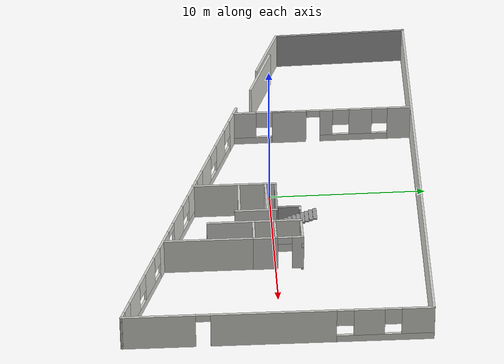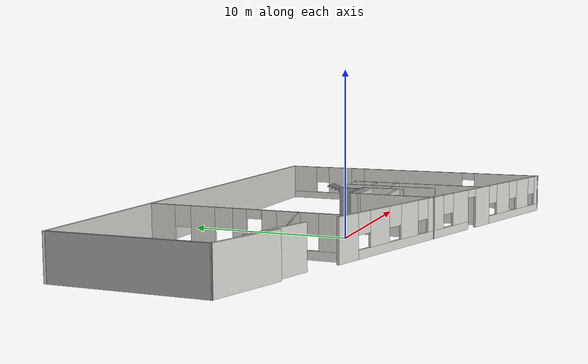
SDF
<?xml version='1.0'?>
<sdf version='1.6'>
  <model name='Erle Office'>
    <link name='Stairs_7'>
      <pose frame=''>0 0 0 0 -0 0</pose>
      <self_collide>0</self_collide>
      <kinematic>0</kinematic>
      <visual name='Stairs_7_Visual_2'>
        <pose frame=''>4.82632 -3.5898 0.231482 0 0 -3.14159</pose>
        <geometry>
          <box>
            <size>1 0.257016 0.092593</size>
          </box>
        </geometry>
        <material>
          <script>
            <uri>file://media/materials/scripts/gazebo.material</uri>
            <name>Gazebo/Grey</name>
          </script>
          <ambient>1 1 1 1</ambient>
          <diffuse>0.7 0.7 0.7 1</diffuse>
          <specular>0.01 0.01 0.01 1</specular>
          <emissive>0 0 0 1</emissive>
        </material>
        <cast_shadows>1</cast_shadows>
        <transparency>0</transparency>
      </visual>
      <visual name='Stairs_7_Visual_0'>
        <pose frame=''>4.82632 -4.10383 0.046296 0 0 -3.14159</pose>
        <geometry>
          <box>
            <size>1 0.257016 0.092593</size>
          </box>
        </geometry>
        <material>
          <script>
            <uri>file://media/materials/scripts/gazebo.material</uri>
            <name>Gazebo/Grey</name>
          </script>
          <ambient>1 1 1 1</ambient>
          <diffuse>0.7 0.7 0.7 1</diffuse>
          <specular>0.01 0.01 0.01 1</specular>
          <emissive>0 0 0 1</emissive>
        </material>
        <cast_shadows>1</cast_shadows>
        <transparency>0</transparency>
      </visual>
      <visual name='Stairs_7_Visual_1'>
        <pose frame=''>4.82632 -3.84681 0.138889 0 0 -3.14159</pose>
        <geometry>
          <box>
            <size>1 0.257016 0.092593</size>
          </box>
        </geometry>
        <material>
          <script>
            <uri>file://media/materials/scripts/gazebo.material</uri>
            <name>Gazebo/Grey</name>
          </script>
          <ambient>1 1 1 1</ambient>
          <diffuse>0.7 0.7 0.7 1</diffuse>
          <specular>0.01 0.01 0.01 1</specular>
          <emissive>0 0 0 1</emissive>
        </material>
        <cast_shadows>1</cast_shadows>
        <transparency>0</transparency>
      </visual>
      <visual name='Stairs_7_Visual_3'>
        <pose frame=''>4.82632 -3.33278 0.324074 0 0 -3.14159</pose>
        <geometry>
          <box>
            <size>1 0.257016 0.092593</size>
          </box>
        </geometry>
        <material>
          <script>
            <uri>file://media/materials/scripts/gazebo.material</uri>
            <name>Gazebo/Grey</name>
          </script>
          <ambient>1 1 1 1</ambient>
          <diffuse>0.7 0.7 0.7 1</diffuse>
          <specular>0.01 0.01 0.01 1</specular>
          <emissive>0 0 0 1</emissive>
        </material>
        <cast_shadows>1</cast_shadows>
        <transparency>0</transparency>
      </visual>
      <visual name='Stairs_7_Visual_4'>
        <pose frame=''>4.82632 -3.07577 0.416667 0 0 -3.14159</pose>
        <geometry>
          <box>
            <size>1 0.257016 0.092593</size>
          </box>
        </geometry>
        <material>
          <script>
            <uri>file://media/materials/scripts/gazebo.material</uri>
            <name>Gazebo/Grey</name>
          </script>
          <ambient>1 1 1 1</ambient>
          <diffuse>0.7 0.7 0.7 1</diffuse>
          <specular>0.01 0.01 0.01 1</specular>
          <emissive>0 0 0 1</emissive>
        </material>
        <cast_shadows>1</cast_shadows>
        <transparency>0</transparency>
      </visual>
      <visual name='Stairs_7_Visual_5'>
        <pose frame=''>4.82632 -2.81875 0.509259 0 0 -3.14159</pose>
        <geometry>
          <box>
            <size>1 0.257016 0.092593</size>
          </box>
        </geometry>
        <material>
          <script>
            <uri>file://media/materials/scripts/gazebo.material</uri>
            <name>Gazebo/Grey</name>
          </script>
          <ambient>1 1 1 1</ambient>
          <diffuse>0.7 0.7 0.7 1</diffuse>
          <specular>0.01 0.01 0.01 1</specular>
          <emissive>0 0 0 1</emissive>
        </material>
        <cast_shadows>1</cast_shadows>
        <transparency>0</transparency>
      </visual>
      <visual name='Stairs_7_Visual_6'>
        <pose frame=''>4.82632 -2.56174 0.601852 0 0 -3.14159</pose>
        <geometry>
          <box>
            <size>1 0.257016 0.092593</size>
          </box>
        </geometry>
        <material>
          <script>
            <uri>file://media/materials/scripts/gazebo.material</uri>
            <name>Gazebo/Grey</name>
          </script>
          <ambient>1 1 1 1</ambient>
          <diffuse>0.7 0.7 0.7 1</diffuse>
          <specular>0.01 0.01 0.01 1</specular>
          <emissive>0 0 0 1</emissive>
        </material>
        <cast_shadows>1</cast_shadows>
        <transparency>0</transparency>
      </visual>
      <visual name='Stairs_7_Visual_7'>
        <pose frame=''>4.82632 -2.30472 0.694444 0 0 -3.14159</pose>
        <geometry>
          <box>
            <size>1 0.257016 0.092593</size>
          </box>
        </geometry>
        <material>
          <script>
            <uri>file://media/materials/scripts/gazebo.material</uri>
            <name>Gazebo/Grey</name>
          </script>
          <ambient>1 1 1 1</ambient>
          <diffuse>0.7 0.7 0.7 1</diffuse>
          <specular>0.01 0.01 0.01 1</specular>
          <emissive>0 0 0 1</emissive>
        </material>
        <cast_shadows>1</cast_shadows>
        <transparency>0</transparency>
      </visual>
      <visual name='Stairs_7_Visual_8'>
        <pose frame=''>4.82632 -2.04771 0.787037 0 0 -3.14159</pose>
        <geometry>
          <box>
            <size>1 0.257016 0.092593</size>
          </box>
        </geometry>
        <material>
          <script>
            <uri>file://media/materials/scripts/gazebo.material</uri>
            <name>Gazebo/Grey</name>
          </script>
          <ambient>1 1 1 1</ambient>
          <diffuse>0.7 0.7 0.7 1</diffuse>
          <specular>0.01 0.01 0.01 1</specular>
          <emissive>0 0 0 1</emissive>
        </material>
        <cast_shadows>1</cast_shadows>
        <transparency>0</transparency>
      </visual>
      <visual name='Stairs_7_Visual_9'>
        <pose frame=''>4.82632 -1.79069 0.87963 0 0 -3.14159</pose>
        <geometry>
          <box>
            <size>1 0.257016 0.092593</size>
          </box>
        </geometry>
        <material>
          <script>
            <uri>file://media/materials/scripts/gazebo.material</uri>
            <name>Gazebo/Grey</name>
          </script>
          <ambient>1 1 1 1</ambient>
          <diffuse>0.7 0.7 0.7 1</diffuse>
          <specular>0.01 0.01 0.01 1</specular>
          <emissive>0 0 0 1</emissive>
        </material>
        <cast_shadows>1</cast_shadows>
        <transparency>0</transparency>
      </visual>
      <visual name='Stairs_7_Visual_10'>
        <pose frame=''>4.82632 -1.53367 0.972222 0 0 -3.14159</pose>
        <geometry>
          <box>
            <size>1 0.257016 0.092593</size>
          </box>
        </geometry>
        <material>
          <script>
            <uri>file://media/materials/scripts/gazebo.material</uri>
            <name>Gazebo/Grey</name>
          </script>
          <ambient>1 1 1 1</ambient>
          <diffuse>0.7 0.7 0.7 1</diffuse>
          <specular>0.01 0.01 0.01 1</specular>
          <emissive>0 0 0 1</emissive>
        </material>
        <cast_shadows>1</cast_shadows>
        <transparency>0</transparency>
      </visual>
      <visual name='Stairs_7_Visual_11'>
        <pose frame=''>4.82632 -1.27666 1.06482 0 0 -3.14159</pose>
        <geometry>
          <box>
            <size>1 0.257016 0.092593</size>
          </box>
        </geometry>
        <material>
          <script>
            <uri>file://media/materials/scripts/gazebo.material</uri>
            <name>Gazebo/Grey</name>
          </script>
          <ambient>1 1 1 1</ambient>
          <diffuse>0.7 0.7 0.7 1</diffuse>
          <specular>0.01 0.01 0.01 1</specular>
          <emissive>0 0 0 1</emissive>
        </material>
        <cast_shadows>1</cast_shadows>
        <transparency>0</transparency>
      </visual>
      <visual name='Stairs_7_Visual_12'>
        <pose frame=''>4.82632 -1.01964 1.15741 0 0 -3.14159</pose>
        <geometry>
          <box>
            <size>1 0.257016 0.092593</size>
          </box>
        </geometry>
        <material>
          <script>
            <uri>file://media/materials/scripts/gazebo.material</uri>
            <name>Gazebo/Grey</name>
          </script>
          <ambient>1 1 1 1</ambient>
          <diffuse>0.7 0.7 0.7 1</diffuse>
          <specular>0.01 0.01 0.01 1</specular>
          <emissive>0 0 0 1</emissive>
        </material>
        <cast_shadows>1</cast_shadows>
        <transparency>0</transparency>
      </visual>
      <visual name='Stairs_7_Visual_13'>
        <pose frame=''>4.82632 -0.762627 1.25 0 0 -3.14159</pose>
        <geometry>
          <box>
            <size>1 0.257016 0.092593</size>
          </box>
        </geometry>
        <material>
          <script>
            <uri>file://media/materials/scripts/gazebo.material</uri>
            <name>Gazebo/Grey</name>
          </script>
          <ambient>1 1 1 1</ambient>
          <diffuse>0.7 0.7 0.7 1</diffuse>
          <specular>0.01 0.01 0.01 1</specular>
          <emissive>0 0 0 1</emissive>
        </material>
        <cast_shadows>1</cast_shadows>
        <transparency>0</transparency>
      </visual>
      <visual name='Stairs_7_Visual_14'>
        <pose frame=''>4.82632 -0.505611 1.34259 0 0 -3.14159</pose>
        <geometry>
          <box>
            <size>1 0.257016 0.092593</size>
          </box>
        </geometry>
        <material>
          <script>
            <uri>file://media/materials/scripts/gazebo.material</uri>
            <name>Gazebo/Grey</name>
          </script>
          <ambient>1 1 1 1</ambient>
          <diffuse>0.7 0.7 0.7 1</diffuse>
          <specular>0.01 0.01 0.01 1</specular>
          <emissive>0 0 0 1</emissive>
        </material>
        <cast_shadows>1</cast_shadows>
        <transparency>0</transparency>
      </visual>
      <visual name='Stairs_7_Visual_15'>
        <pose frame=''>4.82632 -0.248596 1.43518 0 0 -3.14159</pose>
        <geometry>
          <box>
            <size>1 0.257016 0.092593</size>
          </box>
        </geometry>
        <material>
          <script>
            <uri>file://media/materials/scripts/gazebo.material</uri>
            <name>Gazebo/Grey</name>
          </script>
          <ambient>1 1 1 1</ambient>
          <diffuse>0.7 0.7 0.7 1</diffuse>
          <specular>0.01 0.01 0.01 1</specular>
          <emissive>0 0 0 1</emissive>
        </material>
        <cast_shadows>1</cast_shadows>
        <transparency>0</transparency>
      </visual>
      <visual name='Stairs_7_Visual_16'>
        <pose frame=''>4.82632 0.00842 1.52778 0 0 -3.14159</pose>
        <geometry>
          <box>
            <size>1 0.257016 0.092593</size>
          </box>
        </geometry>
        <material>
          <script>
            <uri>file://media/materials/scripts/gazebo.material</uri>
            <name>Gazebo/Grey</name>
          </script>
          <ambient>1 1 1 1</ambient>
          <diffuse>0.7 0.7 0.7 1</diffuse>
          <specular>0.01 0.01 0.01 1</specular>
          <emissive>0 0 0 1</emissive>
        </material>
        <cast_shadows>1</cast_shadows>
        <transparency>0</transparency>
      </visual>
      <visual name='Stairs_7_Visual_17'>
        <pose frame=''>4.82632 0.265435 1.62037 0 0 -3.14159</pose>
        <geometry>
          <box>
            <size>1 0.257016 0.092593</size>
          </box>
        </geometry>
        <material>
          <script>
            <uri>file://media/materials/scripts/gazebo.material</uri>
            <name>Gazebo/Grey</name>
          </script>
          <ambient>1 1 1 1</ambient>
          <diffuse>0.7 0.7 0.7 1</diffuse>
          <specular>0.01 0.01 0.01 1</specular>
          <emissive>0 0 0 1</emissive>
        </material>
        <cast_shadows>1</cast_shadows>
        <transparency>0</transparency>
      </visual>
      <visual name='Stairs_7_Visual_18'>
        <pose frame=''>4.82632 0.522451 1.71296 0 0 -3.14159</pose>
        <geometry>
          <box>
            <size>1 0.257016 0.092593</size>
          </box>
        </geometry>
        <material>
          <script>
            <uri>file://media/materials/scripts/gazebo.material</uri>
            <name>Gazebo/Grey</name>
          </script>
          <ambient>1 1 1 1</ambient>
          <diffuse>0.7 0.7 0.7 1</diffuse>
          <specular>0.01 0.01 0.01 1</specular>
          <emissive>0 0 0 1</emissive>
        </material>
        <cast_shadows>1</cast_shadows>
        <transparency>0</transparency>
      </visual>
      <visual name='Stairs_7_Visual_19'>
        <pose frame=''>4.82632 0.779467 1.80556 0 0 -3.14159</pose>
        <geometry>
          <box>
            <size>1 0.257016 0.092593</size>
          </box>
        </geometry>
        <material>
          <script>
            <uri>file://media/materials/scripts/gazebo.material</uri>
            <name>Gazebo/Grey</name>
          </script>
          <ambient>1 1 1 1</ambient>
          <diffuse>0.7 0.7 0.7 1</diffuse>
          <specular>0.01 0.01 0.01 1</specular>
          <emissive>0 0 0 1</emissive>
        </material>
        <cast_shadows>1</cast_shadows>
        <transparency>0</transparency>
      </visual>
      <visual name='Stairs_7_Visual_20'>
        <pose frame=''>4.82632 1.03648 1.89815 0 0 -3.14159</pose>
        <geometry>
          <box>
            <size>1 0.257016 0.092593</size>
          </box>
        </geometry>
        <material>
          <script>
            <uri>file://media/materials/scripts/gazebo.material</uri>
            <name>Gazebo/Grey</name>
          </script>
          <ambient>1 1 1 1</ambient>
          <diffuse>0.7 0.7 0.7 1</diffuse>
          <specular>0.01 0.01 0.01 1</specular>
          <emissive>0 0 0 1</emissive>
        </material>
        <cast_shadows>1</cast_shadows>
        <transparency>0</transparency>
      </visual>
      <visual name='Stairs_7_Visual_21'>
        <pose frame=''>4.82632 1.2935 1.99074 0 0 -3.14159</pose>
        <geometry>
          <box>
            <size>1 0.257016 0.092593</size>
          </box>
        </geometry>
        <material>
          <script>
            <uri>file://media/materials/scripts/gazebo.material</uri>
            <name>Gazebo/Grey</name>
          </script>
          <ambient>1 1 1 1</ambient>
          <diffuse>0.7 0.7 0.7 1</diffuse>
          <specular>0.01 0.01 0.01 1</specular>
          <emissive>0 0 0 1</emissive>
        </material>
        <cast_shadows>1</cast_shadows>
        <transparency>0</transparency>
      </visual>
      <visual name='Stairs_7_Visual_22'>
        <pose frame=''>4.82632 1.55051 2.08333 0 0 -3.14159</pose>
        <geometry>
          <box>
            <size>1 0.257016 0.092593</size>
          </box>
        </geometry>
        <material>
          <script>
            <uri>file://media/materials/scripts/gazebo.material</uri>
            <name>Gazebo/Grey</name>
          </script>
          <ambient>1 1 1 1</ambient>
          <diffuse>0.7 0.7 0.7 1</diffuse>
          <specular>0.01 0.01 0.01 1</specular>
          <emissive>0 0 0 1</emissive>
        </material>
        <cast_shadows>1</cast_shadows>
        <transparency>0</transparency>
      </visual>
      <visual name='Stairs_7_Visual_23'>
        <pose frame=''>4.82632 1.80753 2.17593 0 0 -3.14159</pose>
        <geometry>
          <box>
            <size>1 0.257016 0.092593</size>
          </box>
        </geometry>
        <material>
          <script>
            <uri>file://media/materials/scripts/gazebo.material</uri>
            <name>Gazebo/Grey</name>
          </script>
          <ambient>1 1 1 1</ambient>
          <diffuse>0.7 0.7 0.7 1</diffuse>
          <specular>0.01 0.01 0.01 1</specular>
          <emissive>0 0 0 1</emissive>
        </material>
        <cast_shadows>1</cast_shadows>
        <transparency>0</transparency>
      </visual>
      <visual name='Stairs_7_Visual_24'>
        <pose frame=''>4.82632 2.06454 2.26852 0 0 -3.14159</pose>
        <geometry>
          <box>
            <size>1 0.257016 0.092593</size>
          </box>
        </geometry>
        <material>
          <script>
            <uri>file://media/materials/scripts/gazebo.material</uri>
            <name>Gazebo/Grey</name>
          </script>
          <ambient>1 1 1 1</ambient>
          <diffuse>0.7 0.7 0.7 1</diffuse>
          <specular>0.01 0.01 0.01 1</specular>
          <emissive>0 0 0 1</emissive>
        </material>
        <cast_shadows>1</cast_shadows>
        <transparency>0</transparency>
      </visual>
      <visual name='Stairs_7_Visual_25'>
        <pose frame=''>4.82632 2.32156 2.36111 0 0 -3.14159</pose>
        <geometry>
          <box>
            <size>1 0.257016 0.092593</size>
          </box>
        </geometry>
        <material>
          <script>
            <uri>file://media/materials/scripts/gazebo.material</uri>
            <name>Gazebo/Grey</name>
          </script>
          <ambient>1 1 1 1</ambient>
          <diffuse>0.7 0.7 0.7 1</diffuse>
          <specular>0.01 0.01 0.01 1</specular>
          <emissive>0 0 0 1</emissive>
        </material>
        <cast_shadows>1</cast_shadows>
        <transparency>0</transparency>
      </visual>
      <visual name='Stairs_7_Visual_26'>
        <pose frame=''>4.82632 2.57858 2.4537 0 0 -3.14159</pose>
        <geometry>
          <box>
            <size>1 0.257016 0.092593</size>
          </box>
        </geometry>
        <material>
          <script>
            <uri>file://media/materials/scripts/gazebo.material</uri>
            <name>Gazebo/Grey</name>
          </script>
          <ambient>1 1 1 1</ambient>
          <diffuse>0.7 0.7 0.7 1</diffuse>
          <specular>0.01 0.01 0.01 1</specular>
          <emissive>0 0 0 1</emissive>
        </material>
        <cast_shadows>1</cast_shadows>
        <transparency>0</transparency>
      </visual>
      <collision name='Stairs_7_Collision_0'>
        <laser_retro>0</laser_retro>
        <max_contacts>10</max_contacts>
        <pose frame=''>4.82632 -4.10383 0.046296 0 0 -3.14159</pose>
        <geometry>
          <box>
            <size>1 0.257016 0.092593</size>
          </box>
        </geometry>
        <surface>
          <friction>
            <ode>
              <mu>1</mu>
              <mu2>1</mu2>
              <fdir1>0 0 0</fdir1>
              <slip1>0</slip1>
              <slip2>0</slip2>
            </ode>
            <torsional>
              <coefficient>1</coefficient>
              <patch_radius>0</patch_radius>
              <surface_radius>0</surface_radius>
              <use_patch_radius>1</use_patch_radius>
              <ode>
                <slip>0</slip>
              </ode>
            </torsional>
          </friction>
          <bounce>
            <restitution_coefficient>0</restitution_coefficient>
            <threshold>1e+06</threshold>
          </bounce>
          <contact>
            <collide_without_contact>0</collide_without_contact>
            <collide_without_contact_bitmask>1</collide_without_contact_bitmask>
            <collide_bitmask>1</collide_bitmask>
            <ode>
              <soft_cfm>0</soft_cfm>
              <soft_erp>0.2</soft_erp>
              <kp>1e+13</kp>
              <kd>1</kd>
              <max_vel>0.01</max_vel>
              <min_depth>0</min_depth>
            </ode>
            <bullet>
              <split_impulse>1</split_impulse>
              <split_impulse_penetration_threshold>-0.01</split_impulse_penetration_threshold>
              <soft_cfm>0</soft_cfm>
              <soft_erp>0.2</soft_erp>
              <kp>1e+13</kp>
              <kd>1</kd>
            </bullet>
          </contact>
        </surface>
      </collision>
      <collision name='Stairs_7_Collision_1'>
        <laser_retro>0</laser_retro>
        <max_contacts>10</max_contacts>
        <pose frame=''>4.82632 -3.84681 0.138889 0 0 -3.14159</pose>
        <geometry>
          <box>
            <size>1 0.257016 0.092593</size>
          </box>
        </geometry>
        <surface>
          <friction>
            <ode>
              <mu>1</mu>
              <mu2>1</mu2>
              <fdir1>0 0 0</fdir1>
              <slip1>0</slip1>
              <slip2>0</slip2>
            </ode>
            <torsional>
              <coefficient>1</coefficient>
              <patch_radius>0</patch_radius>
              <surface_radius>0</surface_radius>
              <use_patch_radius>1</use_patch_radius>
              <ode>
                <slip>0</slip>
              </ode>
            </torsional>
          </friction>
          <bounce>
            <restitution_coefficient>0</restitution_coefficient>
            <threshold>1e+06</threshold>
          </bounce>
          <contact>
            <collide_without_contact>0</collide_without_contact>
            <collide_without_contact_bitmask>1</collide_without_contact_bitmask>
            <collide_bitmask>1</collide_bitmask>
            <ode>
              <soft_cfm>0</soft_cfm>
              <soft_erp>0.2</soft_erp>
              <kp>1e+13</kp>
              <kd>1</kd>
              <max_vel>0.01</max_vel>
              <min_depth>0</min_depth>
            </ode>
            <bullet>
              <split_impulse>1</split_impulse>
              <split_impulse_penetration_threshold>-0.01</split_impulse_penetration_threshold>
              <soft_cfm>0</soft_cfm>
              <soft_erp>0.2</soft_erp>
              <kp>1e+13</kp>
              <kd>1</kd>
            </bullet>
          </contact>
        </surface>
      </collision>
      <collision name='Stairs_7_Collision_3'>
        <laser_retro>0</laser_retro>
        <max_contacts>10</max_contacts>
        <pose frame=''>4.82632 -3.33278 0.324074 0 0 -3.14159</pose>
        <geometry>
          <box>
            <size>1 0.257016 0.092593</size>
          </box>
        </geometry>
        <surface>
          <friction>
            <ode>
              <mu>1</mu>
              <mu2>1</mu2>
              <fdir1>0 0 0</fdir1>
              <slip1>0</slip1>
              <slip2>0</slip2>
            </ode>
            <torsional>
              <coefficient>1</coefficient>
              <patch_radius>0</patch_radius>
              <surface_radius>0</surface_radius>
              <use_patch_radius>1</use_patch_radius>
              <ode>
                <slip>0</slip>
              </ode>
            </torsional>
          </friction>
          <bounce>
            <restitution_coefficient>0</restitution_coefficient>
            <threshold>1e+06</threshold>
          </bounce>
          <contact>
            <collide_without_contact>0</collide_without_contact>
            <collide_without_contact_bitmask>1</collide_without_contact_bitmask>
            <collide_bitmask>1</collide_bitmask>
            <ode>
              <soft_cfm>0</soft_cfm>
              <soft_erp>0.2</soft_erp>
              <kp>1e+13</kp>
              <kd>1</kd>
              <max_vel>0.01</max_vel>
              <min_depth>0</min_depth>
            </ode>
            <bullet>
              <split_impulse>1</split_impulse>
              <split_impulse_penetration_threshold>-0.01</split_impulse_penetration_threshold>
              <soft_cfm>0</soft_cfm>
              <soft_erp>0.2</soft_erp>
              <kp>1e+13</kp>
              <kd>1</kd>
            </bullet>
          </contact>
        </surface>
      </collision>
      <collision name='Stairs_7_Collision_2'>
        <laser_retro>0</laser_retro>
        <max_contacts>10</max_contacts>
        <pose frame=''>4.82632 -3.5898 0.231482 0 0 -3.14159</pose>
        <geometry>
          <box>
            <size>1 0.257016 0.092593</size>
          </box>
        </geometry>
        <surface>
          <friction>
            <ode>
              <mu>1</mu>
              <mu2>1</mu2>
              <fdir1>0 0 0</fdir1>
              <slip1>0</slip1>
              <slip2>0</slip2>
            </ode>
            <torsional>
              <coefficient>1</coefficient>
              <patch_radius>0</patch_radius>
              <surface_radius>0</surface_radius>
              <use_patch_radius>1</use_patch_radius>
              <ode>
                <slip>0</slip>
              </ode>
            </torsional>
          </friction>
          <bounce>
            <restitution_coefficient>0</restitution_coefficient>
            <threshold>1e+06</threshold>
          </bounce>
          <contact>
            <collide_without_contact>0</collide_without_contact>
            <collide_without_contact_bitmask>1</collide_without_contact_bitmask>
            <collide_bitmask>1</collide_bitmask>
            <ode>
              <soft_cfm>0</soft_cfm>
              <soft_erp>0.2</soft_erp>
              <kp>1e+13</kp>
              <kd>1</kd>
              <max_vel>0.01</max_vel>
              <min_depth>0</min_depth>
            </ode>
            <bullet>
              <split_impulse>1</split_impulse>
              <split_impulse_penetration_threshold>-0.01</split_impulse_penetration_threshold>
              <soft_cfm>0</soft_cfm>
              <soft_erp>0.2</soft_erp>
              <kp>1e+13</kp>
              <kd>1</kd>
            </bullet>
          </contact>
        </surface>
      </collision>
      <collision name='Stairs_7_Collision_4'>
        <laser_retro>0</laser_retro>
        <max_contacts>10</max_contacts>
        <pose frame=''>4.82632 -3.07577 0.416667 0 0 -3.14159</pose>
        <geometry>
          <box>
            <size>1 0.257016 0.092593</size>
          </box>
        </geometry>
        <surface>
          <friction>
            <ode>
              <mu>1</mu>
              <mu2>1</mu2>
              <fdir1>0 0 0</fdir1>
              <slip1>0</slip1>
              <slip2>0</slip2>
            </ode>
            <torsional>
              <coefficient>1</coefficient>
              <patch_radius>0</patch_radius>
              <surface_radius>0</surface_radius>
              <use_patch_radius>1</use_patch_radius>
              <ode>
                <slip>0</slip>
              </ode>
            </torsional>
          </friction>
          <bounce>
            <restitution_coefficient>0</restitution_coefficient>
            <threshold>1e+06</threshold>
          </bounce>
          <contact>
            <collide_without_contact>0</collide_without_contact>
            <collide_without_contact_bitmask>1</collide_without_contact_bitmask>
            <collide_bitmask>1</collide_bitmask>
            <ode>
              <soft_cfm>0</soft_cfm>
              <soft_erp>0.2</soft_erp>
              <kp>1e+13</kp>
              <kd>1</kd>
              <max_vel>0.01</max_vel>
              <min_depth>0</min_depth>
            </ode>
            <bullet>
              <split_impulse>1</split_impulse>
              <split_impulse_penetration_threshold>-0.01</split_impulse_penetration_threshold>
              <soft_cfm>0</soft_cfm>
              <soft_erp>0.2</soft_erp>
              <kp>1e+13</kp>
              <kd>1</kd>
            </bullet>
          </contact>
        </surface>
      </collision>
      <collision name='Stairs_7_Collision_5'>
        <laser_retro>0</laser_retro>
        <max_contacts>10</max_contacts>
        <pose frame=''>4.82632 -2.81875 0.509259 0 0 -3.14159</pose>
        <geometry>
          <box>
            <size>1 0.257016 0.092593</size>
          </box>
        </geometry>
        <surface>
          <friction>
            <ode>
              <mu>1</mu>
              <mu2>1</mu2>
              <fdir1>0 0 0</fdir1>
              <slip1>0</slip1>
              <slip2>0</slip2>
            </ode>
            <torsional>
              <coefficient>1</coefficient>
              <patch_radius>0</patch_radius>
              <surface_radius>0</surface_radius>
              <use_patch_radius>1</use_patch_radius>
              <ode>
                <slip>0</slip>
              </ode>
            </torsional>
          </friction>
          <bounce>
            <restitution_coefficient>0</restitution_coefficient>
            <threshold>1e+06</threshold>
          </bounce>
          <contact>
            <collide_without_contact>0</collide_without_contact>
            <collide_without_contact_bitmask>1</collide_without_contact_bitmask>
            <collide_bitmask>1</collide_bitmask>
            <ode>
              <soft_cfm>0</soft_cfm>
              <soft_erp>0.2</soft_erp>
              <kp>1e+13</kp>
              <kd>1</kd>
              <max_vel>0.01</max_vel>
              <min_depth>0</min_depth>
            </ode>
            <bullet>
              <split_impulse>1</split_impulse>
              <split_impulse_penetration_threshold>-0.01</split_impulse_penetration_threshold>
              <soft_cfm>0</soft_cfm>
              <soft_erp>0.2</soft_erp>
              <kp>1e+13</kp>
              <kd>1</kd>
            </bullet>
          </contact>
        </surface>
      </collision>
      <collision name='Stairs_7_Collision_6'>
        <laser_retro>0</laser_retro>
        <max_contacts>10</max_contacts>
        <pose frame=''>4.82632 -2.56174 0.601852 0 0 -3.14159</pose>
        <geometry>
          <box>
            <size>1 0.257016 0.092593</size>
          </box>
        </geometry>
        <surface>
          <friction>
            <ode>
              <mu>1</mu>
              <mu2>1</mu2>
              <fdir1>0 0 0</fdir1>
              <slip1>0</slip1>
              <slip2>0</slip2>
            </ode>
            <torsional>
              <coefficient>1</coefficient>
              <patch_radius>0</patch_radius>
              <surface_radius>0</surface_radius>
              <use_patch_radius>1</use_patch_radius>
              <ode>
                <slip>0</slip>
              </ode>
            </torsional>
          </friction>
          <bounce>
            <restitution_coefficient>0</restitution_coefficient>
            <threshold>1e+06</threshold>
          </bounce>
          <contact>
            <collide_without_contact>0</collide_without_contact>
            <collide_without_contact_bitmask>1</collide_without_contact_bitmask>
            <collide_bitmask>1</collide_bitmask>
            <ode>
              <soft_cfm>0</soft_cfm>
              <soft_erp>0.2</soft_erp>
              <kp>1e+13</kp>
              <kd>1</kd>
              <max_vel>0.01</max_vel>
              <min_depth>0</min_depth>
            </ode>
            <bullet>
              <split_impulse>1</split_impulse>
              <split_impulse_penetration_threshold>-0.01</split_impulse_penetration_threshold>
              <soft_cfm>0</soft_cfm>
              <soft_erp>0.2</soft_erp>
              <kp>1e+13</kp>
              <kd>1</kd>
            </bullet>
          </contact>
        </surface>
      </collision>
      <collision name='Stairs_7_Collision_9'>
        <laser_retro>0</laser_retro>
        <max_contacts>10</max_contacts>
        <pose frame=''>4.82632 -1.79069 0.87963 0 0 -3.14159</pose>
        <geometry>
          <box>
            <size>1 0.257016 0.092593</size>
          </box>
        </geometry>
        <surface>
          <friction>
            <ode>
              <mu>1</mu>
              <mu2>1</mu2>
              <fdir1>0 0 0</fdir1>
              <slip1>0</slip1>
              <slip2>0</slip2>
            </ode>
            <torsional>
              <coefficient>1</coefficient>
              <patch_radius>0</patch_radius>
              <surface_radius>0</surface_radius>
              <use_patch_radius>1</use_patch_radius>
              <ode>
                <slip>0</slip>
              </ode>
            </torsional>
          </friction>
          <bounce>
            <restitution_coefficient>0</restitution_coefficient>
            <threshold>1e+06</threshold>
          </bounce>
          <contact>
            <collide_without_contact>0</collide_without_contact>
            <collide_without_contact_bitmask>1</collide_without_contact_bitmask>
            <collide_bitmask>1</collide_bitmask>
            <ode>
              <soft_cfm>0</soft_cfm>
              <soft_erp>0.2</soft_erp>
              <kp>1e+13</kp>
              <kd>1</kd>
              <max_vel>0.01</max_vel>
              <min_depth>0</min_depth>
            </ode>
            <bullet>
              <split_impulse>1</split_impulse>
              <split_impulse_penetration_threshold>-0.01</split_impulse_penetration_threshold>
              <soft_cfm>0</soft_cfm>
              <soft_erp>0.2</soft_erp>
              <kp>1e+13</kp>
              <kd>1</kd>
            </bullet>
          </contact>
        </surface>
      </collision>
      <collision name='Stairs_7_Collision_7'>
        <laser_retro>0</laser_retro>
        <max_contacts>10</max_contacts>
        <pose frame=''>4.82632 -2.30472 0.694444 0 0 -3.14159</pose>
        <geometry>
          <box>
            <size>1 0.257016 0.092593</size>
          </box>
        </geometry>
        <surface>
          <friction>
            <ode>
              <mu>1</mu>
              <mu2>1</mu2>
              <fdir1>0 0 0</fdir1>
              <slip1>0</slip1>
              <slip2>0</slip2>
            </ode>
            <torsional>
              <coefficient>1</coefficient>
              <patch_radius>0</patch_radius>
              <surface_radius>0</surface_radius>
              <use_patch_radius>1</use_patch_radius>
              <ode>
                <slip>0</slip>
              </ode>
            </torsional>
          </friction>
          <bounce>
            <restitution_coefficient>0</restitution_coefficient>
            <threshold>1e+06</threshold>
          </bounce>
          <contact>
            <collide_without_contact>0</collide_without_contact>
            <collide_without_contact_bitmask>1</collide_without_contact_bitmask>
            <collide_bitmask>1</collide_bitmask>
            <ode>
              <soft_cfm>0</soft_cfm>
              <soft_erp>0.2</soft_erp>
              <kp>1e+13</kp>
              <kd>1</kd>
              <max_vel>0.01</max_vel>
              <min_depth>0</min_depth>
            </ode>
            <bullet>
              <split_impulse>1</split_impulse>
              <split_impulse_penetration_threshold>-0.01</split_impulse_penetration_threshold>
              <soft_cfm>0</soft_cfm>
              <soft_erp>0.2</soft_erp>
              <kp>1e+13</kp>
              <kd>1</kd>
            </bullet>
          </contact>
        </surface>
      </collision>
      <collision name='Stairs_7_Collision_10'>
        <laser_retro>0</laser_retro>
        <max_contacts>10</max_contacts>
        <pose frame=''>4.82632 -1.53367 0.972222 0 0 -3.14159</pose>
        <geometry>
          <box>
            <size>1 0.257016 0.092593</size>
          </box>
        </geometry>
        <surface>
          <friction>
            <ode>
              <mu>1</mu>
              <mu2>1</mu2>
              <fdir1>0 0 0</fdir1>
              <slip1>0</slip1>
              <slip2>0</slip2>
            </ode>
            <torsional>
              <coefficient>1</coefficient>
              <patch_radius>0</patch_radius>
              <surface_radius>0</surface_radius>
              <use_patch_radius>1</use_patch_radius>
              <ode>
                <slip>0</slip>
              </ode>
            </torsional>
          </friction>
          <bounce>
            <restitution_coefficient>0</restitution_coefficient>
            <threshold>1e+06</threshold>
          </bounce>
          <contact>
            <collide_without_contact>0</collide_without_contact>
            <collide_without_contact_bitmask>1</collide_without_contact_bitmask>
            <collide_bitmask>1</collide_bitmask>
            <ode>
              <soft_cfm>0</soft_cfm>
              <soft_erp>0.2</soft_erp>
              <kp>1e+13</kp>
              <kd>1</kd>
              <max_vel>0.01</max_vel>
              <min_depth>0</min_depth>
            </ode>
            <bullet>
              <split_impulse>1</split_impulse>
              <split_impulse_penetration_threshold>-0.01</split_impulse_penetration_threshold>
              <soft_cfm>0</soft_cfm>
              <soft_erp>0.2</soft_erp>
              <kp>1e+13</kp>
              <kd>1</kd>
            </bullet>
          </contact>
        </surface>
      </collision>
      <collision name='Stairs_7_Collision_8'>
        <laser_retro>0</laser_retro>
        <max_contacts>10</max_contacts>
        <pose frame=''>4.82632 -2.04771 0.787037 0 0 -3.14159</pose>
        <geometry>
          <box>
            <size>1 0.257016 0.092593</size>
          </box>
        </geometry>
        <surface>
          <friction>
            <ode>
              <mu>1</mu>
              <mu2>1</mu2>
              <fdir1>0 0 0</fdir1>
              <slip1>0</slip1>
              <slip2>0</slip2>
            </ode>
            <torsional>
              <coefficient>1</coefficient>
              <patch_radius>0</patch_radius>
              <surface_radius>0</surface_radius>
              <use_patch_radius>1</use_patch_radius>
              <ode>
                <slip>0</slip>
              </ode>
            </torsional>
          </friction>
          <bounce>
            <restitution_coefficient>0</restitution_coefficient>
            <threshold>1e+06</threshold>
          </bounce>
          <contact>
            <collide_without_contact>0</collide_without_contact>
            <collide_without_contact_bitmask>1</collide_without_contact_bitmask>
            <collide_bitmask>1</collide_bitmask>
            <ode>
              <soft_cfm>0</soft_cfm>
              <soft_erp>0.2</soft_erp>
              <kp>1e+13</kp>
              <kd>1</kd>
              <max_vel>0.01</max_vel>
              <min_depth>0</min_depth>
            </ode>
            <bullet>
              <split_impulse>1</split_impulse>
              <split_impulse_penetration_threshold>-0.01</split_impulse_penetration_threshold>
              <soft_cfm>0</soft_cfm>
              <soft_erp>0.2</soft_erp>
              <kp>1e+13</kp>
              <kd>1</kd>
            </bullet>
          </contact>
        </surface>
      </collision>
      <collision name='Stairs_7_Collision_11'>
        <laser_retro>0</laser_retro>
        <max_contacts>10</max_contacts>
        <pose frame=''>4.82632 -1.27666 1.06482 0 0 -3.14159</pose>
        <geometry>
          <box>
            <size>1 0.257016 0.092593</size>
          </box>
        </geometry>
        <surface>
          <friction>
            <ode>
              <mu>1</mu>
              <mu2>1</mu2>
              <fdir1>0 0 0</fdir1>
              <slip1>0</slip1>
              <slip2>0</slip2>
            </ode>
            <torsional>
              <coefficient>1</coefficient>
              <patch_radius>0</patch_radius>
              <surface_radius>0</surface_radius>
              <use_patch_radius>1</use_patch_radius>
              <ode>
                <slip>0</slip>
              </ode>
            </torsional>
          </friction>
          <bounce>
            <restitution_coefficient>0</restitution_coefficient>
            <threshold>1e+06</threshold>
          </bounce>
          <contact>
            <collide_without_contact>0</collide_without_contact>
            <collide_without_contact_bitmask>1</collide_without_contact_bitmask>
            <collide_bitmask>1</collide_bitmask>
            <ode>
              <soft_cfm>0</soft_cfm>
              <soft_erp>0.2</soft_erp>
              <kp>1e+13</kp>
              <kd>1</kd>
              <max_vel>0.01</max_vel>
              <min_depth>0</min_depth>
            </ode>
            <bullet>
              <split_impulse>1</split_impulse>
              <split_impulse_penetration_threshold>-0.01</split_impulse_penetration_threshold>
              <soft_cfm>0</soft_cfm>
              <soft_erp>0.2</soft_erp>
              <kp>1e+13</kp>
              <kd>1</kd>
            </bullet>
          </contact>
        </surface>
      </collision>
      <collision name='Stairs_7_Collision_12'>
        <laser_retro>0</laser_retro>
        <max_contacts>10</max_contacts>
        <pose frame=''>4.82632 -1.01964 1.15741 0 0 -3.14159</pose>
        <geometry>
          <box>
            <size>1 0.257016 0.092593</size>
          </box>
        </geometry>
        <surface>
          <friction>
            <ode>
              <mu>1</mu>
              <mu2>1</mu2>
              <fdir1>0 0 0</fdir1>
              <slip1>0</slip1>
              <slip2>0</slip2>
            </ode>
            <torsional>
              <coefficient>1</coefficient>
              <patch_radius>0</patch_radius>
              <surface_radius>0</surface_radius>
              <use_patch_radius>1</use_patch_radius>
              <ode>
                <slip>0</slip>
              </ode>
            </torsional>
          </friction>
          <bounce>
            <restitution_coefficient>0</restitution_coefficient>
            <threshold>1e+06</threshold>
          </bounce>
          <contact>
            <collide_without_contact>0</collide_without_contact>
            <collide_without_contact_bitmask>1</collide_without_contact_bitmask>
            <collide_bitmask>1</collide_bitmask>
            <ode>
              <soft_cfm>0</soft_cfm>
              <soft_erp>0.2</soft_erp>
              <kp>1e+13</kp>
              <kd>1</kd>
              <max_vel>0.01</max_vel>
              <min_depth>0</min_depth>
            </ode>
            <bullet>
              <split_impulse>1</split_impulse>
              <split_impulse_penetration_threshold>-0.01</split_impulse_penetration_threshold>
              <soft_cfm>0</soft_cfm>
              <soft_erp>0.2</soft_erp>
              <kp>1e+13</kp>
              <kd>1</kd>
            </bullet>
          </contact>
        </surface>
      </collision>
      <collision name='Stairs_7_Collision_13'>
        <laser_retro>0</laser_retro>
        <max_contacts>10</max_contacts>
        <pose frame=''>4.82632 -0.762627 1.25 0 0 -3.14159</pose>
        <geometry>
          <box>
            <size>1 0.257016 0.092593</size>
          </box>
        </geometry>
        <surface>
          <friction>
            <ode>
              <mu>1</mu>
              <mu2>1</mu2>
              <fdir1>0 0 0</fdir1>
              <slip1>0</slip1>
              <slip2>0</slip2>
            </ode>
            <torsional>
              <coefficient>1</coefficient>
              <patch_radius>0</patch_radius>
              <surface_radius>0</surface_radius>
              <use_patch_radius>1</use_patch_radius>
              <ode>
                <slip>0</slip>
              </ode>
            </torsional>
          </friction>
          <bounce>
            <restitution_coefficient>0</restitution_coefficient>
            <threshold>1e+06</threshold>
          </bounce>
          <contact>
            <collide_without_contact>0</collide_without_contact>
            <collide_without_contact_bitmask>1</collide_without_contact_bitmask>
            <collide_bitmask>1</collide_bitmask>
            <ode>
              <soft_cfm>0</soft_cfm>
              <soft_erp>0.2</soft_erp>
              <kp>1e+13</kp>
              <kd>1</kd>
              <max_vel>0.01</max_vel>
              <min_depth>0</min_depth>
            </ode>
            <bullet>
              <split_impulse>1</split_impulse>
              <split_impulse_penetration_threshold>-0.01</split_impulse_penetration_threshold>
              <soft_cfm>0</soft_cfm>
              <soft_erp>0.2</soft_erp>
              <kp>1e+13</kp>
              <kd>1</kd>
            </bullet>
          </contact>
        </surface>
      </collision>
      <collision name='Stairs_7_Collision_16'>
        <laser_retro>0</laser_retro>
        <max_contacts>10</max_contacts>
        <pose frame=''>4.82632 0.00842 1.52778 0 0 -3.14159</pose>
        <geometry>
          <box>
            <size>1 0.257016 0.092593</size>
          </box>
        </geometry>
        <surface>
          <friction>
            <ode>
              <mu>1</mu>
              <mu2>1</mu2>
              <fdir1>0 0 0</fdir1>
              <slip1>0</slip1>
              <slip2>0</slip2>
            </ode>
            <torsional>
              <coefficient>1</coefficient>
              <patch_radius>0</patch_radius>
              <surface_radius>0</surface_radius>
              <use_patch_radius>1</use_patch_radius>
              <ode>
                <slip>0</slip>
              </ode>
            </torsional>
          </friction>
          <bounce>
            <restitution_coefficient>0</restitution_coefficient>
            <threshold>1e+06</threshold>
          </bounce>
          <contact>
            <collide_without_contact>0</collide_without_contact>
            <collide_without_contact_bitmask>1</collide_without_contact_bitmask>
            <collide_bitmask>1</collide_bitmask>
            <ode>
              <soft_cfm>0</soft_cfm>
              <soft_erp>0.2</soft_erp>
              <kp>1e+13</kp>
              <kd>1</kd>
              <max_vel>0.01</max_vel>
              <min_depth>0</min_depth>
            </ode>
            <bullet>
              <split_impulse>1</split_impulse>
              <split_impulse_penetration_threshold>-0.01</split_impulse_penetration_threshold>
              <soft_cfm>0</soft_cfm>
              <soft_erp>0.2</soft_erp>
              <kp>1e+13</kp>
              <kd>1</kd>
            </bullet>
          </contact>
        </surface>
      </collision>
      <collision name='Stairs_7_Collision_14'>
        <laser_retro>0</laser_retro>
        <max_contacts>10</max_contacts>
        <pose frame=''>4.82632 -0.505611 1.34259 0 0 -3.14159</pose>
        <geometry>
          <box>
            <size>1 0.257016 0.092593</size>
          </box>
        </geometry>
        <surface>
          <friction>
            <ode>
              <mu>1</mu>
              <mu2>1</mu2>
              <fdir1>0 0 0</fdir1>
              <slip1>0</slip1>
              <slip2>0</slip2>
            </ode>
            <torsional>
              <coefficient>1</coefficient>
              <patch_radius>0</patch_radius>
              <surface_radius>0</surface_radius>
              <use_patch_radius>1</use_patch_radius>
              <ode>
                <slip>0</slip>
              </ode>
            </torsional>
          </friction>
          <bounce>
            <restitution_coefficient>0</restitution_coefficient>
            <threshold>1e+06</threshold>
          </bounce>
          <contact>
            <collide_without_contact>0</collide_without_contact>
            <collide_without_contact_bitmask>1</collide_without_contact_bitmask>
            <collide_bitmask>1</collide_bitmask>
            <ode>
              <soft_cfm>0</soft_cfm>
              <soft_erp>0.2</soft_erp>
              <kp>1e+13</kp>
              <kd>1</kd>
              <max_vel>0.01</max_vel>
              <min_depth>0</min_depth>
            </ode>
            <bullet>
              <split_impulse>1</split_impulse>
              <split_impulse_penetration_threshold>-0.01</split_impulse_penetration_threshold>
              <soft_cfm>0</soft_cfm>
              <soft_erp>0.2</soft_erp>
              <kp>1e+13</kp>
              <kd>1</kd>
            </bullet>
          </contact>
        </surface>
      </collision>
      <collision name='Stairs_7_Collision_15'>
        <laser_retro>0</laser_retro>
        <max_contacts>10</max_contacts>
        <pose frame=''>4.82632 -0.248596 1.43518 0 0 -3.14159</pose>
        <geometry>
          <box>
            <size>1 0.257016 0.092593</size>
          </box>
        </geometry>
        <surface>
          <friction>
            <ode>
              <mu>1</mu>
              <mu2>1</mu2>
              <fdir1>0 0 0</fdir1>
              <slip1>0</slip1>
              <slip2>0</slip2>
            </ode>
            <torsional>
              <coefficient>1</coefficient>
              <patch_radius>0</patch_radius>
              <surface_radius>0</surface_radius>
              <use_patch_radius>1</use_patch_radius>
              <ode>
                <slip>0</slip>
              </ode>
            </torsional>
          </friction>
          <bounce>
            <restitution_coefficient>0</restitution_coefficient>
            <threshold>1e+06</threshold>
          </bounce>
          <contact>
            <collide_without_contact>0</collide_without_contact>
            <collide_without_contact_bitmask>1</collide_without_contact_bitmask>
            <collide_bitmask>1</collide_bitmask>
            <ode>
              <soft_cfm>0</soft_cfm>
              <soft_erp>0.2</soft_erp>
              <kp>1e+13</kp>
              <kd>1</kd>
              <max_vel>0.01</max_vel>
              <min_depth>0</min_depth>
            </ode>
            <bullet>
              <split_impulse>1</split_impulse>
              <split_impulse_penetration_threshold>-0.01</split_impulse_penetration_threshold>
              <soft_cfm>0</soft_cfm>
              <soft_erp>0.2</soft_erp>
              <kp>1e+13</kp>
              <kd>1</kd>
            </bullet>
          </contact>
        </surface>
      </collision>
      <collision name='Stairs_7_Collision_19'>
        <laser_retro>0</laser_retro>
        <max_contacts>10</max_contacts>
        <pose frame=''>4.82632 0.779467 1.80556 0 0 -3.14159</pose>
        <geometry>
          <box>
            <size>1 0.257016 0.092593</size>
          </box>
        </geometry>
        <surface>
          <friction>
            <ode>
              <mu>1</mu>
              <mu2>1</mu2>
              <fdir1>0 0 0</fdir1>
              <slip1>0</slip1>
              <slip2>0</slip2>
            </ode>
            <torsional>
              <coefficient>1</coefficient>
              <patch_radius>0</patch_radius>
              <surface_radius>0</surface_radius>
              <use_patch_radius>1</use_patch_radius>
              <ode>
                <slip>0</slip>
              </ode>
            </torsional>
          </friction>
          <bounce>
            <restitution_coefficient>0</restitution_coefficient>
            <threshold>1e+06</threshold>
          </bounce>
          <contact>
            <collide_without_contact>0</collide_without_contact>
            <collide_without_contact_bitmask>1</collide_without_contact_bitmask>
            <collide_bitmask>1</collide_bitmask>
            <ode>
              <soft_cfm>0</soft_cfm>
              <soft_erp>0.2</soft_erp>
              <kp>1e+13</kp>
              <kd>1</kd>
              <max_vel>0.01</max_vel>
              <min_depth>0</min_depth>
            </ode>
            <bullet>
              <split_impulse>1</split_impulse>
              <split_impulse_penetration_threshold>-0.01</split_impulse_penetration_threshold>
              <soft_cfm>0</soft_cfm>
              <soft_erp>0.2</soft_erp>
              <kp>1e+13</kp>
              <kd>1</kd>
            </bullet>
          </contact>
        </surface>
      </collision>
      <collision name='Stairs_7_Collision_18'>
        <laser_retro>0</laser_retro>
        <max_contacts>10</max_contacts>
        <pose frame=''>4.82632 0.522451 1.71296 0 0 -3.14159</pose>
        <geometry>
          <box>
            <size>1 0.257016 0.092593</size>
          </box>
        </geometry>
        <surface>
          <friction>
            <ode>
              <mu>1</mu>
              <mu2>1</mu2>
              <fdir1>0 0 0</fdir1>
              <slip1>0</slip1>
              <slip2>0</slip2>
            </ode>
            <torsional>
              <coefficient>1</coefficient>
              <patch_radius>0</patch_radius>
              <surface_radius>0</surface_radius>
              <use_patch_radius>1</use_patch_radius>
              <ode>
                <slip>0</slip>
              </ode>
            </torsional>
          </friction>
          <bounce>
            <restitution_coefficient>0</restitution_coefficient>
            <threshold>1e+06</threshold>
          </bounce>
          <contact>
            <collide_without_contact>0</collide_without_contact>
            <collide_without_contact_bitmask>1</collide_without_contact_bitmask>
            <collide_bitmask>1</collide_bitmask>
            <ode>
              <soft_cfm>0</soft_cfm>
              <soft_erp>0.2</soft_erp>
              <kp>1e+13</kp>
              <kd>1</kd>
              <max_vel>0.01</max_vel>
              <min_depth>0</min_depth>
            </ode>
            <bullet>
              <split_impulse>1</split_impulse>
              <split_impulse_penetration_threshold>-0.01</split_impulse_penetration_threshold>
              <soft_cfm>0</soft_cfm>
              <soft_erp>0.2</soft_erp>
              <kp>1e+13</kp>
              <kd>1</kd>
            </bullet>
          </contact>
        </surface>
      </collision>
      <collision name='Stairs_7_Collision_17'>
        <laser_retro>0</laser_retro>
        <max_contacts>10</max_contacts>
        <pose frame=''>4.82632 0.265435 1.62037 0 0 -3.14159</pose>
        <geometry>
          <box>
            <size>1 0.257016 0.092593</size>
          </box>
        </geometry>
        <surface>
          <friction>
            <ode>
              <mu>1</mu>
              <mu2>1</mu2>
              <fdir1>0 0 0</fdir1>
              <slip1>0</slip1>
              <slip2>0</slip2>
            </ode>
            <torsional>
              <coefficient>1</coefficient>
              <patch_radius>0</patch_radius>
              <surface_radius>0</surface_radius>
              <use_patch_radius>1</use_patch_radius>
              <ode>
                <slip>0</slip>
              </ode>
            </torsional>
          </friction>
          <bounce>
            <restitution_coefficient>0</restitution_coefficient>
            <threshold>1e+06</threshold>
          </bounce>
          <contact>
            <collide_without_contact>0</collide_without_contact>
            <collide_without_contact_bitmask>1</collide_without_contact_bitmask>
            <collide_bitmask>1</collide_bitmask>
            <ode>
              <soft_cfm>0</soft_cfm>
              <soft_erp>0.2</soft_erp>
              <kp>1e+13</kp>
              <kd>1</kd>
              <max_vel>0.01</max_vel>
              <min_depth>0</min_depth>
            </ode>
            <bullet>
              <split_impulse>1</split_impulse>
              <split_impulse_penetration_threshold>-0.01</split_impulse_penetration_threshold>
              <soft_cfm>0</soft_cfm>
              <soft_erp>0.2</soft_erp>
              <kp>1e+13</kp>
              <kd>1</kd>
            </bullet>
          </contact>
        </surface>
      </collision>
      <collision name='Stairs_7_Collision_20'>
        <laser_retro>0</laser_retro>
        <max_contacts>10</max_contacts>
        <pose frame=''>4.82632 1.03648 1.89815 0 0 -3.14159</pose>
        <geometry>
          <box>
            <size>1 0.257016 0.092593</size>
          </box>
        </geometry>
        <surface>
          <friction>
            <ode>
              <mu>1</mu>
              <mu2>1</mu2>
              <fdir1>0 0 0</fdir1>
              <slip1>0</slip1>
              <slip2>0</slip2>
            </ode>
            <torsional>
              <coefficient>1</coefficient>
              <patch_radius>0</patch_radius>
              <surface_radius>0</surface_radius>
              <use_patch_radius>1</use_patch_radius>
              <ode>
                <slip>0</slip>
              </ode>
            </torsional>
          </friction>
          <bounce>
            <restitution_coefficient>0</restitution_coefficient>
            <threshold>1e+06</threshold>
          </bounce>
          <contact>
            <collide_without_contact>0</collide_without_contact>
            <collide_without_contact_bitmask>1</collide_without_contact_bitmask>
            <collide_bitmask>1</collide_bitmask>
            <ode>
              <soft_cfm>0</soft_cfm>
              <soft_erp>0.2</soft_erp>
              <kp>1e+13</kp>
              <kd>1</kd>
              <max_vel>0.01</max_vel>
              <min_depth>0</min_depth>
            </ode>
            <bullet>
              <split_impulse>1</split_impulse>
              <split_impulse_penetration_threshold>-0.01</split_impulse_penetration_threshold>
              <soft_cfm>0</soft_cfm>
              <soft_erp>0.2</soft_erp>
              <kp>1e+13</kp>
              <kd>1</kd>
            </bullet>
          </contact>
        </surface>
      </collision>
      <collision name='Stairs_7_Collision_23'>
        <laser_retro>0</laser_retro>
        <max_contacts>10</max_contacts>
        <pose frame=''>4.82632 1.80753 2.17593 0 0 -3.14159</pose>
        <geometry>
          <box>
            <size>1 0.257016 0.092593</size>
          </box>
        </geometry>
        <surface>
          <friction>
            <ode>
              <mu>1</mu>
              <mu2>1</mu2>
              <fdir1>0 0 0</fdir1>
              <slip1>0</slip1>
              <slip2>0</slip2>
            </ode>
            <torsional>
              <coefficient>1</coefficient>
              <patch_radius>0</patch_radius>
              <surface_radius>0</surface_radius>
              <use_patch_radius>1</use_patch_radius>
              <ode>
                <slip>0</slip>
              </ode>
            </torsional>
          </friction>
          <bounce>
            <restitution_coefficient>0</restitution_coefficient>
            <threshold>1e+06</threshold>
          </bounce>
          <contact>
            <collide_without_contact>0</collide_without_contact>
            <collide_without_contact_bitmask>1</collide_without_contact_bitmask>
            <collide_bitmask>1</collide_bitmask>
            <ode>
              <soft_cfm>0</soft_cfm>
              <soft_erp>0.2</soft_erp>
              <kp>1e+13</kp>
              <kd>1</kd>
              <max_vel>0.01</max_vel>
              <min_depth>0</min_depth>
            </ode>
            <bullet>
              <split_impulse>1</split_impulse>
              <split_impulse_penetration_threshold>-0.01</split_impulse_penetration_threshold>
              <soft_cfm>0</soft_cfm>
              <soft_erp>0.2</soft_erp>
              <kp>1e+13</kp>
              <kd>1</kd>
            </bullet>
          </contact>
        </surface>
      </collision>
      <collision name='Stairs_7_Collision_22'>
        <laser_retro>0</laser_retro>
        <max_contacts>10</max_contacts>
        <pose frame=''>4.82632 1.55051 2.08333 0 0 -3.14159</pose>
        <geometry>
          <box>
            <size>1 0.257016 0.092593</size>
          </box>
        </geometry>
        <surface>
          <friction>
            <ode>
              <mu>1</mu>
              <mu2>1</mu2>
              <fdir1>0 0 0</fdir1>
              <slip1>0</slip1>
              <slip2>0</slip2>
            </ode>
            <torsional>
              <coefficient>1</coefficient>
              <patch_radius>0</patch_radius>
              <surface_radius>0</surface_radius>
              <use_patch_radius>1</use_patch_radius>
              <ode>
                <slip>0</slip>
              </ode>
            </torsional>
          </friction>
          <bounce>
            <restitution_coefficient>0</restitution_coefficient>
            <threshold>1e+06</threshold>
          </bounce>
          <contact>
            <collide_without_contact>0</collide_without_contact>
            <collide_without_contact_bitmask>1</collide_without_contact_bitmask>
            <collide_bitmask>1</collide_bitmask>
            <ode>
              <soft_cfm>0</soft_cfm>
              <soft_erp>0.2</soft_erp>
              <kp>1e+13</kp>
              <kd>1</kd>
              <max_vel>0.01</max_vel>
              <min_depth>0</min_depth>
            </ode>
            <bullet>
              <split_impulse>1</split_impulse>
              <split_impulse_penetration_threshold>-0.01</split_impulse_penetration_threshold>
              <soft_cfm>0</soft_cfm>
              <soft_erp>0.2</soft_erp>
              <kp>1e+13</kp>
              <kd>1</kd>
            </bullet>
          </contact>
        </surface>
      </collision>
      <collision name='Stairs_7_Collision_21'>
        <laser_retro>0</laser_retro>
        <max_contacts>10</max_contacts>
        <pose frame=''>4.82632 1.2935 1.99074 0 0 -3.14159</pose>
        <geometry>
          <box>
            <size>1 0.257016 0.092593</size>
          </box>
        </geometry>
        <surface>
          <friction>
            <ode>
              <mu>1</mu>
              <mu2>1</mu2>
              <fdir1>0 0 0</fdir1>
              <slip1>0</slip1>
              <slip2>0</slip2>
            </ode>
            <torsional>
              <coefficient>1</coefficient>
              <patch_radius>0</patch_radius>
              <surface_radius>0</surface_radius>
              <use_patch_radius>1</use_patch_radius>
              <ode>
                <slip>0</slip>
              </ode>
            </torsional>
          </friction>
          <bounce>
            <restitution_coefficient>0</restitution_coefficient>
            <threshold>1e+06</threshold>
          </bounce>
          <contact>
            <collide_without_contact>0</collide_without_contact>
            <collide_without_contact_bitmask>1</collide_without_contact_bitmask>
            <collide_bitmask>1</collide_bitmask>
            <ode>
              <soft_cfm>0</soft_cfm>
              <soft_erp>0.2</soft_erp>
              <kp>1e+13</kp>
              <kd>1</kd>
              <max_vel>0.01</max_vel>
              <min_depth>0</min_depth>
            </ode>
            <bullet>
              <split_impulse>1</split_impulse>
              <split_impulse_penetration_threshold>-0.01</split_impulse_penetration_threshold>
              <soft_cfm>0</soft_cfm>
              <soft_erp>0.2</soft_erp>
              <kp>1e+13</kp>
              <kd>1</kd>
            </bullet>
          </contact>
        </surface>
      </collision>
      <collision name='Stairs_7_Collision_24'>
        <laser_retro>0</laser_retro>
        <max_contacts>10</max_contacts>
        <pose frame=''>4.82632 2.06454 2.26852 0 0 -3.14159</pose>
        <geometry>
          <box>
            <size>1 0.257016 0.092593</size>
          </box>
        </geometry>
        <surface>
          <friction>
            <ode>
              <mu>1</mu>
              <mu2>1</mu2>
              <fdir1>0 0 0</fdir1>
              <slip1>0</slip1>
              <slip2>0</slip2>
            </ode>
            <torsional>
              <coefficient>1</coefficient>
              <patch_radius>0</patch_radius>
              <surface_radius>0</surface_radius>
              <use_patch_radius>1</use_patch_radius>
              <ode>
                <slip>0</slip>
              </ode>
            </torsional>
          </friction>
          <bounce>
            <restitution_coefficient>0</restitution_coefficient>
            <threshold>1e+06</threshold>
          </bounce>
          <contact>
            <collide_without_contact>0</collide_without_contact>
            <collide_without_contact_bitmask>1</collide_without_contact_bitmask>
            <collide_bitmask>1</collide_bitmask>
            <ode>
              <soft_cfm>0</soft_cfm>
              <soft_erp>0.2</soft_erp>
              <kp>1e+13</kp>
              <kd>1</kd>
              <max_vel>0.01</max_vel>
              <min_depth>0</min_depth>
            </ode>
            <bullet>
              <split_impulse>1</split_impulse>
              <split_impulse_penetration_threshold>-0.01</split_impulse_penetration_threshold>
              <soft_cfm>0</soft_cfm>
              <soft_erp>0.2</soft_erp>
              <kp>1e+13</kp>
              <kd>1</kd>
            </bullet>
          </contact>
        </surface>
      </collision>
      <collision name='Stairs_7_Collision_25'>
        <laser_retro>0</laser_retro>
        <max_contacts>10</max_contacts>
        <pose frame=''>4.82632 2.32156 2.36111 0 0 -3.14159</pose>
        <geometry>
          <box>
            <size>1 0.257016 0.092593</size>
          </box>
        </geometry>
        <surface>
          <friction>
            <ode>
              <mu>1</mu>
              <mu2>1</mu2>
              <fdir1>0 0 0</fdir1>
              <slip1>0</slip1>
              <slip2>0</slip2>
            </ode>
            <torsional>
              <coefficient>1</coefficient>
              <patch_radius>0</patch_radius>
              <surface_radius>0</surface_radius>
              <use_patch_radius>1</use_patch_radius>
              <ode>
                <slip>0</slip>
              </ode>
            </torsional>
          </friction>
          <bounce>
            <restitution_coefficient>0</restitution_coefficient>
            <threshold>1e+06</threshold>
          </bounce>
          <contact>
            <collide_without_contact>0</collide_without_contact>
            <collide_without_contact_bitmask>1</collide_without_contact_bitmask>
            <collide_bitmask>1</collide_bitmask>
            <ode>
              <soft_cfm>0</soft_cfm>
              <soft_erp>0.2</soft_erp>
              <kp>1e+13</kp>
              <kd>1</kd>
              <max_vel>0.01</max_vel>
              <min_depth>0</min_depth>
            </ode>
            <bullet>
              <split_impulse>1</split_impulse>
              <split_impulse_penetration_threshold>-0.01</split_impulse_penetration_threshold>
              <soft_cfm>0</soft_cfm>
              <soft_erp>0.2</soft_erp>
              <kp>1e+13</kp>
              <kd>1</kd>
            </bullet>
          </contact>
        </surface>
      </collision>
      <collision name='Stairs_7_Collision_26'>
        <laser_retro>0</laser_retro>
        <max_contacts>10</max_contacts>
        <pose frame=''>4.82632 2.57858 2.4537 0 0 -3.14159</pose>
        <geometry>
          <box>
            <size>1 0.257016 0.092593</size>
          </box>
        </geometry>
        <surface>
          <friction>
            <ode>
              <mu>1</mu>
              <mu2>1</mu2>
              <fdir1>0 0 0</fdir1>
              <slip1>0</slip1>
              <slip2>0</slip2>
            </ode>
            <torsional>
              <coefficient>1</coefficient>
              <patch_radius>0</patch_radius>
              <surface_radius>0</surface_radius>
              <use_patch_radius>1</use_patch_radius>
              <ode>
                <slip>0</slip>
              </ode>
            </torsional>
          </friction>
          <bounce>
            <restitution_coefficient>0</restitution_coefficient>
            <threshold>1e+06</threshold>
          </bounce>
          <contact>
            <collide_without_contact>0</collide_without_contact>
            <collide_without_contact_bitmask>1</collide_without_contact_bitmask>
            <collide_bitmask>1</collide_bitmask>
            <ode>
              <soft_cfm>0</soft_cfm>
              <soft_erp>0.2</soft_erp>
              <kp>1e+13</kp>
              <kd>1</kd>
              <max_vel>0.01</max_vel>
              <min_depth>0</min_depth>
            </ode>
            <bullet>
              <split_impulse>1</split_impulse>
              <split_impulse_penetration_threshold>-0.01</split_impulse_penetration_threshold>
              <soft_cfm>0</soft_cfm>
              <soft_erp>0.2</soft_erp>
              <kp>1e+13</kp>
              <kd>1</kd>
            </bullet>
          </contact>
        </surface>
      </collision>
    </link>
    <link name='Wall_37'>
      <pose frame=''>-0.042288 9.49816 0 0 0 -0.020076</pose>
      <self_collide>0</self_collide>
      <kinematic>0</kinematic>
      <visual name='Wall_37_Visual'>
        <pose frame=''>0 0 1.25 0 -0 0</pose>
        <geometry>
          <box>
            <size>28.4042 0.15 2.5</size>
          </box>
        </geometry>
        <material>
          <script>
            <uri>file://media/materials/scripts/gazebo.material</uri>
            <name>Gazebo/CeilingTiled</name>
          </script>
          <ambient>1 1 1 1</ambient>
          <diffuse>1 1 1 1</diffuse>
          <specular>0 0 0 1</specular>
          <emissive>0 0 0 1</emissive>
        </material>
        <cast_shadows>1</cast_shadows>
        <transparency>0</transparency>
      </visual>
      <collision name='Wall_37_Collision'>
        <laser_retro>0</laser_retro>
        <max_contacts>10</max_contacts>
        <pose frame=''>0 0 1.25 0 -0 0</pose>
        <geometry>
          <box>
            <size>28.4042 0.15 2.5</size>
          </box>
        </geometry>
        <surface>
          <friction>
            <ode>
              <mu>1</mu>
              <mu2>1</mu2>
              <fdir1>0 0 0</fdir1>
              <slip1>0</slip1>
              <slip2>0</slip2>
            </ode>
            <torsional>
              <coefficient>1</coefficient>
              <patch_radius>0</patch_radius>
              <surface_radius>0</surface_radius>
              <use_patch_radius>1</use_patch_radius>
              <ode>
                <slip>0</slip>
              </ode>
            </torsional>
          </friction>
          <bounce>
            <restitution_coefficient>0</restitution_coefficient>
            <threshold>1e+06</threshold>
          </bounce>
          <contact>
            <collide_without_contact>0</collide_without_contact>
            <collide_without_contact_bitmask>1</collide_without_contact_bitmask>
            <collide_bitmask>1</collide_bitmask>
            <ode>
              <soft_cfm>0</soft_cfm>
              <soft_erp>0.2</soft_erp>
              <kp>1e+13</kp>
              <kd>1</kd>
              <max_vel>0.01</max_vel>
              <min_depth>0</min_depth>
            </ode>
            <bullet>
              <split_impulse>1</split_impulse>
              <split_impulse_penetration_threshold>-0.01</split_impulse_penetration_threshold>
              <soft_cfm>0</soft_cfm>
              <soft_erp>0.2</soft_erp>
              <kp>1e+13</kp>
              <kd>1</kd>
            </bullet>
          </contact>
        </surface>
      </collision>
    </link>
    <link name='Wall_39'>
      <pose frame=''>-14.0693 5.51177 0 0 0 -1.55076</pose>
      <self_collide>0</self_collide>
      <kinematic>0</kinematic>
      <visual name='Wall_39_Visual'>
        <pose frame=''>0 0 1.25 0 -0 0</pose>
        <geometry>
          <box>
            <size>8.71468 0.15 2.5</size>
          </box>
        </geometry>
        <material>
          <script>
            <uri>file://media/materials/scripts/gazebo.material</uri>
            <name>Gazebo/Grey</name>
          </script>
          <ambient>1 1 1 1</ambient>
          <diffuse>0.7 0.7 0.7 1</diffuse>
          <specular>0.01 0.01 0.01 1</specular>
          <emissive>0 0 0 1</emissive>
        </material>
        <cast_shadows>1</cast_shadows>
        <transparency>0</transparency>
      </visual>
      <collision name='Wall_39_Collision'>
        <laser_retro>0</laser_retro>
        <max_contacts>10</max_contacts>
        <pose frame=''>0 0 1.25 0 -0 0</pose>
        <geometry>
          <box>
            <size>8.71468 0.15 2.5</size>
          </box>
        </geometry>
        <surface>
          <friction>
            <ode>
              <mu>1</mu>
              <mu2>1</mu2>
              <fdir1>0 0 0</fdir1>
              <slip1>0</slip1>
              <slip2>0</slip2>
            </ode>
            <torsional>
              <coefficient>1</coefficient>
              <patch_radius>0</patch_radius>
              <surface_radius>0</surface_radius>
              <use_patch_radius>1</use_patch_radius>
              <ode>
                <slip>0</slip>
              </ode>
            </torsional>
          </friction>
          <bounce>
            <restitution_coefficient>0</restitution_coefficient>
            <threshold>1e+06</threshold>
          </bounce>
          <contact>
            <collide_without_contact>0</collide_without_contact>
            <collide_without_contact_bitmask>1</collide_without_contact_bitmask>
            <collide_bitmask>1</collide_bitmask>
            <ode>
              <soft_cfm>0</soft_cfm>
              <soft_erp>0.2</soft_erp>
              <kp>1e+13</kp>
              <kd>1</kd>
              <max_vel>0.01</max_vel>
              <min_depth>0</min_depth>
            </ode>
            <bullet>
              <split_impulse>1</split_impulse>
              <split_impulse_penetration_threshold>-0.01</split_impulse_penetration_threshold>
              <soft_cfm>0</soft_cfm>
              <soft_erp>0.2</soft_erp>
              <kp>1e+13</kp>
              <kd>1</kd>
            </bullet>
          </contact>
        </surface>
      </collision>
    </link>
    <link name='Wall_41'>
      <pose frame=''>-12.1022 0.480829 0 0 0 -0.379104</pose>
      <self_collide>0</self_collide>
      <kinematic>0</kinematic>
      <visual name='Wall_41_Visual'>
        <pose frame=''>0 0 1.25 0 -0 0</pose>
        <geometry>
          <box>
            <size>4.20017 0.15 2.5</size>
          </box>
        </geometry>
        <material>
          <script>
            <uri>file://media/materials/scripts/gazebo.material</uri>
            <name>Gazebo/CeilingTiled</name>
          </script>
          <ambient>1 1 1 1</ambient>
          <diffuse>1 1 1 1</diffuse>
          <specular>0 0 0 1</specular>
          <emissive>0 0 0 1</emissive>
        </material>
        <cast_shadows>1</cast_shadows>
        <transparency>0</transparency>
      </visual>
      <collision name='Wall_41_Collision'>
        <laser_retro>0</laser_retro>
        <max_contacts>10</max_contacts>
        <pose frame=''>0 0 1.25 0 -0 0</pose>
        <geometry>
          <box>
            <size>4.20017 0.15 2.5</size>
          </box>
        </geometry>
        <surface>
          <friction>
            <ode>
              <mu>1</mu>
              <mu2>1</mu2>
              <fdir1>0 0 0</fdir1>
              <slip1>0</slip1>
              <slip2>0</slip2>
            </ode>
            <torsional>
              <coefficient>1</coefficient>
              <patch_radius>0</patch_radius>
              <surface_radius>0</surface_radius>
              <use_patch_radius>1</use_patch_radius>
              <ode>
                <slip>0</slip>
              </ode>
            </torsional>
          </friction>
          <bounce>
            <restitution_coefficient>0</restitution_coefficient>
            <threshold>1e+06</threshold>
          </bounce>
          <contact>
            <collide_without_contact>0</collide_without_contact>
            <collide_without_contact_bitmask>1</collide_without_contact_bitmask>
            <collide_bitmask>1</collide_bitmask>
            <ode>
              <soft_cfm>0</soft_cfm>
              <soft_erp>0.2</soft_erp>
              <kp>1e+13</kp>
              <kd>1</kd>
              <max_vel>0.01</max_vel>
              <min_depth>0</min_depth>
            </ode>
            <bullet>
              <split_impulse>1</split_impulse>
              <split_impulse_penetration_threshold>-0.01</split_impulse_penetration_threshold>
              <soft_cfm>0</soft_cfm>
              <soft_erp>0.2</soft_erp>
              <kp>1e+13</kp>
              <kd>1</kd>
            </bullet>
          </contact>
        </surface>
      </collision>
    </link>
    <link name='Wall_43'>
      <pose frame=''>3.86583 -5.79896 0 0 0 -0.374453</pose>
      <self_collide>0</self_collide>
      <kinematic>0</kinematic>
      <visual name='Wall_43_Visual_0'>
        <pose frame=''>-10.1624 0 1.25 0 -0 0</pose>
        <geometry>
          <box>
            <size>1.55263 0.15 2.5</size>
          </box>
        </geometry>
        <material>
          <script>
            <uri>file://media/materials/scripts/gazebo.material</uri>
            <name>Gazebo/CeilingTiled</name>
          </script>
          <ambient>1 1 1 1</ambient>
          <diffuse>1 1 1 1</diffuse>
          <specular>0 0 0 1</specular>
          <emissive>0 0 0 1</emissive>
        </material>
        <cast_shadows>1</cast_shadows>
        <transparency>0</transparency>
      </visual>
      <visual name='Wall_43_Visual_1'>
        <pose frame=''>3.20612 0 1.25 0 -0 0</pose>
        <geometry>
          <box>
            <size>1.69454 0.15 2.5</size>
          </box>
        </geometry>
        <material>
          <script>
            <uri>file://media/materials/scripts/gazebo.material</uri>
            <name>Gazebo/CeilingTiled</name>
          </script>
          <ambient>1 1 1 1</ambient>
          <diffuse>1 1 1 1</diffuse>
          <specular>0 0 0 1</specular>
          <emissive>0 0 0 1</emissive>
        </material>
        <cast_shadows>1</cast_shadows>
        <transparency>0</transparency>
      </visual>
      <visual name='Wall_43_Visual_2'>
        <pose frame=''>-3.96361 0 0.25 0 -0 0</pose>
        <geometry>
          <box>
            <size>10.8449 0.15 0.5</size>
          </box>
        </geometry>
        <material>
          <script>
            <uri>file://media/materials/scripts/gazebo.material</uri>
            <name>Gazebo/CeilingTiled</name>
          </script>
          <ambient>1 1 1 1</ambient>
          <diffuse>1 1 1 1</diffuse>
          <specular>0 0 0 1</specular>
          <emissive>0 0 0 1</emissive>
        </material>
        <cast_shadows>1</cast_shadows>
        <transparency>0</transparency>
      </visual>
      <visual name='Wall_43_Visual_3'>
        <pose frame=''>7.49605 0 0.25 0 -0 0</pose>
        <geometry>
          <box>
            <size>6.88531 0.15 0.5</size>
          </box>
        </geometry>
        <material>
          <script>
            <uri>file://media/materials/scripts/gazebo.material</uri>
            <name>Gazebo/CeilingTiled</name>
          </script>
          <ambient>1 1 1 1</ambient>
          <diffuse>1 1 1 1</diffuse>
          <specular>0 0 0 1</specular>
          <emissive>0 0 0 1</emissive>
        </material>
        <cast_shadows>1</cast_shadows>
        <transparency>0</transparency>
      </visual>
      <visual name='Wall_43_Visual_4'>
        <pose frame=''>-7.53154 0 1.5 0 -0 0</pose>
        <geometry>
          <box>
            <size>1.64771 0.15 2</size>
          </box>
        </geometry>
        <material>
          <script>
            <uri>file://media/materials/scripts/gazebo.material</uri>
            <name>Gazebo/CeilingTiled</name>
          </script>
          <ambient>1 1 1 1</ambient>
          <diffuse>1 1 1 1</diffuse>
          <specular>0 0 0 1</specular>
          <emissive>0 0 0 1</emissive>
        </material>
        <cast_shadows>1</cast_shadows>
        <transparency>0</transparency>
      </visual>
      <visual name='Wall_43_Visual_5'>
        <pose frame=''>-4.80033 0 1.5 0 -0 0</pose>
        <geometry>
          <box>
            <size>1.63169 0.15 2</size>
          </box>
        </geometry>
        <material>
          <script>
            <uri>file://media/materials/scripts/gazebo.material</uri>
            <name>Gazebo/CeilingTiled</name>
          </script>
          <ambient>1 1 1 1</ambient>
          <diffuse>1 1 1 1</diffuse>
          <specular>0 0 0 1</specular>
          <emissive>0 0 0 1</emissive>
        </material>
        <cast_shadows>1</cast_shadows>
        <transparency>0</transparency>
      </visual>
      <visual name='Wall_43_Visual_6'>
        <pose frame=''>-2.15402 0 1.5 0 -0 0</pose>
        <geometry>
          <box>
            <size>1.65041 0.15 2</size>
          </box>
        </geometry>
        <material>
          <script>
            <uri>file://media/materials/scripts/gazebo.material</uri>
            <name>Gazebo/CeilingTiled</name>
          </script>
          <ambient>1 1 1 1</ambient>
          <diffuse>1 1 1 1</diffuse>
          <specular>0 0 0 1</specular>
          <emissive>0 0 0 1</emissive>
        </material>
        <cast_shadows>1</cast_shadows>
        <transparency>0</transparency>
      </visual>
      <visual name='Wall_43_Visual_7'>
        <pose frame=''>0.599732 0 1.5 0 -0 0</pose>
        <geometry>
          <box>
            <size>1.71823 0.15 2</size>
          </box>
        </geometry>
        <material>
          <script>
            <uri>file://media/materials/scripts/gazebo.material</uri>
            <name>Gazebo/CeilingTiled</name>
          </script>
          <ambient>1 1 1 1</ambient>
          <diffuse>1 1 1 1</diffuse>
          <specular>0 0 0 1</specular>
          <emissive>0 0 0 1</emissive>
        </material>
        <cast_shadows>1</cast_shadows>
        <transparency>0</transparency>
      </visual>
      <visual name='Wall_43_Visual_8'>
        <pose frame=''>0.599732 0 1.5 0 -0 0</pose>
        <geometry>
          <box>
            <size>1.71823 0.15 2</size>
          </box>
        </geometry>
        <material>
          <script>
            <uri>file://media/materials/scripts/gazebo.material</uri>
            <name>Gazebo/CeilingTiled</name>
          </script>
          <ambient>1 1 1 1</ambient>
          <diffuse>1 1 1 1</diffuse>
          <specular>0 0 0 1</specular>
          <emissive>0 0 0 1</emissive>
        </material>
        <cast_shadows>1</cast_shadows>
        <transparency>0</transparency>
      </visual>
      <visual name='Wall_43_Visual_9'>
        <pose frame=''>5.8785 0 1.5 0 -0 0</pose>
        <geometry>
          <box>
            <size>1.66913 0.15 2</size>
          </box>
        </geometry>
        <material>
          <script>
            <uri>file://media/materials/scripts/gazebo.material</uri>
            <name>Gazebo/CeilingTiled</name>
          </script>
          <ambient>1 1 1 1</ambient>
          <diffuse>1 1 1 1</diffuse>
          <specular>0 0 0 1</specular>
          <emissive>0 0 0 1</emissive>
        </material>
        <cast_shadows>1</cast_shadows>
        <transparency>0</transparency>
      </visual>
      <visual name='Wall_43_Visual_10'>
        <pose frame=''>8.58432 0 1.5 0 -0 0</pose>
        <geometry>
          <box>
            <size>1.67182 0.15 2</size>
          </box>
        </geometry>
        <material>
          <script>
            <uri>file://media/materials/scripts/gazebo.material</uri>
            <name>Gazebo/CeilingTiled</name>
          </script>
          <ambient>1 1 1 1</ambient>
          <diffuse>1 1 1 1</diffuse>
          <specular>0 0 0 1</specular>
          <emissive>0 0 0 1</emissive>
        </material>
        <cast_shadows>1</cast_shadows>
        <transparency>0</transparency>
      </visual>
      <visual name='Wall_43_Visual_11'>
        <pose frame=''>10.645 0 1.5 0 -0 0</pose>
        <geometry>
          <box>
            <size>0.58743 0.15 2</size>
          </box>
        </geometry>
        <material>
          <script>
            <uri>file://media/materials/scripts/gazebo.material</uri>
            <name>Gazebo/CeilingTiled</name>
          </script>
          <ambient>1 1 1 1</ambient>
          <diffuse>1 1 1 1</diffuse>
          <specular>0 0 0 1</specular>
          <emissive>0 0 0 1</emissive>
        </material>
        <cast_shadows>1</cast_shadows>
        <transparency>0</transparency>
      </visual>
      <visual name='Wall_43_Visual_13'>
        <pose frame=''>4.54867 0 1.9 0 -0 0</pose>
        <geometry>
          <box>
            <size>0.990549 0.15 1.2</size>
          </box>
        </geometry>
        <material>
          <script>
            <uri>file://media/materials/scripts/gazebo.material</uri>
            <name>Gazebo/CeilingTiled</name>
          </script>
          <ambient>1 1 1 1</ambient>
          <diffuse>1 1 1 1</diffuse>
          <specular>0 0 0 1</specular>
          <emissive>0 0 0 1</emissive>
        </material>
        <cast_shadows>1</cast_shadows>
        <transparency>0</transparency>
      </visual>
      <visual name='Wall_43_Visual_12'>
        <pose frame=''>-8.87074 0 1.9 0 -0 0</pose>
        <geometry>
          <box>
            <size>1.03068 0.15 1.2</size>
          </box>
        </geometry>
        <material>
          <script>
            <uri>file://media/materials/scripts/gazebo.material</uri>
            <name>Gazebo/CeilingTiled</name>
          </script>
          <ambient>1 1 1 1</ambient>
          <diffuse>1 1 1 1</diffuse>
          <specular>0 0 0 1</specular>
          <emissive>0 0 0 1</emissive>
        </material>
        <cast_shadows>1</cast_shadows>
        <transparency>0</transparency>
      </visual>
      <visual name='Wall_43_Visual_14'>
        <pose frame=''>-6.16193 0 1.9 0 -0 0</pose>
        <geometry>
          <box>
            <size>1.0915 0.15 1.2</size>
          </box>
        </geometry>
        <material>
          <script>
            <uri>file://media/materials/scripts/gazebo.material</uri>
            <name>Gazebo/CeilingTiled</name>
          </script>
          <ambient>1 1 1 1</ambient>
          <diffuse>1 1 1 1</diffuse>
          <specular>0 0 0 1</specular>
          <emissive>0 0 0 1</emissive>
        </material>
        <cast_shadows>1</cast_shadows>
        <transparency>0</transparency>
      </visual>
      <visual name='Wall_43_Visual_15'>
        <pose frame=''>-3.48186 0 1.9 0 -0 0</pose>
        <geometry>
          <box>
            <size>1.00526 0.15 1.2</size>
          </box>
        </geometry>
        <material>
          <script>
            <uri>file://media/materials/scripts/gazebo.material</uri>
            <name>Gazebo/CeilingTiled</name>
          </script>
          <ambient>1 1 1 1</ambient>
          <diffuse>1 1 1 1</diffuse>
          <specular>0 0 0 1</specular>
          <emissive>0 0 0 1</emissive>
        </material>
        <cast_shadows>1</cast_shadows>
        <transparency>0</transparency>
      </visual>
      <visual name='Wall_43_Visual_16'>
        <pose frame=''>-0.794103 0 1.9 0 -0 0</pose>
        <geometry>
          <box>
            <size>1.06943 0.15 1.2</size>
          </box>
        </geometry>
        <material>
          <script>
            <uri>file://media/materials/scripts/gazebo.material</uri>
            <name>Gazebo/CeilingTiled</name>
          </script>
          <ambient>1 1 1 1</ambient>
          <diffuse>1 1 1 1</diffuse>
          <specular>0 0 0 1</specular>
          <emissive>0 0 0 1</emissive>
        </material>
        <cast_shadows>1</cast_shadows>
        <transparency>0</transparency>
      </visual>
      <visual name='Wall_43_Visual_17'>
        <pose frame=''>7.23074 0 1.9 0 -0 0</pose>
        <geometry>
          <box>
            <size>1.03535 0.15 1.2</size>
          </box>
        </geometry>
        <material>
          <script>
            <uri>file://media/materials/scripts/gazebo.material</uri>
            <name>Gazebo/CeilingTiled</name>
          </script>
          <ambient>1 1 1 1</ambient>
          <diffuse>1 1 1 1</diffuse>
          <specular>0 0 0 1</specular>
          <emissive>0 0 0 1</emissive>
        </material>
        <cast_shadows>1</cast_shadows>
        <transparency>0</transparency>
      </visual>
      <visual name='Wall_43_Visual_18'>
        <pose frame=''>9.88575 0 1.9 0 -0 0</pose>
        <geometry>
          <box>
            <size>0.931039 0.15 1.2</size>
          </box>
        </geometry>
        <material>
          <script>
            <uri>file://media/materials/scripts/gazebo.material</uri>
            <name>Gazebo/CeilingTiled</name>
          </script>
          <ambient>1 1 1 1</ambient>
          <diffuse>1 1 1 1</diffuse>
          <specular>0 0 0 1</specular>
          <emissive>0 0 0 1</emissive>
        </material>
        <cast_shadows>1</cast_shadows>
        <transparency>0</transparency>
      </visual>
      <visual name='Wall_43_Visual_19'>
        <pose frame=''>1.90885 0 2.25 0 -0 0</pose>
        <geometry>
          <box>
            <size>0.9 0.15 0.5</size>
          </box>
        </geometry>
        <material>
          <script>
            <uri>file://media/materials/scripts/gazebo.material</uri>
            <name>Gazebo/CeilingTiled</name>
          </script>
          <ambient>1 1 1 1</ambient>
          <diffuse>1 1 1 1</diffuse>
          <specular>0 0 0 1</specular>
          <emissive>0 0 0 1</emissive>
        </material>
        <cast_shadows>1</cast_shadows>
        <transparency>0</transparency>
      </visual>
      <visual name='Wall_43_Visual_20'>
        <pose frame=''>1.90885 0 2.25 0 -0 0</pose>
        <geometry>
          <box>
            <size>0.9 0.15 0.5</size>
          </box>
        </geometry>
        <material>
          <script>
            <uri>file://media/materials/scripts/gazebo.material</uri>
            <name>Gazebo/CeilingTiled</name>
          </script>
          <ambient>1 1 1 1</ambient>
          <diffuse>1 1 1 1</diffuse>
          <specular>0 0 0 1</specular>
          <emissive>0 0 0 1</emissive>
        </material>
        <cast_shadows>1</cast_shadows>
        <transparency>0</transparency>
      </visual>
      <collision name='Wall_43_Collision_0'>
        <laser_retro>0</laser_retro>
        <max_contacts>10</max_contacts>
        <pose frame=''>-10.1624 0 1.25 0 -0 0</pose>
        <geometry>
          <box>
            <size>1.55263 0.15 2.5</size>
          </box>
        </geometry>
        <surface>
          <friction>
            <ode>
              <mu>1</mu>
              <mu2>1</mu2>
              <fdir1>0 0 0</fdir1>
              <slip1>0</slip1>
              <slip2>0</slip2>
            </ode>
            <torsional>
              <coefficient>1</coefficient>
              <patch_radius>0</patch_radius>
              <surface_radius>0</surface_radius>
              <use_patch_radius>1</use_patch_radius>
              <ode>
                <slip>0</slip>
              </ode>
            </torsional>
          </friction>
          <bounce>
            <restitution_coefficient>0</restitution_coefficient>
            <threshold>1e+06</threshold>
          </bounce>
          <contact>
            <collide_without_contact>0</collide_without_contact>
            <collide_without_contact_bitmask>1</collide_without_contact_bitmask>
            <collide_bitmask>1</collide_bitmask>
            <ode>
              <soft_cfm>0</soft_cfm>
              <soft_erp>0.2</soft_erp>
              <kp>1e+13</kp>
              <kd>1</kd>
              <max_vel>0.01</max_vel>
              <min_depth>0</min_depth>
            </ode>
            <bullet>
              <split_impulse>1</split_impulse>
              <split_impulse_penetration_threshold>-0.01</split_impulse_penetration_threshold>
              <soft_cfm>0</soft_cfm>
              <soft_erp>0.2</soft_erp>
              <kp>1e+13</kp>
              <kd>1</kd>
            </bullet>
          </contact>
        </surface>
      </collision>
      <collision name='Wall_43_Collision_2'>
        <laser_retro>0</laser_retro>
        <max_contacts>10</max_contacts>
        <pose frame=''>-3.96361 0 0.25 0 -0 0</pose>
        <geometry>
          <box>
            <size>10.8449 0.15 0.5</size>
          </box>
        </geometry>
        <surface>
          <friction>
            <ode>
              <mu>1</mu>
              <mu2>1</mu2>
              <fdir1>0 0 0</fdir1>
              <slip1>0</slip1>
              <slip2>0</slip2>
            </ode>
            <torsional>
              <coefficient>1</coefficient>
              <patch_radius>0</patch_radius>
              <surface_radius>0</surface_radius>
              <use_patch_radius>1</use_patch_radius>
              <ode>
                <slip>0</slip>
              </ode>
            </torsional>
          </friction>
          <bounce>
            <restitution_coefficient>0</restitution_coefficient>
            <threshold>1e+06</threshold>
          </bounce>
          <contact>
            <collide_without_contact>0</collide_without_contact>
            <collide_without_contact_bitmask>1</collide_without_contact_bitmask>
            <collide_bitmask>1</collide_bitmask>
            <ode>
              <soft_cfm>0</soft_cfm>
              <soft_erp>0.2</soft_erp>
              <kp>1e+13</kp>
              <kd>1</kd>
              <max_vel>0.01</max_vel>
              <min_depth>0</min_depth>
            </ode>
            <bullet>
              <split_impulse>1</split_impulse>
              <split_impulse_penetration_threshold>-0.01</split_impulse_penetration_threshold>
              <soft_cfm>0</soft_cfm>
              <soft_erp>0.2</soft_erp>
              <kp>1e+13</kp>
              <kd>1</kd>
            </bullet>
          </contact>
        </surface>
      </collision>
      <collision name='Wall_43_Collision_1'>
        <laser_retro>0</laser_retro>
        <max_contacts>10</max_contacts>
        <pose frame=''>3.20612 0 1.25 0 -0 0</pose>
        <geometry>
          <box>
            <size>1.69454 0.15 2.5</size>
          </box>
        </geometry>
        <surface>
          <friction>
            <ode>
              <mu>1</mu>
              <mu2>1</mu2>
              <fdir1>0 0 0</fdir1>
              <slip1>0</slip1>
              <slip2>0</slip2>
            </ode>
            <torsional>
              <coefficient>1</coefficient>
              <patch_radius>0</patch_radius>
              <surface_radius>0</surface_radius>
              <use_patch_radius>1</use_patch_radius>
              <ode>
                <slip>0</slip>
              </ode>
            </torsional>
          </friction>
          <bounce>
            <restitution_coefficient>0</restitution_coefficient>
            <threshold>1e+06</threshold>
          </bounce>
          <contact>
            <collide_without_contact>0</collide_without_contact>
            <collide_without_contact_bitmask>1</collide_without_contact_bitmask>
            <collide_bitmask>1</collide_bitmask>
            <ode>
              <soft_cfm>0</soft_cfm>
              <soft_erp>0.2</soft_erp>
              <kp>1e+13</kp>
              <kd>1</kd>
              <max_vel>0.01</max_vel>
              <min_depth>0</min_depth>
            </ode>
            <bullet>
              <split_impulse>1</split_impulse>
              <split_impulse_penetration_threshold>-0.01</split_impulse_penetration_threshold>
              <soft_cfm>0</soft_cfm>
              <soft_erp>0.2</soft_erp>
              <kp>1e+13</kp>
              <kd>1</kd>
            </bullet>
          </contact>
        </surface>
      </collision>
      <collision name='Wall_43_Collision_3'>
        <laser_retro>0</laser_retro>
        <max_contacts>10</max_contacts>
        <pose frame=''>7.49605 0 0.25 0 -0 0</pose>
        <geometry>
          <box>
            <size>6.88531 0.15 0.5</size>
          </box>
        </geometry>
        <surface>
          <friction>
            <ode>
              <mu>1</mu>
              <mu2>1</mu2>
              <fdir1>0 0 0</fdir1>
              <slip1>0</slip1>
              <slip2>0</slip2>
            </ode>
            <torsional>
              <coefficient>1</coefficient>
              <patch_radius>0</patch_radius>
              <surface_radius>0</surface_radius>
              <use_patch_radius>1</use_patch_radius>
              <ode>
                <slip>0</slip>
              </ode>
            </torsional>
          </friction>
          <bounce>
            <restitution_coefficient>0</restitution_coefficient>
            <threshold>1e+06</threshold>
          </bounce>
          <contact>
            <collide_without_contact>0</collide_without_contact>
            <collide_without_contact_bitmask>1</collide_without_contact_bitmask>
            <collide_bitmask>1</collide_bitmask>
            <ode>
              <soft_cfm>0</soft_cfm>
              <soft_erp>0.2</soft_erp>
              <kp>1e+13</kp>
              <kd>1</kd>
              <max_vel>0.01</max_vel>
              <min_depth>0</min_depth>
            </ode>
            <bullet>
              <split_impulse>1</split_impulse>
              <split_impulse_penetration_threshold>-0.01</split_impulse_penetration_threshold>
              <soft_cfm>0</soft_cfm>
              <soft_erp>0.2</soft_erp>
              <kp>1e+13</kp>
              <kd>1</kd>
            </bullet>
          </contact>
        </surface>
      </collision>
      <collision name='Wall_43_Collision_5'>
        <laser_retro>0</laser_retro>
        <max_contacts>10</max_contacts>
        <pose frame=''>-4.80033 0 1.5 0 -0 0</pose>
        <geometry>
          <box>
            <size>1.63169 0.15 2</size>
          </box>
        </geometry>
        <surface>
          <friction>
            <ode>
              <mu>1</mu>
              <mu2>1</mu2>
              <fdir1>0 0 0</fdir1>
              <slip1>0</slip1>
              <slip2>0</slip2>
            </ode>
            <torsional>
              <coefficient>1</coefficient>
              <patch_radius>0</patch_radius>
              <surface_radius>0</surface_radius>
              <use_patch_radius>1</use_patch_radius>
              <ode>
                <slip>0</slip>
              </ode>
            </torsional>
          </friction>
          <bounce>
            <restitution_coefficient>0</restitution_coefficient>
            <threshold>1e+06</threshold>
          </bounce>
          <contact>
            <collide_without_contact>0</collide_without_contact>
            <collide_without_contact_bitmask>1</collide_without_contact_bitmask>
            <collide_bitmask>1</collide_bitmask>
            <ode>
              <soft_cfm>0</soft_cfm>
              <soft_erp>0.2</soft_erp>
              <kp>1e+13</kp>
              <kd>1</kd>
              <max_vel>0.01</max_vel>
              <min_depth>0</min_depth>
            </ode>
            <bullet>
              <split_impulse>1</split_impulse>
              <split_impulse_penetration_threshold>-0.01</split_impulse_penetration_threshold>
              <soft_cfm>0</soft_cfm>
              <soft_erp>0.2</soft_erp>
              <kp>1e+13</kp>
              <kd>1</kd>
            </bullet>
          </contact>
        </surface>
      </collision>
      <collision name='Wall_43_Collision_8'>
        <laser_retro>0</laser_retro>
        <max_contacts>10</max_contacts>
        <pose frame=''>0.599732 0 1.5 0 -0 0</pose>
        <geometry>
          <box>
            <size>1.71823 0.15 2</size>
          </box>
        </geometry>
        <surface>
          <friction>
            <ode>
              <mu>1</mu>
              <mu2>1</mu2>
              <fdir1>0 0 0</fdir1>
              <slip1>0</slip1>
              <slip2>0</slip2>
            </ode>
            <torsional>
              <coefficient>1</coefficient>
              <patch_radius>0</patch_radius>
              <surface_radius>0</surface_radius>
              <use_patch_radius>1</use_patch_radius>
              <ode>
                <slip>0</slip>
              </ode>
            </torsional>
          </friction>
          <bounce>
            <restitution_coefficient>0</restitution_coefficient>
            <threshold>1e+06</threshold>
          </bounce>
          <contact>
            <collide_without_contact>0</collide_without_contact>
            <collide_without_contact_bitmask>1</collide_without_contact_bitmask>
            <collide_bitmask>1</collide_bitmask>
            <ode>
              <soft_cfm>0</soft_cfm>
              <soft_erp>0.2</soft_erp>
              <kp>1e+13</kp>
              <kd>1</kd>
              <max_vel>0.01</max_vel>
              <min_depth>0</min_depth>
            </ode>
            <bullet>
              <split_impulse>1</split_impulse>
              <split_impulse_penetration_threshold>-0.01</split_impulse_penetration_threshold>
              <soft_cfm>0</soft_cfm>
              <soft_erp>0.2</soft_erp>
              <kp>1e+13</kp>
              <kd>1</kd>
            </bullet>
          </contact>
        </surface>
      </collision>
      <collision name='Wall_43_Collision_4'>
        <laser_retro>0</laser_retro>
        <max_contacts>10</max_contacts>
        <pose frame=''>-7.53154 0 1.5 0 -0 0</pose>
        <geometry>
          <box>
            <size>1.64771 0.15 2</size>
          </box>
        </geometry>
        <surface>
          <friction>
            <ode>
              <mu>1</mu>
              <mu2>1</mu2>
              <fdir1>0 0 0</fdir1>
              <slip1>0</slip1>
              <slip2>0</slip2>
            </ode>
            <torsional>
              <coefficient>1</coefficient>
              <patch_radius>0</patch_radius>
              <surface_radius>0</surface_radius>
              <use_patch_radius>1</use_patch_radius>
              <ode>
                <slip>0</slip>
              </ode>
            </torsional>
          </friction>
          <bounce>
            <restitution_coefficient>0</restitution_coefficient>
            <threshold>1e+06</threshold>
          </bounce>
          <contact>
            <collide_without_contact>0</collide_without_contact>
            <collide_without_contact_bitmask>1</collide_without_contact_bitmask>
            <collide_bitmask>1</collide_bitmask>
            <ode>
              <soft_cfm>0</soft_cfm>
              <soft_erp>0.2</soft_erp>
              <kp>1e+13</kp>
              <kd>1</kd>
              <max_vel>0.01</max_vel>
              <min_depth>0</min_depth>
            </ode>
            <bullet>
              <split_impulse>1</split_impulse>
              <split_impulse_penetration_threshold>-0.01</split_impulse_penetration_threshold>
              <soft_cfm>0</soft_cfm>
              <soft_erp>0.2</soft_erp>
              <kp>1e+13</kp>
              <kd>1</kd>
            </bullet>
          </contact>
        </surface>
      </collision>
      <collision name='Wall_43_Collision_10'>
        <laser_retro>0</laser_retro>
        <max_contacts>10</max_contacts>
        <pose frame=''>8.58432 0 1.5 0 -0 0</pose>
        <geometry>
          <box>
            <size>1.67182 0.15 2</size>
          </box>
        </geometry>
        <surface>
          <friction>
            <ode>
              <mu>1</mu>
              <mu2>1</mu2>
              <fdir1>0 0 0</fdir1>
              <slip1>0</slip1>
              <slip2>0</slip2>
            </ode>
            <torsional>
              <coefficient>1</coefficient>
              <patch_radius>0</patch_radius>
              <surface_radius>0</surface_radius>
              <use_patch_radius>1</use_patch_radius>
              <ode>
                <slip>0</slip>
              </ode>
            </torsional>
          </friction>
          <bounce>
            <restitution_coefficient>0</restitution_coefficient>
            <threshold>1e+06</threshold>
          </bounce>
          <contact>
            <collide_without_contact>0</collide_without_contact>
            <collide_without_contact_bitmask>1</collide_without_contact_bitmask>
            <collide_bitmask>1</collide_bitmask>
            <ode>
              <soft_cfm>0</soft_cfm>
              <soft_erp>0.2</soft_erp>
              <kp>1e+13</kp>
              <kd>1</kd>
              <max_vel>0.01</max_vel>
              <min_depth>0</min_depth>
            </ode>
            <bullet>
              <split_impulse>1</split_impulse>
              <split_impulse_penetration_threshold>-0.01</split_impulse_penetration_threshold>
              <soft_cfm>0</soft_cfm>
              <soft_erp>0.2</soft_erp>
              <kp>1e+13</kp>
              <kd>1</kd>
            </bullet>
          </contact>
        </surface>
      </collision>
      <collision name='Wall_43_Collision_6'>
        <laser_retro>0</laser_retro>
        <max_contacts>10</max_contacts>
        <pose frame=''>-2.15402 0 1.5 0 -0 0</pose>
        <geometry>
          <box>
            <size>1.65041 0.15 2</size>
          </box>
        </geometry>
        <surface>
          <friction>
            <ode>
              <mu>1</mu>
              <mu2>1</mu2>
              <fdir1>0 0 0</fdir1>
              <slip1>0</slip1>
              <slip2>0</slip2>
            </ode>
            <torsional>
              <coefficient>1</coefficient>
              <patch_radius>0</patch_radius>
              <surface_radius>0</surface_radius>
              <use_patch_radius>1</use_patch_radius>
              <ode>
                <slip>0</slip>
              </ode>
            </torsional>
          </friction>
          <bounce>
            <restitution_coefficient>0</restitution_coefficient>
            <threshold>1e+06</threshold>
          </bounce>
          <contact>
            <collide_without_contact>0</collide_without_contact>
            <collide_without_contact_bitmask>1</collide_without_contact_bitmask>
            <collide_bitmask>1</collide_bitmask>
            <ode>
              <soft_cfm>0</soft_cfm>
              <soft_erp>0.2</soft_erp>
              <kp>1e+13</kp>
              <kd>1</kd>
              <max_vel>0.01</max_vel>
              <min_depth>0</min_depth>
            </ode>
            <bullet>
              <split_impulse>1</split_impulse>
              <split_impulse_penetration_threshold>-0.01</split_impulse_penetration_threshold>
              <soft_cfm>0</soft_cfm>
              <soft_erp>0.2</soft_erp>
              <kp>1e+13</kp>
              <kd>1</kd>
            </bullet>
          </contact>
        </surface>
      </collision>
      <collision name='Wall_43_Collision_7'>
        <laser_retro>0</laser_retro>
        <max_contacts>10</max_contacts>
        <pose frame=''>0.599732 0 1.5 0 -0 0</pose>
        <geometry>
          <box>
            <size>1.71823 0.15 2</size>
          </box>
        </geometry>
        <surface>
          <friction>
            <ode>
              <mu>1</mu>
              <mu2>1</mu2>
              <fdir1>0 0 0</fdir1>
              <slip1>0</slip1>
              <slip2>0</slip2>
            </ode>
            <torsional>
              <coefficient>1</coefficient>
              <patch_radius>0</patch_radius>
              <surface_radius>0</surface_radius>
              <use_patch_radius>1</use_patch_radius>
              <ode>
                <slip>0</slip>
              </ode>
            </torsional>
          </friction>
          <bounce>
            <restitution_coefficient>0</restitution_coefficient>
            <threshold>1e+06</threshold>
          </bounce>
          <contact>
            <collide_without_contact>0</collide_without_contact>
            <collide_without_contact_bitmask>1</collide_without_contact_bitmask>
            <collide_bitmask>1</collide_bitmask>
            <ode>
              <soft_cfm>0</soft_cfm>
              <soft_erp>0.2</soft_erp>
              <kp>1e+13</kp>
              <kd>1</kd>
              <max_vel>0.01</max_vel>
              <min_depth>0</min_depth>
            </ode>
            <bullet>
              <split_impulse>1</split_impulse>
              <split_impulse_penetration_threshold>-0.01</split_impulse_penetration_threshold>
              <soft_cfm>0</soft_cfm>
              <soft_erp>0.2</soft_erp>
              <kp>1e+13</kp>
              <kd>1</kd>
            </bullet>
          </contact>
        </surface>
      </collision>
      <collision name='Wall_43_Collision_11'>
        <laser_retro>0</laser_retro>
        <max_contacts>10</max_contacts>
        <pose frame=''>10.645 0 1.5 0 -0 0</pose>
        <geometry>
          <box>
            <size>0.58743 0.15 2</size>
          </box>
        </geometry>
        <surface>
          <friction>
            <ode>
              <mu>1</mu>
              <mu2>1</mu2>
              <fdir1>0 0 0</fdir1>
              <slip1>0</slip1>
              <slip2>0</slip2>
            </ode>
            <torsional>
              <coefficient>1</coefficient>
              <patch_radius>0</patch_radius>
              <surface_radius>0</surface_radius>
              <use_patch_radius>1</use_patch_radius>
              <ode>
                <slip>0</slip>
              </ode>
            </torsional>
          </friction>
          <bounce>
            <restitution_coefficient>0</restitution_coefficient>
            <threshold>1e+06</threshold>
          </bounce>
          <contact>
            <collide_without_contact>0</collide_without_contact>
            <collide_without_contact_bitmask>1</collide_without_contact_bitmask>
            <collide_bitmask>1</collide_bitmask>
            <ode>
              <soft_cfm>0</soft_cfm>
              <soft_erp>0.2</soft_erp>
              <kp>1e+13</kp>
              <kd>1</kd>
              <max_vel>0.01</max_vel>
              <min_depth>0</min_depth>
            </ode>
            <bullet>
              <split_impulse>1</split_impulse>
              <split_impulse_penetration_threshold>-0.01</split_impulse_penetration_threshold>
              <soft_cfm>0</soft_cfm>
              <soft_erp>0.2</soft_erp>
              <kp>1e+13</kp>
              <kd>1</kd>
            </bullet>
          </contact>
        </surface>
      </collision>
      <collision name='Wall_43_Collision_12'>
        <laser_retro>0</laser_retro>
        <max_contacts>10</max_contacts>
        <pose frame=''>-8.87074 0 1.9 0 -0 0</pose>
        <geometry>
          <box>
            <size>1.03068 0.15 1.2</size>
          </box>
        </geometry>
        <surface>
          <friction>
            <ode>
              <mu>1</mu>
              <mu2>1</mu2>
              <fdir1>0 0 0</fdir1>
              <slip1>0</slip1>
              <slip2>0</slip2>
            </ode>
            <torsional>
              <coefficient>1</coefficient>
              <patch_radius>0</patch_radius>
              <surface_radius>0</surface_radius>
              <use_patch_radius>1</use_patch_radius>
              <ode>
                <slip>0</slip>
              </ode>
            </torsional>
          </friction>
          <bounce>
            <restitution_coefficient>0</restitution_coefficient>
            <threshold>1e+06</threshold>
          </bounce>
          <contact>
            <collide_without_contact>0</collide_without_contact>
            <collide_without_contact_bitmask>1</collide_without_contact_bitmask>
            <collide_bitmask>1</collide_bitmask>
            <ode>
              <soft_cfm>0</soft_cfm>
              <soft_erp>0.2</soft_erp>
              <kp>1e+13</kp>
              <kd>1</kd>
              <max_vel>0.01</max_vel>
              <min_depth>0</min_depth>
            </ode>
            <bullet>
              <split_impulse>1</split_impulse>
              <split_impulse_penetration_threshold>-0.01</split_impulse_penetration_threshold>
              <soft_cfm>0</soft_cfm>
              <soft_erp>0.2</soft_erp>
              <kp>1e+13</kp>
              <kd>1</kd>
            </bullet>
          </contact>
        </surface>
      </collision>
      <collision name='Wall_43_Collision_9'>
        <laser_retro>0</laser_retro>
        <max_contacts>10</max_contacts>
        <pose frame=''>5.8785 0 1.5 0 -0 0</pose>
        <geometry>
          <box>
            <size>1.66913 0.15 2</size>
          </box>
        </geometry>
        <surface>
          <friction>
            <ode>
              <mu>1</mu>
              <mu2>1</mu2>
              <fdir1>0 0 0</fdir1>
              <slip1>0</slip1>
              <slip2>0</slip2>
            </ode>
            <torsional>
              <coefficient>1</coefficient>
              <patch_radius>0</patch_radius>
              <surface_radius>0</surface_radius>
              <use_patch_radius>1</use_patch_radius>
              <ode>
                <slip>0</slip>
              </ode>
            </torsional>
          </friction>
          <bounce>
            <restitution_coefficient>0</restitution_coefficient>
            <threshold>1e+06</threshold>
          </bounce>
          <contact>
            <collide_without_contact>0</collide_without_contact>
            <collide_without_contact_bitmask>1</collide_without_contact_bitmask>
            <collide_bitmask>1</collide_bitmask>
            <ode>
              <soft_cfm>0</soft_cfm>
              <soft_erp>0.2</soft_erp>
              <kp>1e+13</kp>
              <kd>1</kd>
              <max_vel>0.01</max_vel>
              <min_depth>0</min_depth>
            </ode>
            <bullet>
              <split_impulse>1</split_impulse>
              <split_impulse_penetration_threshold>-0.01</split_impulse_penetration_threshold>
              <soft_cfm>0</soft_cfm>
              <soft_erp>0.2</soft_erp>
              <kp>1e+13</kp>
              <kd>1</kd>
            </bullet>
          </contact>
        </surface>
      </collision>
      <collision name='Wall_43_Collision_13'>
        <laser_retro>0</laser_retro>
        <max_contacts>10</max_contacts>
        <pose frame=''>4.54867 0 1.9 0 -0 0</pose>
        <geometry>
          <box>
            <size>0.990549 0.15 1.2</size>
          </box>
        </geometry>
        <surface>
          <friction>
            <ode>
              <mu>1</mu>
              <mu2>1</mu2>
              <fdir1>0 0 0</fdir1>
              <slip1>0</slip1>
              <slip2>0</slip2>
            </ode>
            <torsional>
              <coefficient>1</coefficient>
              <patch_radius>0</patch_radius>
              <surface_radius>0</surface_radius>
              <use_patch_radius>1</use_patch_radius>
              <ode>
                <slip>0</slip>
              </ode>
            </torsional>
          </friction>
          <bounce>
            <restitution_coefficient>0</restitution_coefficient>
            <threshold>1e+06</threshold>
          </bounce>
          <contact>
            <collide_without_contact>0</collide_without_contact>
            <collide_without_contact_bitmask>1</collide_without_contact_bitmask>
            <collide_bitmask>1</collide_bitmask>
            <ode>
              <soft_cfm>0</soft_cfm>
              <soft_erp>0.2</soft_erp>
              <kp>1e+13</kp>
              <kd>1</kd>
              <max_vel>0.01</max_vel>
              <min_depth>0</min_depth>
            </ode>
            <bullet>
              <split_impulse>1</split_impulse>
              <split_impulse_penetration_threshold>-0.01</split_impulse_penetration_threshold>
              <soft_cfm>0</soft_cfm>
              <soft_erp>0.2</soft_erp>
              <kp>1e+13</kp>
              <kd>1</kd>
            </bullet>
          </contact>
        </surface>
      </collision>
      <collision name='Wall_43_Collision_14'>
        <laser_retro>0</laser_retro>
        <max_contacts>10</max_contacts>
        <pose frame=''>-6.16193 0 1.9 0 -0 0</pose>
        <geometry>
          <box>
            <size>1.0915 0.15 1.2</size>
          </box>
        </geometry>
        <surface>
          <friction>
            <ode>
              <mu>1</mu>
              <mu2>1</mu2>
              <fdir1>0 0 0</fdir1>
              <slip1>0</slip1>
              <slip2>0</slip2>
            </ode>
            <torsional>
              <coefficient>1</coefficient>
              <patch_radius>0</patch_radius>
              <surface_radius>0</surface_radius>
              <use_patch_radius>1</use_patch_radius>
              <ode>
                <slip>0</slip>
              </ode>
            </torsional>
          </friction>
          <bounce>
            <restitution_coefficient>0</restitution_coefficient>
            <threshold>1e+06</threshold>
          </bounce>
          <contact>
            <collide_without_contact>0</collide_without_contact>
            <collide_without_contact_bitmask>1</collide_without_contact_bitmask>
            <collide_bitmask>1</collide_bitmask>
            <ode>
              <soft_cfm>0</soft_cfm>
              <soft_erp>0.2</soft_erp>
              <kp>1e+13</kp>
              <kd>1</kd>
              <max_vel>0.01</max_vel>
              <min_depth>0</min_depth>
            </ode>
            <bullet>
              <split_impulse>1</split_impulse>
              <split_impulse_penetration_threshold>-0.01</split_impulse_penetration_threshold>
              <soft_cfm>0</soft_cfm>
              <soft_erp>0.2</soft_erp>
              <kp>1e+13</kp>
              <kd>1</kd>
            </bullet>
          </contact>
        </surface>
      </collision>
      <collision name='Wall_43_Collision_15'>
        <laser_retro>0</laser_retro>
        <max_contacts>10</max_contacts>
        <pose frame=''>-3.48186 0 1.9 0 -0 0</pose>
        <geometry>
          <box>
            <size>1.00526 0.15 1.2</size>
          </box>
        </geometry>
        <surface>
          <friction>
            <ode>
              <mu>1</mu>
              <mu2>1</mu2>
              <fdir1>0 0 0</fdir1>
              <slip1>0</slip1>
              <slip2>0</slip2>
            </ode>
            <torsional>
              <coefficient>1</coefficient>
              <patch_radius>0</patch_radius>
              <surface_radius>0</surface_radius>
              <use_patch_radius>1</use_patch_radius>
              <ode>
                <slip>0</slip>
              </ode>
            </torsional>
          </friction>
          <bounce>
            <restitution_coefficient>0</restitution_coefficient>
            <threshold>1e+06</threshold>
          </bounce>
          <contact>
            <collide_without_contact>0</collide_without_contact>
            <collide_without_contact_bitmask>1</collide_without_contact_bitmask>
            <collide_bitmask>1</collide_bitmask>
            <ode>
              <soft_cfm>0</soft_cfm>
              <soft_erp>0.2</soft_erp>
              <kp>1e+13</kp>
              <kd>1</kd>
              <max_vel>0.01</max_vel>
              <min_depth>0</min_depth>
            </ode>
            <bullet>
              <split_impulse>1</split_impulse>
              <split_impulse_penetration_threshold>-0.01</split_impulse_penetration_threshold>
              <soft_cfm>0</soft_cfm>
              <soft_erp>0.2</soft_erp>
              <kp>1e+13</kp>
              <kd>1</kd>
            </bullet>
          </contact>
        </surface>
      </collision>
      <collision name='Wall_43_Collision_16'>
        <laser_retro>0</laser_retro>
        <max_contacts>10</max_contacts>
        <pose frame=''>-0.794103 0 1.9 0 -0 0</pose>
        <geometry>
          <box>
            <size>1.06943 0.15 1.2</size>
          </box>
        </geometry>
        <surface>
          <friction>
            <ode>
              <mu>1</mu>
              <mu2>1</mu2>
              <fdir1>0 0 0</fdir1>
              <slip1>0</slip1>
              <slip2>0</slip2>
            </ode>
            <torsional>
              <coefficient>1</coefficient>
              <patch_radius>0</patch_radius>
              <surface_radius>0</surface_radius>
              <use_patch_radius>1</use_patch_radius>
              <ode>
                <slip>0</slip>
              </ode>
            </torsional>
          </friction>
          <bounce>
            <restitution_coefficient>0</restitution_coefficient>
            <threshold>1e+06</threshold>
          </bounce>
          <contact>
            <collide_without_contact>0</collide_without_contact>
            <collide_without_contact_bitmask>1</collide_without_contact_bitmask>
            <collide_bitmask>1</collide_bitmask>
            <ode>
              <soft_cfm>0</soft_cfm>
              <soft_erp>0.2</soft_erp>
              <kp>1e+13</kp>
              <kd>1</kd>
              <max_vel>0.01</max_vel>
              <min_depth>0</min_depth>
            </ode>
            <bullet>
              <split_impulse>1</split_impulse>
              <split_impulse_penetration_threshold>-0.01</split_impulse_penetration_threshold>
              <soft_cfm>0</soft_cfm>
              <soft_erp>0.2</soft_erp>
              <kp>1e+13</kp>
              <kd>1</kd>
            </bullet>
          </contact>
        </surface>
      </collision>
      <collision name='Wall_43_Collision_18'>
        <laser_retro>0</laser_retro>
        <max_contacts>10</max_contacts>
        <pose frame=''>9.88575 0 1.9 0 -0 0</pose>
        <geometry>
          <box>
            <size>0.931039 0.15 1.2</size>
          </box>
        </geometry>
        <surface>
          <friction>
            <ode>
              <mu>1</mu>
              <mu2>1</mu2>
              <fdir1>0 0 0</fdir1>
              <slip1>0</slip1>
              <slip2>0</slip2>
            </ode>
            <torsional>
              <coefficient>1</coefficient>
              <patch_radius>0</patch_radius>
              <surface_radius>0</surface_radius>
              <use_patch_radius>1</use_patch_radius>
              <ode>
                <slip>0</slip>
              </ode>
            </torsional>
          </friction>
          <bounce>
            <restitution_coefficient>0</restitution_coefficient>
            <threshold>1e+06</threshold>
          </bounce>
          <contact>
            <collide_without_contact>0</collide_without_contact>
            <collide_without_contact_bitmask>1</collide_without_contact_bitmask>
            <collide_bitmask>1</collide_bitmask>
            <ode>
              <soft_cfm>0</soft_cfm>
              <soft_erp>0.2</soft_erp>
              <kp>1e+13</kp>
              <kd>1</kd>
              <max_vel>0.01</max_vel>
              <min_depth>0</min_depth>
            </ode>
            <bullet>
              <split_impulse>1</split_impulse>
              <split_impulse_penetration_threshold>-0.01</split_impulse_penetration_threshold>
              <soft_cfm>0</soft_cfm>
              <soft_erp>0.2</soft_erp>
              <kp>1e+13</kp>
              <kd>1</kd>
            </bullet>
          </contact>
        </surface>
      </collision>
      <collision name='Wall_43_Collision_19'>
        <laser_retro>0</laser_retro>
        <max_contacts>10</max_contacts>
        <pose frame=''>1.90885 0 2.25 0 -0 0</pose>
        <geometry>
          <box>
            <size>0.9 0.15 0.5</size>
          </box>
        </geometry>
        <surface>
          <friction>
            <ode>
              <mu>1</mu>
              <mu2>1</mu2>
              <fdir1>0 0 0</fdir1>
              <slip1>0</slip1>
              <slip2>0</slip2>
            </ode>
            <torsional>
              <coefficient>1</coefficient>
              <patch_radius>0</patch_radius>
              <surface_radius>0</surface_radius>
              <use_patch_radius>1</use_patch_radius>
              <ode>
                <slip>0</slip>
              </ode>
            </torsional>
          </friction>
          <bounce>
            <restitution_coefficient>0</restitution_coefficient>
            <threshold>1e+06</threshold>
          </bounce>
          <contact>
            <collide_without_contact>0</collide_without_contact>
            <collide_without_contact_bitmask>1</collide_without_contact_bitmask>
            <collide_bitmask>1</collide_bitmask>
            <ode>
              <soft_cfm>0</soft_cfm>
              <soft_erp>0.2</soft_erp>
              <kp>1e+13</kp>
              <kd>1</kd>
              <max_vel>0.01</max_vel>
              <min_depth>0</min_depth>
            </ode>
            <bullet>
              <split_impulse>1</split_impulse>
              <split_impulse_penetration_threshold>-0.01</split_impulse_penetration_threshold>
              <soft_cfm>0</soft_cfm>
              <soft_erp>0.2</soft_erp>
              <kp>1e+13</kp>
              <kd>1</kd>
            </bullet>
          </contact>
        </surface>
      </collision>
      <collision name='Wall_43_Collision_17'>
        <laser_retro>0</laser_retro>
        <max_contacts>10</max_contacts>
        <pose frame=''>7.23074 0 1.9 0 -0 0</pose>
        <geometry>
          <box>
            <size>1.03535 0.15 1.2</size>
          </box>
        </geometry>
        <surface>
          <friction>
            <ode>
              <mu>1</mu>
              <mu2>1</mu2>
              <fdir1>0 0 0</fdir1>
              <slip1>0</slip1>
              <slip2>0</slip2>
            </ode>
            <torsional>
              <coefficient>1</coefficient>
              <patch_radius>0</patch_radius>
              <surface_radius>0</surface_radius>
              <use_patch_radius>1</use_patch_radius>
              <ode>
                <slip>0</slip>
              </ode>
            </torsional>
          </friction>
          <bounce>
            <restitution_coefficient>0</restitution_coefficient>
            <threshold>1e+06</threshold>
          </bounce>
          <contact>
            <collide_without_contact>0</collide_without_contact>
            <collide_without_contact_bitmask>1</collide_without_contact_bitmask>
            <collide_bitmask>1</collide_bitmask>
            <ode>
              <soft_cfm>0</soft_cfm>
              <soft_erp>0.2</soft_erp>
              <kp>1e+13</kp>
              <kd>1</kd>
              <max_vel>0.01</max_vel>
              <min_depth>0</min_depth>
            </ode>
            <bullet>
              <split_impulse>1</split_impulse>
              <split_impulse_penetration_threshold>-0.01</split_impulse_penetration_threshold>
              <soft_cfm>0</soft_cfm>
              <soft_erp>0.2</soft_erp>
              <kp>1e+13</kp>
              <kd>1</kd>
            </bullet>
          </contact>
        </surface>
      </collision>
      <collision name='Wall_43_Collision_20'>
        <laser_retro>0</laser_retro>
        <max_contacts>10</max_contacts>
        <pose frame=''>1.90885 0 2.25 0 -0 0</pose>
        <geometry>
          <box>
            <size>0.9 0.15 0.5</size>
          </box>
        </geometry>
        <surface>
          <friction>
            <ode>
              <mu>1</mu>
              <mu2>1</mu2>
              <fdir1>0 0 0</fdir1>
              <slip1>0</slip1>
              <slip2>0</slip2>
            </ode>
            <torsional>
              <coefficient>1</coefficient>
              <patch_radius>0</patch_radius>
              <surface_radius>0</surface_radius>
              <use_patch_radius>1</use_patch_radius>
              <ode>
                <slip>0</slip>
              </ode>
            </torsional>
          </friction>
          <bounce>
            <restitution_coefficient>0</restitution_coefficient>
            <threshold>1e+06</threshold>
          </bounce>
          <contact>
            <collide_without_contact>0</collide_without_contact>
            <collide_without_contact_bitmask>1</collide_without_contact_bitmask>
            <collide_bitmask>1</collide_bitmask>
            <ode>
              <soft_cfm>0</soft_cfm>
              <soft_erp>0.2</soft_erp>
              <kp>1e+13</kp>
              <kd>1</kd>
              <max_vel>0.01</max_vel>
              <min_depth>0</min_depth>
            </ode>
            <bullet>
              <split_impulse>1</split_impulse>
              <split_impulse_penetration_threshold>-0.01</split_impulse_penetration_threshold>
              <soft_cfm>0</soft_cfm>
              <soft_erp>0.2</soft_erp>
              <kp>1e+13</kp>
              <kd>1</kd>
            </bullet>
          </contact>
        </surface>
      </collision>
    </link>
    <link name='Wall_44'>
      <pose frame=''>14.072 -0.286045 0 0 -0 1.56075</pose>
      <self_collide>0</self_collide>
      <kinematic>0</kinematic>
      <visual name='Wall_44_Visual_1'>
        <pose frame=''>-0.251304 0 1.25 0 -0 0</pose>
        <geometry>
          <box>
            <size>7.67562 0.15 2.5</size>
          </box>
        </geometry>
        <material>
          <script>
            <uri>file://media/materials/scripts/gazebo.material</uri>
            <name>Gazebo/CeilingTiled</name>
          </script>
          <ambient>1 1 1 1</ambient>
          <diffuse>1 1 1 1</diffuse>
          <specular>0 0 0 1</specular>
          <emissive>0 0 0 1</emissive>
        </material>
        <cast_shadows>1</cast_shadows>
        <transparency>0</transparency>
      </visual>
      <visual name='Wall_44_Visual_0'>
        <pose frame=''>-7.27546 0 1.25 0 -0 0</pose>
        <geometry>
          <box>
            <size>4.57268 0.15 2.5</size>
          </box>
        </geometry>
        <material>
          <script>
            <uri>file://media/materials/scripts/gazebo.material</uri>
            <name>Gazebo/CeilingTiled</name>
          </script>
          <ambient>1 1 1 1</ambient>
          <diffuse>1 1 1 1</diffuse>
          <specular>0 0 0 1</specular>
          <emissive>0 0 0 1</emissive>
        </material>
        <cast_shadows>1</cast_shadows>
        <transparency>0</transparency>
      </visual>
      <visual name='Wall_44_Visual_2'>
        <pose frame=''>6.57415 0 0.25 0 -0 0</pose>
        <geometry>
          <box>
            <size>5.97529 0.15 0.5</size>
          </box>
        </geometry>
        <material>
          <script>
            <uri>file://media/materials/scripts/gazebo.material</uri>
            <name>Gazebo/CeilingTiled</name>
          </script>
          <ambient>1 1 1 1</ambient>
          <diffuse>1 1 1 1</diffuse>
          <specular>0 0 0 1</specular>
          <emissive>0 0 0 1</emissive>
        </material>
        <cast_shadows>1</cast_shadows>
        <transparency>0</transparency>
      </visual>
      <visual name='Wall_44_Visual_3'>
        <pose frame=''>5.5734 0 1.5 0 -0 0</pose>
        <geometry>
          <box>
            <size>1.8927 0.15 2</size>
          </box>
        </geometry>
        <material>
          <script>
            <uri>file://media/materials/scripts/gazebo.material</uri>
            <name>Gazebo/CeilingTiled</name>
          </script>
          <ambient>1 1 1 1</ambient>
          <diffuse>1 1 1 1</diffuse>
          <specular>0 0 0 1</specular>
          <emissive>0 0 0 1</emissive>
        </material>
        <cast_shadows>1</cast_shadows>
        <transparency>0</transparency>
      </visual>
      <visual name='Wall_44_Visual_4'>
        <pose frame=''>8.55556 0 1.5 0 -0 0</pose>
        <geometry>
          <box>
            <size>2.01248 0.15 2</size>
          </box>
        </geometry>
        <material>
          <script>
            <uri>file://media/materials/scripts/gazebo.material</uri>
            <name>Gazebo/CeilingTiled</name>
          </script>
          <ambient>1 1 1 1</ambient>
          <diffuse>1 1 1 1</diffuse>
          <specular>0 0 0 1</specular>
          <emissive>0 0 0 1</emissive>
        </material>
        <cast_shadows>1</cast_shadows>
        <transparency>0</transparency>
      </visual>
      <visual name='Wall_44_Visual_5'>
        <pose frame=''>4.10678 0 1.9 0 -0 0</pose>
        <geometry>
          <box>
            <size>1.04054 0.15 1.2</size>
          </box>
        </geometry>
        <material>
          <script>
            <uri>file://media/materials/scripts/gazebo.material</uri>
            <name>Gazebo/CeilingTiled</name>
          </script>
          <ambient>1 1 1 1</ambient>
          <diffuse>1 1 1 1</diffuse>
          <specular>0 0 0 1</specular>
          <emissive>0 0 0 1</emissive>
        </material>
        <cast_shadows>1</cast_shadows>
        <transparency>0</transparency>
      </visual>
      <visual name='Wall_44_Visual_6'>
        <pose frame=''>7.03453 0 1.9 0 -0 0</pose>
        <geometry>
          <box>
            <size>1.02956 0.15 1.2</size>
          </box>
        </geometry>
        <material>
          <script>
            <uri>file://media/materials/scripts/gazebo.material</uri>
            <name>Gazebo/CeilingTiled</name>
          </script>
          <ambient>1 1 1 1</ambient>
          <diffuse>1 1 1 1</diffuse>
          <specular>0 0 0 1</specular>
          <emissive>0 0 0 1</emissive>
        </material>
        <cast_shadows>1</cast_shadows>
        <transparency>0</transparency>
      </visual>
      <visual name='Wall_44_Visual_7'>
        <pose frame=''>-4.53911 0 2.25 0 -0 0</pose>
        <geometry>
          <box>
            <size>0.9 0.15 0.5</size>
          </box>
        </geometry>
        <material>
          <script>
            <uri>file://media/materials/scripts/gazebo.material</uri>
            <name>Gazebo/CeilingTiled</name>
          </script>
          <ambient>1 1 1 1</ambient>
          <diffuse>1 1 1 1</diffuse>
          <specular>0 0 0 1</specular>
          <emissive>0 0 0 1</emissive>
        </material>
        <cast_shadows>1</cast_shadows>
        <transparency>0</transparency>
      </visual>
      <collision name='Wall_44_Collision_0'>
        <laser_retro>0</laser_retro>
        <max_contacts>10</max_contacts>
        <pose frame=''>-7.27546 0 1.25 0 -0 0</pose>
        <geometry>
          <box>
            <size>4.57268 0.15 2.5</size>
          </box>
        </geometry>
        <surface>
          <friction>
            <ode>
              <mu>1</mu>
              <mu2>1</mu2>
              <fdir1>0 0 0</fdir1>
              <slip1>0</slip1>
              <slip2>0</slip2>
            </ode>
            <torsional>
              <coefficient>1</coefficient>
              <patch_radius>0</patch_radius>
              <surface_radius>0</surface_radius>
              <use_patch_radius>1</use_patch_radius>
              <ode>
                <slip>0</slip>
              </ode>
            </torsional>
          </friction>
          <bounce>
            <restitution_coefficient>0</restitution_coefficient>
            <threshold>1e+06</threshold>
          </bounce>
          <contact>
            <collide_without_contact>0</collide_without_contact>
            <collide_without_contact_bitmask>1</collide_without_contact_bitmask>
            <collide_bitmask>1</collide_bitmask>
            <ode>
              <soft_cfm>0</soft_cfm>
              <soft_erp>0.2</soft_erp>
              <kp>1e+13</kp>
              <kd>1</kd>
              <max_vel>0.01</max_vel>
              <min_depth>0</min_depth>
            </ode>
            <bullet>
              <split_impulse>1</split_impulse>
              <split_impulse_penetration_threshold>-0.01</split_impulse_penetration_threshold>
              <soft_cfm>0</soft_cfm>
              <soft_erp>0.2</soft_erp>
              <kp>1e+13</kp>
              <kd>1</kd>
            </bullet>
          </contact>
        </surface>
      </collision>
      <collision name='Wall_44_Collision_2'>
        <laser_retro>0</laser_retro>
        <max_contacts>10</max_contacts>
        <pose frame=''>6.57415 0 0.25 0 -0 0</pose>
        <geometry>
          <box>
            <size>5.97529 0.15 0.5</size>
          </box>
        </geometry>
        <surface>
          <friction>
            <ode>
              <mu>1</mu>
              <mu2>1</mu2>
              <fdir1>0 0 0</fdir1>
              <slip1>0</slip1>
              <slip2>0</slip2>
            </ode>
            <torsional>
              <coefficient>1</coefficient>
              <patch_radius>0</patch_radius>
              <surface_radius>0</surface_radius>
              <use_patch_radius>1</use_patch_radius>
              <ode>
                <slip>0</slip>
              </ode>
            </torsional>
          </friction>
          <bounce>
            <restitution_coefficient>0</restitution_coefficient>
            <threshold>1e+06</threshold>
          </bounce>
          <contact>
            <collide_without_contact>0</collide_without_contact>
            <collide_without_contact_bitmask>1</collide_without_contact_bitmask>
            <collide_bitmask>1</collide_bitmask>
            <ode>
              <soft_cfm>0</soft_cfm>
              <soft_erp>0.2</soft_erp>
              <kp>1e+13</kp>
              <kd>1</kd>
              <max_vel>0.01</max_vel>
              <min_depth>0</min_depth>
            </ode>
            <bullet>
              <split_impulse>1</split_impulse>
              <split_impulse_penetration_threshold>-0.01</split_impulse_penetration_threshold>
              <soft_cfm>0</soft_cfm>
              <soft_erp>0.2</soft_erp>
              <kp>1e+13</kp>
              <kd>1</kd>
            </bullet>
          </contact>
        </surface>
      </collision>
      <collision name='Wall_44_Collision_3'>
        <laser_retro>0</laser_retro>
        <max_contacts>10</max_contacts>
        <pose frame=''>5.5734 0 1.5 0 -0 0</pose>
        <geometry>
          <box>
            <size>1.8927 0.15 2</size>
          </box>
        </geometry>
        <surface>
          <friction>
            <ode>
              <mu>1</mu>
              <mu2>1</mu2>
              <fdir1>0 0 0</fdir1>
              <slip1>0</slip1>
              <slip2>0</slip2>
            </ode>
            <torsional>
              <coefficient>1</coefficient>
              <patch_radius>0</patch_radius>
              <surface_radius>0</surface_radius>
              <use_patch_radius>1</use_patch_radius>
              <ode>
                <slip>0</slip>
              </ode>
            </torsional>
          </friction>
          <bounce>
            <restitution_coefficient>0</restitution_coefficient>
            <threshold>1e+06</threshold>
          </bounce>
          <contact>
            <collide_without_contact>0</collide_without_contact>
            <collide_without_contact_bitmask>1</collide_without_contact_bitmask>
            <collide_bitmask>1</collide_bitmask>
            <ode>
              <soft_cfm>0</soft_cfm>
              <soft_erp>0.2</soft_erp>
              <kp>1e+13</kp>
              <kd>1</kd>
              <max_vel>0.01</max_vel>
              <min_depth>0</min_depth>
            </ode>
            <bullet>
              <split_impulse>1</split_impulse>
              <split_impulse_penetration_threshold>-0.01</split_impulse_penetration_threshold>
              <soft_cfm>0</soft_cfm>
              <soft_erp>0.2</soft_erp>
              <kp>1e+13</kp>
              <kd>1</kd>
            </bullet>
          </contact>
        </surface>
      </collision>
      <collision name='Wall_44_Collision_1'>
        <laser_retro>0</laser_retro>
        <max_contacts>10</max_contacts>
        <pose frame=''>-0.251304 0 1.25 0 -0 0</pose>
        <geometry>
          <box>
            <size>7.67562 0.15 2.5</size>
          </box>
        </geometry>
        <surface>
          <friction>
            <ode>
              <mu>1</mu>
              <mu2>1</mu2>
              <fdir1>0 0 0</fdir1>
              <slip1>0</slip1>
              <slip2>0</slip2>
            </ode>
            <torsional>
              <coefficient>1</coefficient>
              <patch_radius>0</patch_radius>
              <surface_radius>0</surface_radius>
              <use_patch_radius>1</use_patch_radius>
              <ode>
                <slip>0</slip>
              </ode>
            </torsional>
          </friction>
          <bounce>
            <restitution_coefficient>0</restitution_coefficient>
            <threshold>1e+06</threshold>
          </bounce>
          <contact>
            <collide_without_contact>0</collide_without_contact>
            <collide_without_contact_bitmask>1</collide_without_contact_bitmask>
            <collide_bitmask>1</collide_bitmask>
            <ode>
              <soft_cfm>0</soft_cfm>
              <soft_erp>0.2</soft_erp>
              <kp>1e+13</kp>
              <kd>1</kd>
              <max_vel>0.01</max_vel>
              <min_depth>0</min_depth>
            </ode>
            <bullet>
              <split_impulse>1</split_impulse>
              <split_impulse_penetration_threshold>-0.01</split_impulse_penetration_threshold>
              <soft_cfm>0</soft_cfm>
              <soft_erp>0.2</soft_erp>
              <kp>1e+13</kp>
              <kd>1</kd>
            </bullet>
          </contact>
        </surface>
      </collision>
      <collision name='Wall_44_Collision_4'>
        <laser_retro>0</laser_retro>
        <max_contacts>10</max_contacts>
        <pose frame=''>8.55556 0 1.5 0 -0 0</pose>
        <geometry>
          <box>
            <size>2.01248 0.15 2</size>
          </box>
        </geometry>
        <surface>
          <friction>
            <ode>
              <mu>1</mu>
              <mu2>1</mu2>
              <fdir1>0 0 0</fdir1>
              <slip1>0</slip1>
              <slip2>0</slip2>
            </ode>
            <torsional>
              <coefficient>1</coefficient>
              <patch_radius>0</patch_radius>
              <surface_radius>0</surface_radius>
              <use_patch_radius>1</use_patch_radius>
              <ode>
                <slip>0</slip>
              </ode>
            </torsional>
          </friction>
          <bounce>
            <restitution_coefficient>0</restitution_coefficient>
            <threshold>1e+06</threshold>
          </bounce>
          <contact>
            <collide_without_contact>0</collide_without_contact>
            <collide_without_contact_bitmask>1</collide_without_contact_bitmask>
            <collide_bitmask>1</collide_bitmask>
            <ode>
              <soft_cfm>0</soft_cfm>
              <soft_erp>0.2</soft_erp>
              <kp>1e+13</kp>
              <kd>1</kd>
              <max_vel>0.01</max_vel>
              <min_depth>0</min_depth>
            </ode>
            <bullet>
              <split_impulse>1</split_impulse>
              <split_impulse_penetration_threshold>-0.01</split_impulse_penetration_threshold>
              <soft_cfm>0</soft_cfm>
              <soft_erp>0.2</soft_erp>
              <kp>1e+13</kp>
              <kd>1</kd>
            </bullet>
          </contact>
        </surface>
      </collision>
      <collision name='Wall_44_Collision_5'>
        <laser_retro>0</laser_retro>
        <max_contacts>10</max_contacts>
        <pose frame=''>4.10678 0 1.9 0 -0 0</pose>
        <geometry>
          <box>
            <size>1.04054 0.15 1.2</size>
          </box>
        </geometry>
        <surface>
          <friction>
            <ode>
              <mu>1</mu>
              <mu2>1</mu2>
              <fdir1>0 0 0</fdir1>
              <slip1>0</slip1>
              <slip2>0</slip2>
            </ode>
            <torsional>
              <coefficient>1</coefficient>
              <patch_radius>0</patch_radius>
              <surface_radius>0</surface_radius>
              <use_patch_radius>1</use_patch_radius>
              <ode>
                <slip>0</slip>
              </ode>
            </torsional>
          </friction>
          <bounce>
            <restitution_coefficient>0</restitution_coefficient>
            <threshold>1e+06</threshold>
          </bounce>
          <contact>
            <collide_without_contact>0</collide_without_contact>
            <collide_without_contact_bitmask>1</collide_without_contact_bitmask>
            <collide_bitmask>1</collide_bitmask>
            <ode>
              <soft_cfm>0</soft_cfm>
              <soft_erp>0.2</soft_erp>
              <kp>1e+13</kp>
              <kd>1</kd>
              <max_vel>0.01</max_vel>
              <min_depth>0</min_depth>
            </ode>
            <bullet>
              <split_impulse>1</split_impulse>
              <split_impulse_penetration_threshold>-0.01</split_impulse_penetration_threshold>
              <soft_cfm>0</soft_cfm>
              <soft_erp>0.2</soft_erp>
              <kp>1e+13</kp>
              <kd>1</kd>
            </bullet>
          </contact>
        </surface>
      </collision>
      <collision name='Wall_44_Collision_6'>
        <laser_retro>0</laser_retro>
        <max_contacts>10</max_contacts>
        <pose frame=''>7.03453 0 1.9 0 -0 0</pose>
        <geometry>
          <box>
            <size>1.02956 0.15 1.2</size>
          </box>
        </geometry>
        <surface>
          <friction>
            <ode>
              <mu>1</mu>
              <mu2>1</mu2>
              <fdir1>0 0 0</fdir1>
              <slip1>0</slip1>
              <slip2>0</slip2>
            </ode>
            <torsional>
              <coefficient>1</coefficient>
              <patch_radius>0</patch_radius>
              <surface_radius>0</surface_radius>
              <use_patch_radius>1</use_patch_radius>
              <ode>
                <slip>0</slip>
              </ode>
            </torsional>
          </friction>
          <bounce>
            <restitution_coefficient>0</restitution_coefficient>
            <threshold>1e+06</threshold>
          </bounce>
          <contact>
            <collide_without_contact>0</collide_without_contact>
            <collide_without_contact_bitmask>1</collide_without_contact_bitmask>
            <collide_bitmask>1</collide_bitmask>
            <ode>
              <soft_cfm>0</soft_cfm>
              <soft_erp>0.2</soft_erp>
              <kp>1e+13</kp>
              <kd>1</kd>
              <max_vel>0.01</max_vel>
              <min_depth>0</min_depth>
            </ode>
            <bullet>
              <split_impulse>1</split_impulse>
              <split_impulse_penetration_threshold>-0.01</split_impulse_penetration_threshold>
              <soft_cfm>0</soft_cfm>
              <soft_erp>0.2</soft_erp>
              <kp>1e+13</kp>
              <kd>1</kd>
            </bullet>
          </contact>
        </surface>
      </collision>
      <collision name='Wall_44_Collision_7'>
        <laser_retro>0</laser_retro>
        <max_contacts>10</max_contacts>
        <pose frame=''>-4.53911 0 2.25 0 -0 0</pose>
        <geometry>
          <box>
            <size>0.9 0.15 0.5</size>
          </box>
        </geometry>
        <surface>
          <friction>
            <ode>
              <mu>1</mu>
              <mu2>1</mu2>
              <fdir1>0 0 0</fdir1>
              <slip1>0</slip1>
              <slip2>0</slip2>
            </ode>
            <torsional>
              <coefficient>1</coefficient>
              <patch_radius>0</patch_radius>
              <surface_radius>0</surface_radius>
              <use_patch_radius>1</use_patch_radius>
              <ode>
                <slip>0</slip>
              </ode>
            </torsional>
          </friction>
          <bounce>
            <restitution_coefficient>0</restitution_coefficient>
            <threshold>1e+06</threshold>
          </bounce>
          <contact>
            <collide_without_contact>0</collide_without_contact>
            <collide_without_contact_bitmask>1</collide_without_contact_bitmask>
            <collide_bitmask>1</collide_bitmask>
            <ode>
              <soft_cfm>0</soft_cfm>
              <soft_erp>0.2</soft_erp>
              <kp>1e+13</kp>
              <kd>1</kd>
              <max_vel>0.01</max_vel>
              <min_depth>0</min_depth>
            </ode>
            <bullet>
              <split_impulse>1</split_impulse>
              <split_impulse_penetration_threshold>-0.01</split_impulse_penetration_threshold>
              <soft_cfm>0</soft_cfm>
              <soft_erp>0.2</soft_erp>
              <kp>1e+13</kp>
              <kd>1</kd>
            </bullet>
          </contact>
        </surface>
      </collision>
    </link>
    <link name='Wall_46'>
      <pose frame=''>-5.70631 3.80535 0 0 0 -1.5708</pose>
      <self_collide>0</self_collide>
      <kinematic>0</kinematic>
      <visual name='Wall_46_Visual_0'>
        <pose frame=''>-5.04967 0 1.25 0 -0 0</pose>
        <geometry>
          <box>
            <size>1.65065 0.15 2.5</size>
          </box>
        </geometry>
        <material>
          <script>
            <uri>file://media/materials/scripts/gazebo.material</uri>
            <name>Gazebo/CeilingTiled</name>
          </script>
          <ambient>1 1 1 1</ambient>
          <diffuse>1 1 1 1</diffuse>
          <specular>0 0 0 1</specular>
          <emissive>0 0 0 1</emissive>
        </material>
        <cast_shadows>1</cast_shadows>
        <transparency>0</transparency>
      </visual>
      <visual name='Wall_46_Visual_1'>
        <pose frame=''>2.19326 0 1.25 0 -0 0</pose>
        <geometry>
          <box>
            <size>2.21991 0.15 2.5</size>
          </box>
        </geometry>
        <material>
          <script>
            <uri>file://media/materials/scripts/gazebo.material</uri>
            <name>Gazebo/CeilingTiled</name>
          </script>
          <ambient>1 1 1 1</ambient>
          <diffuse>1 1 1 1</diffuse>
          <specular>0 0 0 1</specular>
          <emissive>0 0 0 1</emissive>
        </material>
        <cast_shadows>1</cast_shadows>
        <transparency>0</transparency>
      </visual>
      <visual name='Wall_46_Visual_2'>
        <pose frame=''>2.6257 0 1.25 0 -0 0</pose>
        <geometry>
          <box>
            <size>1.35503 0.15 2.5</size>
          </box>
        </geometry>
        <material>
          <script>
            <uri>file://media/materials/scripts/gazebo.material</uri>
            <name>Gazebo/CeilingTiled</name>
          </script>
          <ambient>1 1 1 1</ambient>
          <diffuse>1 1 1 1</diffuse>
          <specular>0 0 0 1</specular>
          <emissive>0 0 0 1</emissive>
        </material>
        <cast_shadows>1</cast_shadows>
        <transparency>0</transparency>
      </visual>
      <visual name='Wall_46_Visual_3'>
        <pose frame=''>-2.02052 0 0.25 0 -0 0</pose>
        <geometry>
          <box>
            <size>4.40766 0.15 0.5</size>
          </box>
        </geometry>
        <material>
          <script>
            <uri>file://media/materials/scripts/gazebo.material</uri>
            <name>Gazebo/CeilingTiled</name>
          </script>
          <ambient>1 1 1 1</ambient>
          <diffuse>1 1 1 1</diffuse>
          <specular>0 0 0 1</specular>
          <emissive>0 0 0 1</emissive>
        </material>
        <cast_shadows>1</cast_shadows>
        <transparency>0</transparency>
      </visual>
      <visual name='Wall_46_Visual_4'>
        <pose frame=''>4.58911 0 0.25 0 -0 0</pose>
        <geometry>
          <box>
            <size>2.57178 0.15 0.5</size>
          </box>
        </geometry>
        <material>
          <script>
            <uri>file://media/materials/scripts/gazebo.material</uri>
            <name>Gazebo/CeilingTiled</name>
          </script>
          <ambient>1 1 1 1</ambient>
          <diffuse>1 1 1 1</diffuse>
          <specular>0 0 0 1</specular>
          <emissive>0 0 0 1</emissive>
        </material>
        <cast_shadows>1</cast_shadows>
        <transparency>0</transparency>
      </visual>
      <visual name='Wall_46_Visual_5'>
        <pose frame=''>4.58911 0 0.25 0 -0 0</pose>
        <geometry>
          <box>
            <size>2.57178 0.15 0.5</size>
          </box>
        </geometry>
        <material>
          <script>
            <uri>file://media/materials/scripts/gazebo.material</uri>
            <name>Gazebo/CeilingTiled</name>
          </script>
          <ambient>1 1 1 1</ambient>
          <diffuse>1 1 1 1</diffuse>
          <specular>0 0 0 1</specular>
          <emissive>0 0 0 1</emissive>
        </material>
        <cast_shadows>1</cast_shadows>
        <transparency>0</transparency>
      </visual>
      <visual name='Wall_46_Visual_6'>
        <pose frame=''>-2.47121 0 1.5 0 -0 0</pose>
        <geometry>
          <box>
            <size>1.48993 0.15 2</size>
          </box>
        </geometry>
        <material>
          <script>
            <uri>file://media/materials/scripts/gazebo.material</uri>
            <name>Gazebo/CeilingTiled</name>
          </script>
          <ambient>1 1 1 1</ambient>
          <diffuse>1 1 1 1</diffuse>
          <specular>0 0 0 1</specular>
          <emissive>0 0 0 1</emissive>
        </material>
        <cast_shadows>1</cast_shadows>
        <transparency>0</transparency>
      </visual>
      <visual name='Wall_46_Visual_7'>
        <pose frame=''>-0.232685 0 1.5 0 -0 0</pose>
        <geometry>
          <box>
            <size>0.831983 0.15 2</size>
          </box>
        </geometry>
        <material>
          <script>
            <uri>file://media/materials/scripts/gazebo.material</uri>
            <name>Gazebo/CeilingTiled</name>
          </script>
          <ambient>1 1 1 1</ambient>
          <diffuse>1 1 1 1</diffuse>
          <specular>0 0 0 1</specular>
          <emissive>0 0 0 1</emissive>
        </material>
        <cast_shadows>1</cast_shadows>
        <transparency>0</transparency>
      </visual>
      <visual name='Wall_46_Visual_8'>
        <pose frame=''>-0.232685 0 1.5 0 -0 0</pose>
        <geometry>
          <box>
            <size>0.831983 0.15 2</size>
          </box>
        </geometry>
        <material>
          <script>
            <uri>file://media/materials/scripts/gazebo.material</uri>
            <name>Gazebo/CeilingTiled</name>
          </script>
          <ambient>1 1 1 1</ambient>
          <diffuse>1 1 1 1</diffuse>
          <specular>0 0 0 1</specular>
          <emissive>0 0 0 1</emissive>
        </material>
        <cast_shadows>1</cast_shadows>
        <transparency>0</transparency>
      </visual>
      <visual name='Wall_46_Visual_16'>
        <pose frame=''>0.615749 0 2.25 0 -0 0</pose>
        <geometry>
          <box>
            <size>0.864884 0.15 0.5</size>
          </box>
        </geometry>
        <material>
          <script>
            <uri>file://media/materials/scripts/gazebo.material</uri>
            <name>Gazebo/CeilingTiled</name>
          </script>
          <ambient>1 1 1 1</ambient>
          <diffuse>1 1 1 1</diffuse>
          <specular>0 0 0 1</specular>
          <emissive>0 0 0 1</emissive>
        </material>
        <cast_shadows>1</cast_shadows>
        <transparency>0</transparency>
      </visual>
      <visual name='Wall_46_Visual_9'>
        <pose frame=''>5.11475 0 1.5 0 -0 0</pose>
        <geometry>
          <box>
            <size>1.52051 0.15 2</size>
          </box>
        </geometry>
        <material>
          <script>
            <uri>file://media/materials/scripts/gazebo.material</uri>
            <name>Gazebo/CeilingTiled</name>
          </script>
          <ambient>1 1 1 1</ambient>
          <diffuse>1 1 1 1</diffuse>
          <specular>0 0 0 1</specular>
          <emissive>0 0 0 1</emissive>
        </material>
        <cast_shadows>1</cast_shadows>
        <transparency>0</transparency>
      </visual>
      <visual name='Wall_46_Visual_11'>
        <pose frame=''>-3.72026 0 1.9 0 -0 0</pose>
        <geometry>
          <box>
            <size>1.00818 0.15 1.2</size>
          </box>
        </geometry>
        <material>
          <script>
            <uri>file://media/materials/scripts/gazebo.material</uri>
            <name>Gazebo/CeilingTiled</name>
          </script>
          <ambient>1 1 1 1</ambient>
          <diffuse>1 1 1 1</diffuse>
          <specular>0 0 0 1</specular>
          <emissive>0 0 0 1</emissive>
        </material>
        <cast_shadows>1</cast_shadows>
        <transparency>0</transparency>
      </visual>
      <visual name='Wall_46_Visual_10'>
        <pose frame=''>5.11475 0 1.5 0 -0 0</pose>
        <geometry>
          <box>
            <size>1.52051 0.15 2</size>
          </box>
        </geometry>
        <material>
          <script>
            <uri>file://media/materials/scripts/gazebo.material</uri>
            <name>Gazebo/CeilingTiled</name>
          </script>
          <ambient>1 1 1 1</ambient>
          <diffuse>1 1 1 1</diffuse>
          <specular>0 0 0 1</specular>
          <emissive>0 0 0 1</emissive>
        </material>
        <cast_shadows>1</cast_shadows>
        <transparency>0</transparency>
      </visual>
      <visual name='Wall_46_Visual_12'>
        <pose frame=''>3.82885 0 1.9 0 -0 0</pose>
        <geometry>
          <box>
            <size>1.05127 0.15 1.2</size>
          </box>
        </geometry>
        <material>
          <script>
            <uri>file://media/materials/scripts/gazebo.material</uri>
            <name>Gazebo/CeilingTiled</name>
          </script>
          <ambient>1 1 1 1</ambient>
          <diffuse>1 1 1 1</diffuse>
          <specular>0 0 0 1</specular>
          <emissive>0 0 0 1</emissive>
        </material>
        <cast_shadows>1</cast_shadows>
        <transparency>0</transparency>
      </visual>
      <visual name='Wall_46_Visual_13'>
        <pose frame=''>3.82885 0 1.9 0 -0 0</pose>
        <geometry>
          <box>
            <size>1.05127 0.15 1.2</size>
          </box>
        </geometry>
        <material>
          <script>
            <uri>file://media/materials/scripts/gazebo.material</uri>
            <name>Gazebo/CeilingTiled</name>
          </script>
          <ambient>1 1 1 1</ambient>
          <diffuse>1 1 1 1</diffuse>
          <specular>0 0 0 1</specular>
          <emissive>0 0 0 1</emissive>
        </material>
        <cast_shadows>1</cast_shadows>
        <transparency>0</transparency>
      </visual>
      <visual name='Wall_46_Visual_14'>
        <pose frame=''>-1.18746 0 1.9 0 -0 0</pose>
        <geometry>
          <box>
            <size>1.07757 0.15 1.2</size>
          </box>
        </geometry>
        <material>
          <script>
            <uri>file://media/materials/scripts/gazebo.material</uri>
            <name>Gazebo/CeilingTiled</name>
          </script>
          <ambient>1 1 1 1</ambient>
          <diffuse>1 1 1 1</diffuse>
          <specular>0 0 0 1</specular>
          <emissive>0 0 0 1</emissive>
        </material>
        <cast_shadows>1</cast_shadows>
        <transparency>0</transparency>
      </visual>
      <visual name='Wall_46_Visual_15'>
        <pose frame=''>0.615749 0 2.25 0 -0 0</pose>
        <geometry>
          <box>
            <size>0.864884 0.15 0.5</size>
          </box>
        </geometry>
        <material>
          <script>
            <uri>file://media/materials/scripts/gazebo.material</uri>
            <name>Gazebo/CeilingTiled</name>
          </script>
          <ambient>1 1 1 1</ambient>
          <diffuse>1 1 1 1</diffuse>
          <specular>0 0 0 1</specular>
          <emissive>0 0 0 1</emissive>
        </material>
        <cast_shadows>1</cast_shadows>
        <transparency>0</transparency>
      </visual>
      <collision name='Wall_46_Collision_11'>
        <laser_retro>0</laser_retro>
        <max_contacts>10</max_contacts>
        <pose frame=''>-3.72026 0 1.9 0 -0 0</pose>
        <geometry>
          <box>
            <size>1.00818 0.15 1.2</size>
          </box>
        </geometry>
        <surface>
          <friction>
            <ode>
              <mu>1</mu>
              <mu2>1</mu2>
              <fdir1>0 0 0</fdir1>
              <slip1>0</slip1>
              <slip2>0</slip2>
            </ode>
            <torsional>
              <coefficient>1</coefficient>
              <patch_radius>0</patch_radius>
              <surface_radius>0</surface_radius>
              <use_patch_radius>1</use_patch_radius>
              <ode>
                <slip>0</slip>
              </ode>
            </torsional>
          </friction>
          <bounce>
            <restitution_coefficient>0</restitution_coefficient>
            <threshold>1e+06</threshold>
          </bounce>
          <contact>
            <collide_without_contact>0</collide_without_contact>
            <collide_without_contact_bitmask>1</collide_without_contact_bitmask>
            <collide_bitmask>1</collide_bitmask>
            <ode>
              <soft_cfm>0</soft_cfm>
              <soft_erp>0.2</soft_erp>
              <kp>1e+13</kp>
              <kd>1</kd>
              <max_vel>0.01</max_vel>
              <min_depth>0</min_depth>
            </ode>
            <bullet>
              <split_impulse>1</split_impulse>
              <split_impulse_penetration_threshold>-0.01</split_impulse_penetration_threshold>
              <soft_cfm>0</soft_cfm>
              <soft_erp>0.2</soft_erp>
              <kp>1e+13</kp>
              <kd>1</kd>
            </bullet>
          </contact>
        </surface>
      </collision>
      <collision name='Wall_46_Collision_14'>
        <laser_retro>0</laser_retro>
        <max_contacts>10</max_contacts>
        <pose frame=''>-1.18746 0 1.9 0 -0 0</pose>
        <geometry>
          <box>
            <size>1.07757 0.15 1.2</size>
          </box>
        </geometry>
        <surface>
          <friction>
            <ode>
              <mu>1</mu>
              <mu2>1</mu2>
              <fdir1>0 0 0</fdir1>
              <slip1>0</slip1>
              <slip2>0</slip2>
            </ode>
            <torsional>
              <coefficient>1</coefficient>
              <patch_radius>0</patch_radius>
              <surface_radius>0</surface_radius>
              <use_patch_radius>1</use_patch_radius>
              <ode>
                <slip>0</slip>
              </ode>
            </torsional>
          </friction>
          <bounce>
            <restitution_coefficient>0</restitution_coefficient>
            <threshold>1e+06</threshold>
          </bounce>
          <contact>
            <collide_without_contact>0</collide_without_contact>
            <collide_without_contact_bitmask>1</collide_without_contact_bitmask>
            <collide_bitmask>1</collide_bitmask>
            <ode>
              <soft_cfm>0</soft_cfm>
              <soft_erp>0.2</soft_erp>
              <kp>1e+13</kp>
              <kd>1</kd>
              <max_vel>0.01</max_vel>
              <min_depth>0</min_depth>
            </ode>
            <bullet>
              <split_impulse>1</split_impulse>
              <split_impulse_penetration_threshold>-0.01</split_impulse_penetration_threshold>
              <soft_cfm>0</soft_cfm>
              <soft_erp>0.2</soft_erp>
              <kp>1e+13</kp>
              <kd>1</kd>
            </bullet>
          </contact>
        </surface>
      </collision>
      <collision name='Wall_46_Collision_16'>
        <laser_retro>0</laser_retro>
        <max_contacts>10</max_contacts>
        <pose frame=''>0.615749 0 2.25 0 -0 0</pose>
        <geometry>
          <box>
            <size>0.864884 0.15 0.5</size>
          </box>
        </geometry>
        <surface>
          <friction>
            <ode>
              <mu>1</mu>
              <mu2>1</mu2>
              <fdir1>0 0 0</fdir1>
              <slip1>0</slip1>
              <slip2>0</slip2>
            </ode>
            <torsional>
              <coefficient>1</coefficient>
              <patch_radius>0</patch_radius>
              <surface_radius>0</surface_radius>
              <use_patch_radius>1</use_patch_radius>
              <ode>
                <slip>0</slip>
              </ode>
            </torsional>
          </friction>
          <bounce>
            <restitution_coefficient>0</restitution_coefficient>
            <threshold>1e+06</threshold>
          </bounce>
          <contact>
            <collide_without_contact>0</collide_without_contact>
            <collide_without_contact_bitmask>1</collide_without_contact_bitmask>
            <collide_bitmask>1</collide_bitmask>
            <ode>
              <soft_cfm>0</soft_cfm>
              <soft_erp>0.2</soft_erp>
              <kp>1e+13</kp>
              <kd>1</kd>
              <max_vel>0.01</max_vel>
              <min_depth>0</min_depth>
            </ode>
            <bullet>
              <split_impulse>1</split_impulse>
              <split_impulse_penetration_threshold>-0.01</split_impulse_penetration_threshold>
              <soft_cfm>0</soft_cfm>
              <soft_erp>0.2</soft_erp>
              <kp>1e+13</kp>
              <kd>1</kd>
            </bullet>
          </contact>
        </surface>
      </collision>
      <collision name='Wall_46_Collision_0'>
        <laser_retro>0</laser_retro>
        <max_contacts>10</max_contacts>
        <pose frame=''>-5.04967 0 1.25 0 -0 0</pose>
        <geometry>
          <box>
            <size>1.65065 0.15 2.5</size>
          </box>
        </geometry>
        <surface>
          <friction>
            <ode>
              <mu>1</mu>
              <mu2>1</mu2>
              <fdir1>0 0 0</fdir1>
              <slip1>0</slip1>
              <slip2>0</slip2>
            </ode>
            <torsional>
              <coefficient>1</coefficient>
              <patch_radius>0</patch_radius>
              <surface_radius>0</surface_radius>
              <use_patch_radius>1</use_patch_radius>
              <ode>
                <slip>0</slip>
              </ode>
            </torsional>
          </friction>
          <bounce>
            <restitution_coefficient>0</restitution_coefficient>
            <threshold>1e+06</threshold>
          </bounce>
          <contact>
            <collide_without_contact>0</collide_without_contact>
            <collide_without_contact_bitmask>1</collide_without_contact_bitmask>
            <collide_bitmask>1</collide_bitmask>
            <ode>
              <soft_cfm>0</soft_cfm>
              <soft_erp>0.2</soft_erp>
              <kp>1e+13</kp>
              <kd>1</kd>
              <max_vel>0.01</max_vel>
              <min_depth>0</min_depth>
            </ode>
            <bullet>
              <split_impulse>1</split_impulse>
              <split_impulse_penetration_threshold>-0.01</split_impulse_penetration_threshold>
              <soft_cfm>0</soft_cfm>
              <soft_erp>0.2</soft_erp>
              <kp>1e+13</kp>
              <kd>1</kd>
            </bullet>
          </contact>
        </surface>
      </collision>
      <collision name='Wall_46_Collision_1'>
        <laser_retro>0</laser_retro>
        <max_contacts>10</max_contacts>
        <pose frame=''>2.19326 0 1.25 0 -0 0</pose>
        <geometry>
          <box>
            <size>2.21991 0.15 2.5</size>
          </box>
        </geometry>
        <surface>
          <friction>
            <ode>
              <mu>1</mu>
              <mu2>1</mu2>
              <fdir1>0 0 0</fdir1>
              <slip1>0</slip1>
              <slip2>0</slip2>
            </ode>
            <torsional>
              <coefficient>1</coefficient>
              <patch_radius>0</patch_radius>
              <surface_radius>0</surface_radius>
              <use_patch_radius>1</use_patch_radius>
              <ode>
                <slip>0</slip>
              </ode>
            </torsional>
          </friction>
          <bounce>
            <restitution_coefficient>0</restitution_coefficient>
            <threshold>1e+06</threshold>
          </bounce>
          <contact>
            <collide_without_contact>0</collide_without_contact>
            <collide_without_contact_bitmask>1</collide_without_contact_bitmask>
            <collide_bitmask>1</collide_bitmask>
            <ode>
              <soft_cfm>0</soft_cfm>
              <soft_erp>0.2</soft_erp>
              <kp>1e+13</kp>
              <kd>1</kd>
              <max_vel>0.01</max_vel>
              <min_depth>0</min_depth>
            </ode>
            <bullet>
              <split_impulse>1</split_impulse>
              <split_impulse_penetration_threshold>-0.01</split_impulse_penetration_threshold>
              <soft_cfm>0</soft_cfm>
              <soft_erp>0.2</soft_erp>
              <kp>1e+13</kp>
              <kd>1</kd>
            </bullet>
          </contact>
        </surface>
      </collision>
      <collision name='Wall_46_Collision_6'>
        <laser_retro>0</laser_retro>
        <max_contacts>10</max_contacts>
        <pose frame=''>-2.47121 0 1.5 0 -0 0</pose>
        <geometry>
          <box>
            <size>1.48993 0.15 2</size>
          </box>
        </geometry>
        <surface>
          <friction>
            <ode>
              <mu>1</mu>
              <mu2>1</mu2>
              <fdir1>0 0 0</fdir1>
              <slip1>0</slip1>
              <slip2>0</slip2>
            </ode>
            <torsional>
              <coefficient>1</coefficient>
              <patch_radius>0</patch_radius>
              <surface_radius>0</surface_radius>
              <use_patch_radius>1</use_patch_radius>
              <ode>
                <slip>0</slip>
              </ode>
            </torsional>
          </friction>
          <bounce>
            <restitution_coefficient>0</restitution_coefficient>
            <threshold>1e+06</threshold>
          </bounce>
          <contact>
            <collide_without_contact>0</collide_without_contact>
            <collide_without_contact_bitmask>1</collide_without_contact_bitmask>
            <collide_bitmask>1</collide_bitmask>
            <ode>
              <soft_cfm>0</soft_cfm>
              <soft_erp>0.2</soft_erp>
              <kp>1e+13</kp>
              <kd>1</kd>
              <max_vel>0.01</max_vel>
              <min_depth>0</min_depth>
            </ode>
            <bullet>
              <split_impulse>1</split_impulse>
              <split_impulse_penetration_threshold>-0.01</split_impulse_penetration_threshold>
              <soft_cfm>0</soft_cfm>
              <soft_erp>0.2</soft_erp>
              <kp>1e+13</kp>
              <kd>1</kd>
            </bullet>
          </contact>
        </surface>
      </collision>
      <collision name='Wall_46_Collision_3'>
        <laser_retro>0</laser_retro>
        <max_contacts>10</max_contacts>
        <pose frame=''>-2.02052 0 0.25 0 -0 0</pose>
        <geometry>
          <box>
            <size>4.40766 0.15 0.5</size>
          </box>
        </geometry>
        <surface>
          <friction>
            <ode>
              <mu>1</mu>
              <mu2>1</mu2>
              <fdir1>0 0 0</fdir1>
              <slip1>0</slip1>
              <slip2>0</slip2>
            </ode>
            <torsional>
              <coefficient>1</coefficient>
              <patch_radius>0</patch_radius>
              <surface_radius>0</surface_radius>
              <use_patch_radius>1</use_patch_radius>
              <ode>
                <slip>0</slip>
              </ode>
            </torsional>
          </friction>
          <bounce>
            <restitution_coefficient>0</restitution_coefficient>
            <threshold>1e+06</threshold>
          </bounce>
          <contact>
            <collide_without_contact>0</collide_without_contact>
            <collide_without_contact_bitmask>1</collide_without_contact_bitmask>
            <collide_bitmask>1</collide_bitmask>
            <ode>
              <soft_cfm>0</soft_cfm>
              <soft_erp>0.2</soft_erp>
              <kp>1e+13</kp>
              <kd>1</kd>
              <max_vel>0.01</max_vel>
              <min_depth>0</min_depth>
            </ode>
            <bullet>
              <split_impulse>1</split_impulse>
              <split_impulse_penetration_threshold>-0.01</split_impulse_penetration_threshold>
              <soft_cfm>0</soft_cfm>
              <soft_erp>0.2</soft_erp>
              <kp>1e+13</kp>
              <kd>1</kd>
            </bullet>
          </contact>
        </surface>
      </collision>
      <collision name='Wall_46_Collision_2'>
        <laser_retro>0</laser_retro>
        <max_contacts>10</max_contacts>
        <pose frame=''>2.6257 0 1.25 0 -0 0</pose>
        <geometry>
          <box>
            <size>1.35503 0.15 2.5</size>
          </box>
        </geometry>
        <surface>
          <friction>
            <ode>
              <mu>1</mu>
              <mu2>1</mu2>
              <fdir1>0 0 0</fdir1>
              <slip1>0</slip1>
              <slip2>0</slip2>
            </ode>
            <torsional>
              <coefficient>1</coefficient>
              <patch_radius>0</patch_radius>
              <surface_radius>0</surface_radius>
              <use_patch_radius>1</use_patch_radius>
              <ode>
                <slip>0</slip>
              </ode>
            </torsional>
          </friction>
          <bounce>
            <restitution_coefficient>0</restitution_coefficient>
            <threshold>1e+06</threshold>
          </bounce>
          <contact>
            <collide_without_contact>0</collide_without_contact>
            <collide_without_contact_bitmask>1</collide_without_contact_bitmask>
            <collide_bitmask>1</collide_bitmask>
            <ode>
              <soft_cfm>0</soft_cfm>
              <soft_erp>0.2</soft_erp>
              <kp>1e+13</kp>
              <kd>1</kd>
              <max_vel>0.01</max_vel>
              <min_depth>0</min_depth>
            </ode>
            <bullet>
              <split_impulse>1</split_impulse>
              <split_impulse_penetration_threshold>-0.01</split_impulse_penetration_threshold>
              <soft_cfm>0</soft_cfm>
              <soft_erp>0.2</soft_erp>
              <kp>1e+13</kp>
              <kd>1</kd>
            </bullet>
          </contact>
        </surface>
      </collision>
      <collision name='Wall_46_Collision_4'>
        <laser_retro>0</laser_retro>
        <max_contacts>10</max_contacts>
        <pose frame=''>4.58911 0 0.25 0 -0 0</pose>
        <geometry>
          <box>
            <size>2.57178 0.15 0.5</size>
          </box>
        </geometry>
        <surface>
          <friction>
            <ode>
              <mu>1</mu>
              <mu2>1</mu2>
              <fdir1>0 0 0</fdir1>
              <slip1>0</slip1>
              <slip2>0</slip2>
            </ode>
            <torsional>
              <coefficient>1</coefficient>
              <patch_radius>0</patch_radius>
              <surface_radius>0</surface_radius>
              <use_patch_radius>1</use_patch_radius>
              <ode>
                <slip>0</slip>
              </ode>
            </torsional>
          </friction>
          <bounce>
            <restitution_coefficient>0</restitution_coefficient>
            <threshold>1e+06</threshold>
          </bounce>
          <contact>
            <collide_without_contact>0</collide_without_contact>
            <collide_without_contact_bitmask>1</collide_without_contact_bitmask>
            <collide_bitmask>1</collide_bitmask>
            <ode>
              <soft_cfm>0</soft_cfm>
              <soft_erp>0.2</soft_erp>
              <kp>1e+13</kp>
              <kd>1</kd>
              <max_vel>0.01</max_vel>
              <min_depth>0</min_depth>
            </ode>
            <bullet>
              <split_impulse>1</split_impulse>
              <split_impulse_penetration_threshold>-0.01</split_impulse_penetration_threshold>
              <soft_cfm>0</soft_cfm>
              <soft_erp>0.2</soft_erp>
              <kp>1e+13</kp>
              <kd>1</kd>
            </bullet>
          </contact>
        </surface>
      </collision>
      <collision name='Wall_46_Collision_5'>
        <laser_retro>0</laser_retro>
        <max_contacts>10</max_contacts>
        <pose frame=''>4.58911 0 0.25 0 -0 0</pose>
        <geometry>
          <box>
            <size>2.57178 0.15 0.5</size>
          </box>
        </geometry>
        <surface>
          <friction>
            <ode>
              <mu>1</mu>
              <mu2>1</mu2>
              <fdir1>0 0 0</fdir1>
              <slip1>0</slip1>
              <slip2>0</slip2>
            </ode>
            <torsional>
              <coefficient>1</coefficient>
              <patch_radius>0</patch_radius>
              <surface_radius>0</surface_radius>
              <use_patch_radius>1</use_patch_radius>
              <ode>
                <slip>0</slip>
              </ode>
            </torsional>
          </friction>
          <bounce>
            <restitution_coefficient>0</restitution_coefficient>
            <threshold>1e+06</threshold>
          </bounce>
          <contact>
            <collide_without_contact>0</collide_without_contact>
            <collide_without_contact_bitmask>1</collide_without_contact_bitmask>
            <collide_bitmask>1</collide_bitmask>
            <ode>
              <soft_cfm>0</soft_cfm>
              <soft_erp>0.2</soft_erp>
              <kp>1e+13</kp>
              <kd>1</kd>
              <max_vel>0.01</max_vel>
              <min_depth>0</min_depth>
            </ode>
            <bullet>
              <split_impulse>1</split_impulse>
              <split_impulse_penetration_threshold>-0.01</split_impulse_penetration_threshold>
              <soft_cfm>0</soft_cfm>
              <soft_erp>0.2</soft_erp>
              <kp>1e+13</kp>
              <kd>1</kd>
            </bullet>
          </contact>
        </surface>
      </collision>
      <collision name='Wall_46_Collision_8'>
        <laser_retro>0</laser_retro>
        <max_contacts>10</max_contacts>
        <pose frame=''>-0.232685 0 1.5 0 -0 0</pose>
        <geometry>
          <box>
            <size>0.831983 0.15 2</size>
          </box>
        </geometry>
        <surface>
          <friction>
            <ode>
              <mu>1</mu>
              <mu2>1</mu2>
              <fdir1>0 0 0</fdir1>
              <slip1>0</slip1>
              <slip2>0</slip2>
            </ode>
            <torsional>
              <coefficient>1</coefficient>
              <patch_radius>0</patch_radius>
              <surface_radius>0</surface_radius>
              <use_patch_radius>1</use_patch_radius>
              <ode>
                <slip>0</slip>
              </ode>
            </torsional>
          </friction>
          <bounce>
            <restitution_coefficient>0</restitution_coefficient>
            <threshold>1e+06</threshold>
          </bounce>
          <contact>
            <collide_without_contact>0</collide_without_contact>
            <collide_without_contact_bitmask>1</collide_without_contact_bitmask>
            <collide_bitmask>1</collide_bitmask>
            <ode>
              <soft_cfm>0</soft_cfm>
              <soft_erp>0.2</soft_erp>
              <kp>1e+13</kp>
              <kd>1</kd>
              <max_vel>0.01</max_vel>
              <min_depth>0</min_depth>
            </ode>
            <bullet>
              <split_impulse>1</split_impulse>
              <split_impulse_penetration_threshold>-0.01</split_impulse_penetration_threshold>
              <soft_cfm>0</soft_cfm>
              <soft_erp>0.2</soft_erp>
              <kp>1e+13</kp>
              <kd>1</kd>
            </bullet>
          </contact>
        </surface>
      </collision>
      <collision name='Wall_46_Collision_7'>
        <laser_retro>0</laser_retro>
        <max_contacts>10</max_contacts>
        <pose frame=''>-0.232685 0 1.5 0 -0 0</pose>
        <geometry>
          <box>
            <size>0.831983 0.15 2</size>
          </box>
        </geometry>
        <surface>
          <friction>
            <ode>
              <mu>1</mu>
              <mu2>1</mu2>
              <fdir1>0 0 0</fdir1>
              <slip1>0</slip1>
              <slip2>0</slip2>
            </ode>
            <torsional>
              <coefficient>1</coefficient>
              <patch_radius>0</patch_radius>
              <surface_radius>0</surface_radius>
              <use_patch_radius>1</use_patch_radius>
              <ode>
                <slip>0</slip>
              </ode>
            </torsional>
          </friction>
          <bounce>
            <restitution_coefficient>0</restitution_coefficient>
            <threshold>1e+06</threshold>
          </bounce>
          <contact>
            <collide_without_contact>0</collide_without_contact>
            <collide_without_contact_bitmask>1</collide_without_contact_bitmask>
            <collide_bitmask>1</collide_bitmask>
            <ode>
              <soft_cfm>0</soft_cfm>
              <soft_erp>0.2</soft_erp>
              <kp>1e+13</kp>
              <kd>1</kd>
              <max_vel>0.01</max_vel>
              <min_depth>0</min_depth>
            </ode>
            <bullet>
              <split_impulse>1</split_impulse>
              <split_impulse_penetration_threshold>-0.01</split_impulse_penetration_threshold>
              <soft_cfm>0</soft_cfm>
              <soft_erp>0.2</soft_erp>
              <kp>1e+13</kp>
              <kd>1</kd>
            </bullet>
          </contact>
        </surface>
      </collision>
      <collision name='Wall_46_Collision_9'>
        <laser_retro>0</laser_retro>
        <max_contacts>10</max_contacts>
        <pose frame=''>5.11475 0 1.5 0 -0 0</pose>
        <geometry>
          <box>
            <size>1.52051 0.15 2</size>
          </box>
        </geometry>
        <surface>
          <friction>
            <ode>
              <mu>1</mu>
              <mu2>1</mu2>
              <fdir1>0 0 0</fdir1>
              <slip1>0</slip1>
              <slip2>0</slip2>
            </ode>
            <torsional>
              <coefficient>1</coefficient>
              <patch_radius>0</patch_radius>
              <surface_radius>0</surface_radius>
              <use_patch_radius>1</use_patch_radius>
              <ode>
                <slip>0</slip>
              </ode>
            </torsional>
          </friction>
          <bounce>
            <restitution_coefficient>0</restitution_coefficient>
            <threshold>1e+06</threshold>
          </bounce>
          <contact>
            <collide_without_contact>0</collide_without_contact>
            <collide_without_contact_bitmask>1</collide_without_contact_bitmask>
            <collide_bitmask>1</collide_bitmask>
            <ode>
              <soft_cfm>0</soft_cfm>
              <soft_erp>0.2</soft_erp>
              <kp>1e+13</kp>
              <kd>1</kd>
              <max_vel>0.01</max_vel>
              <min_depth>0</min_depth>
            </ode>
            <bullet>
              <split_impulse>1</split_impulse>
              <split_impulse_penetration_threshold>-0.01</split_impulse_penetration_threshold>
              <soft_cfm>0</soft_cfm>
              <soft_erp>0.2</soft_erp>
              <kp>1e+13</kp>
              <kd>1</kd>
            </bullet>
          </contact>
        </surface>
      </collision>
      <collision name='Wall_46_Collision_10'>
        <laser_retro>0</laser_retro>
        <max_contacts>10</max_contacts>
        <pose frame=''>5.11475 0 1.5 0 -0 0</pose>
        <geometry>
          <box>
            <size>1.52051 0.15 2</size>
          </box>
        </geometry>
        <surface>
          <friction>
            <ode>
              <mu>1</mu>
              <mu2>1</mu2>
              <fdir1>0 0 0</fdir1>
              <slip1>0</slip1>
              <slip2>0</slip2>
            </ode>
            <torsional>
              <coefficient>1</coefficient>
              <patch_radius>0</patch_radius>
              <surface_radius>0</surface_radius>
              <use_patch_radius>1</use_patch_radius>
              <ode>
                <slip>0</slip>
              </ode>
            </torsional>
          </friction>
          <bounce>
            <restitution_coefficient>0</restitution_coefficient>
            <threshold>1e+06</threshold>
          </bounce>
          <contact>
            <collide_without_contact>0</collide_without_contact>
            <collide_without_contact_bitmask>1</collide_without_contact_bitmask>
            <collide_bitmask>1</collide_bitmask>
            <ode>
              <soft_cfm>0</soft_cfm>
              <soft_erp>0.2</soft_erp>
              <kp>1e+13</kp>
              <kd>1</kd>
              <max_vel>0.01</max_vel>
              <min_depth>0</min_depth>
            </ode>
            <bullet>
              <split_impulse>1</split_impulse>
              <split_impulse_penetration_threshold>-0.01</split_impulse_penetration_threshold>
              <soft_cfm>0</soft_cfm>
              <soft_erp>0.2</soft_erp>
              <kp>1e+13</kp>
              <kd>1</kd>
            </bullet>
          </contact>
        </surface>
      </collision>
      <collision name='Wall_46_Collision_12'>
        <laser_retro>0</laser_retro>
        <max_contacts>10</max_contacts>
        <pose frame=''>3.82885 0 1.9 0 -0 0</pose>
        <geometry>
          <box>
            <size>1.05127 0.15 1.2</size>
          </box>
        </geometry>
        <surface>
          <friction>
            <ode>
              <mu>1</mu>
              <mu2>1</mu2>
              <fdir1>0 0 0</fdir1>
              <slip1>0</slip1>
              <slip2>0</slip2>
            </ode>
            <torsional>
              <coefficient>1</coefficient>
              <patch_radius>0</patch_radius>
              <surface_radius>0</surface_radius>
              <use_patch_radius>1</use_patch_radius>
              <ode>
                <slip>0</slip>
              </ode>
            </torsional>
          </friction>
          <bounce>
            <restitution_coefficient>0</restitution_coefficient>
            <threshold>1e+06</threshold>
          </bounce>
          <contact>
            <collide_without_contact>0</collide_without_contact>
            <collide_without_contact_bitmask>1</collide_without_contact_bitmask>
            <collide_bitmask>1</collide_bitmask>
            <ode>
              <soft_cfm>0</soft_cfm>
              <soft_erp>0.2</soft_erp>
              <kp>1e+13</kp>
              <kd>1</kd>
              <max_vel>0.01</max_vel>
              <min_depth>0</min_depth>
            </ode>
            <bullet>
              <split_impulse>1</split_impulse>
              <split_impulse_penetration_threshold>-0.01</split_impulse_penetration_threshold>
              <soft_cfm>0</soft_cfm>
              <soft_erp>0.2</soft_erp>
              <kp>1e+13</kp>
              <kd>1</kd>
            </bullet>
          </contact>
        </surface>
      </collision>
      <collision name='Wall_46_Collision_13'>
        <laser_retro>0</laser_retro>
        <max_contacts>10</max_contacts>
        <pose frame=''>3.82885 0 1.9 0 -0 0</pose>
        <geometry>
          <box>
            <size>1.05127 0.15 1.2</size>
          </box>
        </geometry>
        <surface>
          <friction>
            <ode>
              <mu>1</mu>
              <mu2>1</mu2>
              <fdir1>0 0 0</fdir1>
              <slip1>0</slip1>
              <slip2>0</slip2>
            </ode>
            <torsional>
              <coefficient>1</coefficient>
              <patch_radius>0</patch_radius>
              <surface_radius>0</surface_radius>
              <use_patch_radius>1</use_patch_radius>
              <ode>
                <slip>0</slip>
              </ode>
            </torsional>
          </friction>
          <bounce>
            <restitution_coefficient>0</restitution_coefficient>
            <threshold>1e+06</threshold>
          </bounce>
          <contact>
            <collide_without_contact>0</collide_without_contact>
            <collide_without_contact_bitmask>1</collide_without_contact_bitmask>
            <collide_bitmask>1</collide_bitmask>
            <ode>
              <soft_cfm>0</soft_cfm>
              <soft_erp>0.2</soft_erp>
              <kp>1e+13</kp>
              <kd>1</kd>
              <max_vel>0.01</max_vel>
              <min_depth>0</min_depth>
            </ode>
            <bullet>
              <split_impulse>1</split_impulse>
              <split_impulse_penetration_threshold>-0.01</split_impulse_penetration_threshold>
              <soft_cfm>0</soft_cfm>
              <soft_erp>0.2</soft_erp>
              <kp>1e+13</kp>
              <kd>1</kd>
            </bullet>
          </contact>
        </surface>
      </collision>
      <collision name='Wall_46_Collision_15'>
        <laser_retro>0</laser_retro>
        <max_contacts>10</max_contacts>
        <pose frame=''>0.615749 0 2.25 0 -0 0</pose>
        <geometry>
          <box>
            <size>0.864884 0.15 0.5</size>
          </box>
        </geometry>
        <surface>
          <friction>
            <ode>
              <mu>1</mu>
              <mu2>1</mu2>
              <fdir1>0 0 0</fdir1>
              <slip1>0</slip1>
              <slip2>0</slip2>
            </ode>
            <torsional>
              <coefficient>1</coefficient>
              <patch_radius>0</patch_radius>
              <surface_radius>0</surface_radius>
              <use_patch_radius>1</use_patch_radius>
              <ode>
                <slip>0</slip>
              </ode>
            </torsional>
          </friction>
          <bounce>
            <restitution_coefficient>0</restitution_coefficient>
            <threshold>1e+06</threshold>
          </bounce>
          <contact>
            <collide_without_contact>0</collide_without_contact>
            <collide_without_contact_bitmask>1</collide_without_contact_bitmask>
            <collide_bitmask>1</collide_bitmask>
            <ode>
              <soft_cfm>0</soft_cfm>
              <soft_erp>0.2</soft_erp>
              <kp>1e+13</kp>
              <kd>1</kd>
              <max_vel>0.01</max_vel>
              <min_depth>0</min_depth>
            </ode>
            <bullet>
              <split_impulse>1</split_impulse>
              <split_impulse_penetration_threshold>-0.01</split_impulse_penetration_threshold>
              <soft_cfm>0</soft_cfm>
              <soft_erp>0.2</soft_erp>
              <kp>1e+13</kp>
              <kd>1</kd>
            </bullet>
          </contact>
        </surface>
      </collision>
    </link>
    <link name='Wall_48'>
      <pose frame=''>1.6474 -2.33414 0 0 -0 1.56411</pose>
      <self_collide>0</self_collide>
      <kinematic>0</kinematic>
      <visual name='Wall_48_Visual'>
        <pose frame=''>0 0 1.25 0 -0 0</pose>
        <geometry>
          <box>
            <size>5.38 0.15 2.5</size>
          </box>
        </geometry>
        <material>
          <script>
            <uri>file://media/materials/scripts/gazebo.material</uri>
            <name>Gazebo/CeilingTiled</name>
          </script>
          <ambient>1 1 1 1</ambient>
          <diffuse>1 1 1 1</diffuse>
          <specular>0 0 0 1</specular>
          <emissive>0 0 0 1</emissive>
        </material>
        <cast_shadows>1</cast_shadows>
        <transparency>0</transparency>
      </visual>
      <collision name='Wall_48_Collision'>
        <laser_retro>0</laser_retro>
        <max_contacts>10</max_contacts>
        <pose frame=''>0 0 1.25 0 -0 0</pose>
        <geometry>
          <box>
            <size>5.38 0.15 2.5</size>
          </box>
        </geometry>
        <surface>
          <friction>
            <ode>
              <mu>1</mu>
              <mu2>1</mu2>
              <fdir1>0 0 0</fdir1>
              <slip1>0</slip1>
              <slip2>0</slip2>
            </ode>
            <torsional>
              <coefficient>1</coefficient>
              <patch_radius>0</patch_radius>
              <surface_radius>0</surface_radius>
              <use_patch_radius>1</use_patch_radius>
              <ode>
                <slip>0</slip>
              </ode>
            </torsional>
          </friction>
          <bounce>
            <restitution_coefficient>0</restitution_coefficient>
            <threshold>1e+06</threshold>
          </bounce>
          <contact>
            <collide_without_contact>0</collide_without_contact>
            <collide_without_contact_bitmask>1</collide_without_contact_bitmask>
            <collide_bitmask>1</collide_bitmask>
            <ode>
              <soft_cfm>0</soft_cfm>
              <soft_erp>0.2</soft_erp>
              <kp>1e+13</kp>
              <kd>1</kd>
              <max_vel>0.01</max_vel>
              <min_depth>0</min_depth>
            </ode>
            <bullet>
              <split_impulse>1</split_impulse>
              <split_impulse_penetration_threshold>-0.01</split_impulse_penetration_threshold>
              <soft_cfm>0</soft_cfm>
              <soft_erp>0.2</soft_erp>
              <kp>1e+13</kp>
              <kd>1</kd>
            </bullet>
          </contact>
        </surface>
      </collision>
    </link>
    <link name='Wall_49'>
      <pose frame=''>2.9679 0.254387 0 0 0 -0.020132</pose>
      <self_collide>0</self_collide>
      <kinematic>0</kinematic>
      <visual name='Wall_49_Visual'>
        <pose frame=''>0 0 1.25 0 -0 0</pose>
        <geometry>
          <box>
            <size>2.75655 0.15 2.5</size>
          </box>
        </geometry>
        <material>
          <script>
            <uri>file://media/materials/scripts/gazebo.material</uri>
            <name>Gazebo/Grey</name>
          </script>
          <ambient>1 1 1 1</ambient>
          <diffuse>0.7 0.7 0.7 1</diffuse>
          <specular>0.01 0.01 0.01 1</specular>
          <emissive>0 0 0 1</emissive>
        </material>
        <cast_shadows>1</cast_shadows>
        <transparency>0</transparency>
      </visual>
      <collision name='Wall_49_Collision'>
        <laser_retro>0</laser_retro>
        <max_contacts>10</max_contacts>
        <pose frame=''>0 0 1.25 0 -0 0</pose>
        <geometry>
          <box>
            <size>2.75655 0.15 2.5</size>
          </box>
        </geometry>
        <surface>
          <friction>
            <ode>
              <mu>1</mu>
              <mu2>1</mu2>
              <fdir1>0 0 0</fdir1>
              <slip1>0</slip1>
              <slip2>0</slip2>
            </ode>
            <torsional>
              <coefficient>1</coefficient>
              <patch_radius>0</patch_radius>
              <surface_radius>0</surface_radius>
              <use_patch_radius>1</use_patch_radius>
              <ode>
                <slip>0</slip>
              </ode>
            </torsional>
          </friction>
          <bounce>
            <restitution_coefficient>0</restitution_coefficient>
            <threshold>1e+06</threshold>
          </bounce>
          <contact>
            <collide_without_contact>0</collide_without_contact>
            <collide_without_contact_bitmask>1</collide_without_contact_bitmask>
            <collide_bitmask>1</collide_bitmask>
            <ode>
              <soft_cfm>0</soft_cfm>
              <soft_erp>0.2</soft_erp>
              <kp>1e+13</kp>
              <kd>1</kd>
              <max_vel>0.01</max_vel>
              <min_depth>0</min_depth>
            </ode>
            <bullet>
              <split_impulse>1</split_impulse>
              <split_impulse_penetration_threshold>-0.01</split_impulse_penetration_threshold>
              <soft_cfm>0</soft_cfm>
              <soft_erp>0.2</soft_erp>
              <kp>1e+13</kp>
              <kd>1</kd>
            </bullet>
          </contact>
        </surface>
      </collision>
    </link>
    <link name='Wall_50'>
      <pose frame=''>4.27091 -1.06611 0 0 0 -1.5708</pose>
      <self_collide>0</self_collide>
      <kinematic>0</kinematic>
      <visual name='Wall_50_Visual'>
        <pose frame=''>0 0 1.25 0 -0 0</pose>
        <geometry>
          <box>
            <size>2.73877 0.15 2.5</size>
          </box>
        </geometry>
        <material>
          <script>
            <uri>file://media/materials/scripts/gazebo.material</uri>
            <name>Gazebo/CeilingTiled</name>
          </script>
          <ambient>1 1 1 1</ambient>
          <diffuse>1 1 1 1</diffuse>
          <specular>0 0 0 1</specular>
          <emissive>0 0 0 1</emissive>
        </material>
        <cast_shadows>1</cast_shadows>
        <transparency>0</transparency>
      </visual>
      <collision name='Wall_50_Collision'>
        <laser_retro>0</laser_retro>
        <max_contacts>10</max_contacts>
        <pose frame=''>0 0 1.25 0 -0 0</pose>
        <geometry>
          <box>
            <size>2.73877 0.15 2.5</size>
          </box>
        </geometry>
        <surface>
          <friction>
            <ode>
              <mu>1</mu>
              <mu2>1</mu2>
              <fdir1>0 0 0</fdir1>
              <slip1>0</slip1>
              <slip2>0</slip2>
            </ode>
            <torsional>
              <coefficient>1</coefficient>
              <patch_radius>0</patch_radius>
              <surface_radius>0</surface_radius>
              <use_patch_radius>1</use_patch_radius>
              <ode>
                <slip>0</slip>
              </ode>
            </torsional>
          </friction>
          <bounce>
            <restitution_coefficient>0</restitution_coefficient>
            <threshold>1e+06</threshold>
          </bounce>
          <contact>
            <collide_without_contact>0</collide_without_contact>
            <collide_without_contact_bitmask>1</collide_without_contact_bitmask>
            <collide_bitmask>1</collide_bitmask>
            <ode>
              <soft_cfm>0</soft_cfm>
              <soft_erp>0.2</soft_erp>
              <kp>1e+13</kp>
              <kd>1</kd>
              <max_vel>0.01</max_vel>
              <min_depth>0</min_depth>
            </ode>
            <bullet>
              <split_impulse>1</split_impulse>
              <split_impulse_penetration_threshold>-0.01</split_impulse_penetration_threshold>
              <soft_cfm>0</soft_cfm>
              <soft_erp>0.2</soft_erp>
              <kp>1e+13</kp>
              <kd>1</kd>
            </bullet>
          </contact>
        </surface>
      </collision>
    </link>
    <link name='Wall_52'>
      <pose frame=''>2.9474 -0.349022 0 0 -0 0</pose>
      <self_collide>0</self_collide>
      <kinematic>0</kinematic>
      <visual name='Wall_52_Visual'>
        <pose frame=''>0 0 1.25 0 -0 0</pose>
        <geometry>
          <box>
            <size>2.75 0.15 2.5</size>
          </box>
        </geometry>
        <material>
          <script>
            <uri>file://media/materials/scripts/gazebo.material</uri>
            <name>Gazebo/CeilingTiled</name>
          </script>
          <ambient>1 1 1 1</ambient>
          <diffuse>1 1 1 1</diffuse>
          <specular>0 0 0 1</specular>
          <emissive>0 0 0 1</emissive>
        </material>
        <cast_shadows>1</cast_shadows>
        <transparency>0</transparency>
      </visual>
      <collision name='Wall_52_Collision'>
        <laser_retro>0</laser_retro>
        <max_contacts>10</max_contacts>
        <pose frame=''>0 0 1.25 0 -0 0</pose>
        <geometry>
          <box>
            <size>2.75 0.15 2.5</size>
          </box>
        </geometry>
        <surface>
          <friction>
            <ode>
              <mu>1</mu>
              <mu2>1</mu2>
              <fdir1>0 0 0</fdir1>
              <slip1>0</slip1>
              <slip2>0</slip2>
            </ode>
            <torsional>
              <coefficient>1</coefficient>
              <patch_radius>0</patch_radius>
              <surface_radius>0</surface_radius>
              <use_patch_radius>1</use_patch_radius>
              <ode>
                <slip>0</slip>
              </ode>
            </torsional>
          </friction>
          <bounce>
            <restitution_coefficient>0</restitution_coefficient>
            <threshold>1e+06</threshold>
          </bounce>
          <contact>
            <collide_without_contact>0</collide_without_contact>
            <collide_without_contact_bitmask>1</collide_without_contact_bitmask>
            <collide_bitmask>1</collide_bitmask>
            <ode>
              <soft_cfm>0</soft_cfm>
              <soft_erp>0.2</soft_erp>
              <kp>1e+13</kp>
              <kd>1</kd>
              <max_vel>0.01</max_vel>
              <min_depth>0</min_depth>
            </ode>
            <bullet>
              <split_impulse>1</split_impulse>
              <split_impulse_penetration_threshold>-0.01</split_impulse_penetration_threshold>
              <soft_cfm>0</soft_cfm>
              <soft_erp>0.2</soft_erp>
              <kp>1e+13</kp>
              <kd>1</kd>
            </bullet>
          </contact>
        </surface>
      </collision>
    </link>
    <link name='Wall_54'>
      <pose frame=''>2.96477 -2.08244 0 0 0 -0.028367</pose>
      <self_collide>0</self_collide>
      <kinematic>0</kinematic>
      <visual name='Wall_54_Visual'>
        <pose frame=''>0 0 1.25 0 -0 0</pose>
        <geometry>
          <box>
            <size>2.75082 0.15 2.5</size>
          </box>
        </geometry>
        <material>
          <script>
            <uri>file://media/materials/scripts/gazebo.material</uri>
            <name>Gazebo/CeilingTiled</name>
          </script>
          <ambient>1 1 1 1</ambient>
          <diffuse>1 1 1 1</diffuse>
          <specular>0 0 0 1</specular>
          <emissive>0 0 0 1</emissive>
        </material>
        <cast_shadows>1</cast_shadows>
        <transparency>0</transparency>
      </visual>
      <collision name='Wall_54_Collision'>
        <laser_retro>0</laser_retro>
        <max_contacts>10</max_contacts>
        <pose frame=''>0 0 1.25 0 -0 0</pose>
        <geometry>
          <box>
            <size>2.75082 0.15 2.5</size>
          </box>
        </geometry>
        <surface>
          <friction>
            <ode>
              <mu>1</mu>
              <mu2>1</mu2>
              <fdir1>0 0 0</fdir1>
              <slip1>0</slip1>
              <slip2>0</slip2>
            </ode>
            <torsional>
              <coefficient>1</coefficient>
              <patch_radius>0</patch_radius>
              <surface_radius>0</surface_radius>
              <use_patch_radius>1</use_patch_radius>
              <ode>
                <slip>0</slip>
              </ode>
            </torsional>
          </friction>
          <bounce>
            <restitution_coefficient>0</restitution_coefficient>
            <threshold>1e+06</threshold>
          </bounce>
          <contact>
            <collide_without_contact>0</collide_without_contact>
            <collide_without_contact_bitmask>1</collide_without_contact_bitmask>
            <collide_bitmask>1</collide_bitmask>
            <ode>
              <soft_cfm>0</soft_cfm>
              <soft_erp>0.2</soft_erp>
              <kp>1e+13</kp>
              <kd>1</kd>
              <max_vel>0.01</max_vel>
              <min_depth>0</min_depth>
            </ode>
            <bullet>
              <split_impulse>1</split_impulse>
              <split_impulse_penetration_threshold>-0.01</split_impulse_penetration_threshold>
              <soft_cfm>0</soft_cfm>
              <soft_erp>0.2</soft_erp>
              <kp>1e+13</kp>
              <kd>1</kd>
            </bullet>
          </contact>
        </surface>
      </collision>
    </link>
    <link name='Wall_59'>
      <pose frame=''>6.1896 -1.32546 0 0 0 -0.02452</pose>
      <self_collide>0</self_collide>
      <kinematic>0</kinematic>
      <visual name='Wall_59_Visual'>
        <pose frame=''>0 0 1.25 0 -0 0</pose>
        <geometry>
          <box>
            <size>1.79072 0.15 2.5</size>
          </box>
        </geometry>
        <material>
          <script>
            <uri>file://media/materials/scripts/gazebo.material</uri>
            <name>Gazebo/CeilingTiled</name>
          </script>
          <ambient>1 1 1 1</ambient>
          <diffuse>1 1 1 1</diffuse>
          <specular>0 0 0 1</specular>
          <emissive>0 0 0 1</emissive>
        </material>
        <cast_shadows>1</cast_shadows>
        <transparency>0</transparency>
      </visual>
      <collision name='Wall_59_Collision'>
        <laser_retro>0</laser_retro>
        <max_contacts>10</max_contacts>
        <pose frame=''>0 0 1.25 0 -0 0</pose>
        <geometry>
          <box>
            <size>1.79072 0.15 2.5</size>
          </box>
        </geometry>
        <surface>
          <friction>
            <ode>
              <mu>1</mu>
              <mu2>1</mu2>
              <fdir1>0 0 0</fdir1>
              <slip1>0</slip1>
              <slip2>0</slip2>
            </ode>
            <torsional>
              <coefficient>1</coefficient>
              <patch_radius>0</patch_radius>
              <surface_radius>0</surface_radius>
              <use_patch_radius>1</use_patch_radius>
              <ode>
                <slip>0</slip>
              </ode>
            </torsional>
          </friction>
          <bounce>
            <restitution_coefficient>0</restitution_coefficient>
            <threshold>1e+06</threshold>
          </bounce>
          <contact>
            <collide_without_contact>0</collide_without_contact>
            <collide_without_contact_bitmask>1</collide_without_contact_bitmask>
            <collide_bitmask>1</collide_bitmask>
            <ode>
              <soft_cfm>0</soft_cfm>
              <soft_erp>0.2</soft_erp>
              <kp>1e+13</kp>
              <kd>1</kd>
              <max_vel>0.01</max_vel>
              <min_depth>0</min_depth>
            </ode>
            <bullet>
              <split_impulse>1</split_impulse>
              <split_impulse_penetration_threshold>-0.01</split_impulse_penetration_threshold>
              <soft_cfm>0</soft_cfm>
              <soft_erp>0.2</soft_erp>
              <kp>1e+13</kp>
              <kd>1</kd>
            </bullet>
          </contact>
        </surface>
      </collision>
    </link>
    <link name='Wall_60'>
      <pose frame=''>6.9896 -4.12547 0 0 0 -1.57803</pose>
      <self_collide>0</self_collide>
      <kinematic>0</kinematic>
      <visual name='Wall_60_Visual'>
        <pose frame=''>0 0 1.25 0 -0 0</pose>
        <geometry>
          <box>
            <size>5.70992 0.15 2.5</size>
          </box>
        </geometry>
        <material>
          <script>
            <uri>file://media/materials/scripts/gazebo.material</uri>
            <name>Gazebo/CeilingTiled</name>
          </script>
          <ambient>1 1 1 1</ambient>
          <diffuse>1 1 1 1</diffuse>
          <specular>0 0 0 1</specular>
          <emissive>0 0 0 1</emissive>
        </material>
        <cast_shadows>1</cast_shadows>
        <transparency>0</transparency>
      </visual>
      <collision name='Wall_60_Collision'>
        <laser_retro>0</laser_retro>
        <max_contacts>10</max_contacts>
        <pose frame=''>0 0 1.25 0 -0 0</pose>
        <geometry>
          <box>
            <size>5.70992 0.15 2.5</size>
          </box>
        </geometry>
        <surface>
          <friction>
            <ode>
              <mu>1</mu>
              <mu2>1</mu2>
              <fdir1>0 0 0</fdir1>
              <slip1>0</slip1>
              <slip2>0</slip2>
            </ode>
            <torsional>
              <coefficient>1</coefficient>
              <patch_radius>0</patch_radius>
              <surface_radius>0</surface_radius>
              <use_patch_radius>1</use_patch_radius>
              <ode>
                <slip>0</slip>
              </ode>
            </torsional>
          </friction>
          <bounce>
            <restitution_coefficient>0</restitution_coefficient>
            <threshold>1e+06</threshold>
          </bounce>
          <contact>
            <collide_without_contact>0</collide_without_contact>
            <collide_without_contact_bitmask>1</collide_without_contact_bitmask>
            <collide_bitmask>1</collide_bitmask>
            <ode>
              <soft_cfm>0</soft_cfm>
              <soft_erp>0.2</soft_erp>
              <kp>1e+13</kp>
              <kd>1</kd>
              <max_vel>0.01</max_vel>
              <min_depth>0</min_depth>
            </ode>
            <bullet>
              <split_impulse>1</split_impulse>
              <split_impulse_penetration_threshold>-0.01</split_impulse_penetration_threshold>
              <soft_cfm>0</soft_cfm>
              <soft_erp>0.2</soft_erp>
              <kp>1e+13</kp>
              <kd>1</kd>
            </bullet>
          </contact>
        </surface>
      </collision>
    </link>
    <link name='Wall_62'>
      <pose frame=''>7.02972 0.168142 0 0 -0 1.57087</pose>
      <self_collide>0</self_collide>
      <kinematic>0</kinematic>
      <visual name='Wall_62_Visual_1'>
        <pose frame=''>1.22569 0 1.25 0 -0 0</pose>
        <geometry>
          <box>
            <size>0.726063 0.15 2.5</size>
          </box>
        </geometry>
        <material>
          <script>
            <uri>file://media/materials/scripts/gazebo.material</uri>
            <name>Gazebo/CeilingTiled</name>
          </script>
          <ambient>1 1 1 1</ambient>
          <diffuse>1 1 1 1</diffuse>
          <specular>0 0 0 1</specular>
          <emissive>0 0 0 1</emissive>
        </material>
        <cast_shadows>1</cast_shadows>
        <transparency>0</transparency>
      </visual>
      <visual name='Wall_62_Visual_0'>
        <pose frame=''>-0.813032 0 1.25 0 -0 0</pose>
        <geometry>
          <box>
            <size>1.55138 0.15 2.5</size>
          </box>
        </geometry>
        <material>
          <script>
            <uri>file://media/materials/scripts/gazebo.material</uri>
            <name>Gazebo/CeilingTiled</name>
          </script>
          <ambient>1 1 1 1</ambient>
          <diffuse>1 1 1 1</diffuse>
          <specular>0 0 0 1</specular>
          <emissive>0 0 0 1</emissive>
        </material>
        <cast_shadows>1</cast_shadows>
        <transparency>0</transparency>
      </visual>
      <visual name='Wall_62_Visual_2'>
        <pose frame=''>0.412657 0 2.25 0 -0 0</pose>
        <geometry>
          <box>
            <size>0.9 0.15 0.5</size>
          </box>
        </geometry>
        <material>
          <script>
            <uri>file://media/materials/scripts/gazebo.material</uri>
            <name>Gazebo/CeilingTiled</name>
          </script>
          <ambient>1 1 1 1</ambient>
          <diffuse>1 1 1 1</diffuse>
          <specular>0 0 0 1</specular>
          <emissive>0 0 0 1</emissive>
        </material>
        <cast_shadows>1</cast_shadows>
        <transparency>0</transparency>
      </visual>
      <collision name='Wall_62_Collision_0'>
        <laser_retro>0</laser_retro>
        <max_contacts>10</max_contacts>
        <pose frame=''>-0.813032 0 1.25 0 -0 0</pose>
        <geometry>
          <box>
            <size>1.55138 0.15 2.5</size>
          </box>
        </geometry>
        <surface>
          <friction>
            <ode>
              <mu>1</mu>
              <mu2>1</mu2>
              <fdir1>0 0 0</fdir1>
              <slip1>0</slip1>
              <slip2>0</slip2>
            </ode>
            <torsional>
              <coefficient>1</coefficient>
              <patch_radius>0</patch_radius>
              <surface_radius>0</surface_radius>
              <use_patch_radius>1</use_patch_radius>
              <ode>
                <slip>0</slip>
              </ode>
            </torsional>
          </friction>
          <bounce>
            <restitution_coefficient>0</restitution_coefficient>
            <threshold>1e+06</threshold>
          </bounce>
          <contact>
            <collide_without_contact>0</collide_without_contact>
            <collide_without_contact_bitmask>1</collide_without_contact_bitmask>
            <collide_bitmask>1</collide_bitmask>
            <ode>
              <soft_cfm>0</soft_cfm>
              <soft_erp>0.2</soft_erp>
              <kp>1e+13</kp>
              <kd>1</kd>
              <max_vel>0.01</max_vel>
              <min_depth>0</min_depth>
            </ode>
            <bullet>
              <split_impulse>1</split_impulse>
              <split_impulse_penetration_threshold>-0.01</split_impulse_penetration_threshold>
              <soft_cfm>0</soft_cfm>
              <soft_erp>0.2</soft_erp>
              <kp>1e+13</kp>
              <kd>1</kd>
            </bullet>
          </contact>
        </surface>
      </collision>
      <collision name='Wall_62_Collision_1'>
        <laser_retro>0</laser_retro>
        <max_contacts>10</max_contacts>
        <pose frame=''>1.22569 0 1.25 0 -0 0</pose>
        <geometry>
          <box>
            <size>0.726063 0.15 2.5</size>
          </box>
        </geometry>
        <surface>
          <friction>
            <ode>
              <mu>1</mu>
              <mu2>1</mu2>
              <fdir1>0 0 0</fdir1>
              <slip1>0</slip1>
              <slip2>0</slip2>
            </ode>
            <torsional>
              <coefficient>1</coefficient>
              <patch_radius>0</patch_radius>
              <surface_radius>0</surface_radius>
              <use_patch_radius>1</use_patch_radius>
              <ode>
                <slip>0</slip>
              </ode>
            </torsional>
          </friction>
          <bounce>
            <restitution_coefficient>0</restitution_coefficient>
            <threshold>1e+06</threshold>
          </bounce>
          <contact>
            <collide_without_contact>0</collide_without_contact>
            <collide_without_contact_bitmask>1</collide_without_contact_bitmask>
            <collide_bitmask>1</collide_bitmask>
            <ode>
              <soft_cfm>0</soft_cfm>
              <soft_erp>0.2</soft_erp>
              <kp>1e+13</kp>
              <kd>1</kd>
              <max_vel>0.01</max_vel>
              <min_depth>0</min_depth>
            </ode>
            <bullet>
              <split_impulse>1</split_impulse>
              <split_impulse_penetration_threshold>-0.01</split_impulse_penetration_threshold>
              <soft_cfm>0</soft_cfm>
              <soft_erp>0.2</soft_erp>
              <kp>1e+13</kp>
              <kd>1</kd>
            </bullet>
          </contact>
        </surface>
      </collision>
      <collision name='Wall_62_Collision_2'>
        <laser_retro>0</laser_retro>
        <max_contacts>10</max_contacts>
        <pose frame=''>0.412657 0 2.25 0 -0 0</pose>
        <geometry>
          <box>
            <size>0.9 0.15 0.5</size>
          </box>
        </geometry>
        <surface>
          <friction>
            <ode>
              <mu>1</mu>
              <mu2>1</mu2>
              <fdir1>0 0 0</fdir1>
              <slip1>0</slip1>
              <slip2>0</slip2>
            </ode>
            <torsional>
              <coefficient>1</coefficient>
              <patch_radius>0</patch_radius>
              <surface_radius>0</surface_radius>
              <use_patch_radius>1</use_patch_radius>
              <ode>
                <slip>0</slip>
              </ode>
            </torsional>
          </friction>
          <bounce>
            <restitution_coefficient>0</restitution_coefficient>
            <threshold>1e+06</threshold>
          </bounce>
          <contact>
            <collide_without_contact>0</collide_without_contact>
            <collide_without_contact_bitmask>1</collide_without_contact_bitmask>
            <collide_bitmask>1</collide_bitmask>
            <ode>
              <soft_cfm>0</soft_cfm>
              <soft_erp>0.2</soft_erp>
              <kp>1e+13</kp>
              <kd>1</kd>
              <max_vel>0.01</max_vel>
              <min_depth>0</min_depth>
            </ode>
            <bullet>
              <split_impulse>1</split_impulse>
              <split_impulse_penetration_threshold>-0.01</split_impulse_penetration_threshold>
              <soft_cfm>0</soft_cfm>
              <soft_erp>0.2</soft_erp>
              <kp>1e+13</kp>
              <kd>1</kd>
            </bullet>
          </contact>
        </surface>
      </collision>
    </link>
    <link name='Wall_64'>
      <pose frame=''>3.99245 0.967831 -0.048141 0 0 -1.59896</pose>
      <self_collide>0</self_collide>
      <kinematic>0</kinematic>
      <visual name='Wall_64_Visual'>
        <pose frame=''>0 0 1.25 0 -0 0</pose>
        <geometry>
          <box>
            <size>1.57806 0.15 2.5</size>
          </box>
        </geometry>
        <material>
          <script>
            <uri>file://media/materials/scripts/gazebo.material</uri>
            <name>Gazebo/Grey</name>
          </script>
          <ambient>1 1 1 1</ambient>
          <diffuse>0.7 0.7 0.7 1</diffuse>
          <specular>0.01 0.01 0.01 1</specular>
          <emissive>0 0 0 1</emissive>
        </material>
        <cast_shadows>1</cast_shadows>
        <transparency>0</transparency>
      </visual>
      <collision name='Wall_64_Collision'>
        <laser_retro>0</laser_retro>
        <max_contacts>10</max_contacts>
        <pose frame=''>0 0 1.25 0 -0 0</pose>
        <geometry>
          <box>
            <size>1.57806 0.15 2.5</size>
          </box>
        </geometry>
        <surface>
          <friction>
            <ode>
              <mu>1</mu>
              <mu2>1</mu2>
              <fdir1>0 0 0</fdir1>
              <slip1>0</slip1>
              <slip2>0</slip2>
            </ode>
            <torsional>
              <coefficient>1</coefficient>
              <patch_radius>0</patch_radius>
              <surface_radius>0</surface_radius>
              <use_patch_radius>1</use_patch_radius>
              <ode>
                <slip>0</slip>
              </ode>
            </torsional>
          </friction>
          <bounce>
            <restitution_coefficient>0</restitution_coefficient>
            <threshold>1e+06</threshold>
          </bounce>
          <contact>
            <collide_without_contact>0</collide_without_contact>
            <collide_without_contact_bitmask>1</collide_without_contact_bitmask>
            <collide_bitmask>1</collide_bitmask>
            <ode>
              <soft_cfm>0</soft_cfm>
              <soft_erp>0.2</soft_erp>
              <kp>1e+13</kp>
              <kd>1</kd>
              <max_vel>0.01</max_vel>
              <min_depth>0</min_depth>
            </ode>
            <bullet>
              <split_impulse>1</split_impulse>
              <split_impulse_penetration_threshold>-0.01</split_impulse_penetration_threshold>
              <soft_cfm>0</soft_cfm>
              <soft_erp>0.2</soft_erp>
              <kp>1e+13</kp>
              <kd>1</kd>
            </bullet>
          </contact>
        </surface>
      </collision>
    </link>
    <link name='Wall_66'>
      <pose frame=''>5.52109 1.68186 -0.32638 0 -0 0</pose>
      <inertial>
        <mass>0.960361</mass>
        <pose frame=''>0 0 0 0 -0 0</pose>
        <inertia>
          <ixx>0.923047</ixx>
          <ixy>0</ixy>
          <ixz>0</ixz>
          <iyy>0.923047</iyy>
          <iyz>0</iyz>
          <izz>0.960361</izz>
        </inertia>
      </inertial>
      <self_collide>0</self_collide>
      <kinematic>0</kinematic>
      <visual name='Wall_66_Visual'>
        <pose frame=''>0 0 1.25 0 -0 0</pose>
        <geometry>
          <box>
            <size>3.16704 0.15 2.16082</size>
          </box>
        </geometry>
        <material>
          <script>
            <uri>file://media/materials/scripts/gazebo.material</uri>
            <name>Gazebo/CeilingTiled</name>
          </script>
          <ambient>1 1 1 1</ambient>
          <diffuse>1 1 1 1</diffuse>
          <specular>0 0 0 1</specular>
          <emissive>0 0 0 1</emissive>
          <shader type='vertex'>
            <normal_map>__default__</normal_map>
          </shader>
        </material>
        <cast_shadows>1</cast_shadows>
        <transparency>0</transparency>
      </visual>
      <collision name='Wall_66_Collision'>
        <laser_retro>0</laser_retro>
        <max_contacts>10</max_contacts>
        <pose frame=''>0 0 1.25 0 -0 0</pose>
        <geometry>
          <box>
            <size>3.16704 0.15 2.4009</size>
          </box>
        </geometry>
        <surface>
          <friction>
            <ode>
              <mu>1</mu>
              <mu2>1</mu2>
              <fdir1>0 0 0</fdir1>
              <slip1>0</slip1>
              <slip2>0</slip2>
            </ode>
            <torsional>
              <coefficient>1</coefficient>
              <patch_radius>0</patch_radius>
              <surface_radius>0</surface_radius>
              <use_patch_radius>1</use_patch_radius>
              <ode>
                <slip>0</slip>
              </ode>
            </torsional>
          </friction>
          <bounce>
            <restitution_coefficient>0</restitution_coefficient>
            <threshold>1e+06</threshold>
          </bounce>
          <contact>
            <collide_without_contact>0</collide_without_contact>
            <collide_without_contact_bitmask>1</collide_without_contact_bitmask>
            <collide_bitmask>1</collide_bitmask>
            <ode>
              <soft_cfm>0</soft_cfm>
              <soft_erp>0.2</soft_erp>
              <kp>1e+13</kp>
              <kd>1</kd>
              <max_vel>0.01</max_vel>
              <min_depth>0</min_depth>
            </ode>
            <bullet>
              <split_impulse>1</split_impulse>
              <split_impulse_penetration_threshold>-0.01</split_impulse_penetration_threshold>
              <soft_cfm>0</soft_cfm>
              <soft_erp>0.2</soft_erp>
              <kp>1e+13</kp>
              <kd>1</kd>
            </bullet>
          </contact>
        </surface>
      </collision>
    </link>
    <link name='Wall_66_clone'>
      <pose frame=''>6.18046 1.68133 0.98357 0 -0 0</pose>
      <inertial>
        <mass>0.106163</mass>
        <pose frame=''>0 0 0 0 -0 0</pose>
        <inertia>
          <ixx>0.0552736</ixx>
          <ixy>0</ixy>
          <ixz>0</ixz>
          <iyy>0.0166775</iyy>
          <iyz>0</iyz>
          <izz>0.0675665</izz>
        </inertia>
      </inertial>
      <self_collide>0</self_collide>
      <kinematic>0</kinematic>
      <visual name='Wall_66_Visual'>
        <pose frame=''>0 0 1.25 0 -0 0</pose>
        <geometry>
          <box>
            <size>1.65441 0.15 0.457269</size>
          </box>
        </geometry>
        <material>
          <script>
            <uri>file://media/materials/scripts/gazebo.material</uri>
            <name>Gazebo/CeilingTiled</name>
          </script>
          <ambient>1 1 1 1</ambient>
          <diffuse>1 1 1 1</diffuse>
          <specular>0 0 0 1</specular>
          <emissive>0 0 0 1</emissive>
          <shader type='vertex'>
            <normal_map>__default__</normal_map>
          </shader>
        </material>
        <cast_shadows>1</cast_shadows>
        <transparency>0</transparency>
      </visual>
      <collision name='Wall_66_Collision'>
        <laser_retro>0</laser_retro>
        <max_contacts>10</max_contacts>
        <pose frame=''>0 0 1.25 0 -0 0</pose>
        <geometry>
          <box>
            <size>1.65441 0.15 0.508076</size>
          </box>
        </geometry>
        <surface>
          <friction>
            <ode>
              <mu>1</mu>
              <mu2>1</mu2>
              <fdir1>0 0 0</fdir1>
              <slip1>0</slip1>
              <slip2>0</slip2>
            </ode>
            <torsional>
              <coefficient>1</coefficient>
              <patch_radius>0</patch_radius>
              <surface_radius>0</surface_radius>
              <use_patch_radius>1</use_patch_radius>
              <ode>
                <slip>0</slip>
              </ode>
            </torsional>
          </friction>
          <bounce>
            <restitution_coefficient>0</restitution_coefficient>
            <threshold>1e+06</threshold>
          </bounce>
          <contact>
            <collide_without_contact>0</collide_without_contact>
            <collide_without_contact_bitmask>1</collide_without_contact_bitmask>
            <collide_bitmask>1</collide_bitmask>
            <ode>
              <soft_cfm>0</soft_cfm>
              <soft_erp>0.2</soft_erp>
              <kp>1e+13</kp>
              <kd>1</kd>
              <max_vel>0.01</max_vel>
              <min_depth>0</min_depth>
            </ode>
            <bullet>
              <split_impulse>1</split_impulse>
              <split_impulse_penetration_threshold>-0.01</split_impulse_penetration_threshold>
              <soft_cfm>0</soft_cfm>
              <soft_erp>0.2</soft_erp>
              <kp>1e+13</kp>
              <kd>1</kd>
            </bullet>
          </contact>
        </surface>
      </collision>
    </link>
    <link name='Wall_66_clone_clone'>
      <pose frame=''>4.17522 1.6941 0.98357 0 -0 0</pose>
      <inertial>
        <mass>0.021457</mass>
        <pose frame=''>0 0 0 0 -0 0</pose>
        <inertia>
          <ixx>0.0111716</ixx>
          <ixy>0</ixy>
          <ixz>0</ixz>
          <iyy>0.000562689</iyy>
          <iyz>0</iyz>
          <izz>0.0108481</izz>
        </inertia>
      </inertial>
      <self_collide>0</self_collide>
      <kinematic>0</kinematic>
      <visual name='Wall_66_Visual'>
        <pose frame=''>0 0 1.25 0 -0 0</pose>
        <geometry>
          <box>
            <size>0.334378 0.15 0.457269</size>
          </box>
        </geometry>
        <material>
          <script>
            <uri>file://media/materials/scripts/gazebo.material</uri>
            <name>Gazebo/CeilingTiled</name>
          </script>
          <ambient>1 1 1 1</ambient>
          <diffuse>1 1 1 1</diffuse>
          <specular>0 0 0 1</specular>
          <emissive>0 0 0 1</emissive>
          <shader type='vertex'>
            <normal_map>__default__</normal_map>
          </shader>
        </material>
        <cast_shadows>1</cast_shadows>
        <transparency>0</transparency>
      </visual>
      <collision name='Wall_66_Collision'>
        <laser_retro>0</laser_retro>
        <max_contacts>10</max_contacts>
        <pose frame=''>0 0 1.25 0 -0 0</pose>
        <geometry>
          <box>
            <size>0.334378 0.15 0.508076</size>
          </box>
        </geometry>
        <surface>
          <friction>
            <ode>
              <mu>1</mu>
              <mu2>1</mu2>
              <fdir1>0 0 0</fdir1>
              <slip1>0</slip1>
              <slip2>0</slip2>
            </ode>
            <torsional>
              <coefficient>1</coefficient>
              <patch_radius>0</patch_radius>
              <surface_radius>0</surface_radius>
              <use_patch_radius>1</use_patch_radius>
              <ode>
                <slip>0</slip>
              </ode>
            </torsional>
          </friction>
          <bounce>
            <restitution_coefficient>0</restitution_coefficient>
            <threshold>1e+06</threshold>
          </bounce>
          <contact>
            <collide_without_contact>0</collide_without_contact>
            <collide_without_contact_bitmask>1</collide_without_contact_bitmask>
            <collide_bitmask>1</collide_bitmask>
            <ode>
              <soft_cfm>0</soft_cfm>
              <soft_erp>0.2</soft_erp>
              <kp>1e+13</kp>
              <kd>1</kd>
              <max_vel>0.01</max_vel>
              <min_depth>0</min_depth>
            </ode>
            <bullet>
              <split_impulse>1</split_impulse>
              <split_impulse_penetration_threshold>-0.01</split_impulse_penetration_threshold>
              <soft_cfm>0</soft_cfm>
              <soft_erp>0.2</soft_erp>
              <kp>1e+13</kp>
              <kd>1</kd>
            </bullet>
          </contact>
        </surface>
      </collision>
    </link>
    <link name='Wall_68'>
      <pose frame=''>5.36949 -2.73035 0 0 0 -1.5708</pose>
      <self_collide>0</self_collide>
      <kinematic>0</kinematic>
      <visual name='Wall_68_Visual'>
        <pose frame=''>0 0 1.25 0 -0 0</pose>
        <geometry>
          <box>
            <size>3 0.15 2.5</size>
          </box>
        </geometry>
        <material>
          <script>
            <uri>file://media/materials/scripts/gazebo.material</uri>
            <name>Gazebo/CeilingTiled</name>
          </script>
          <ambient>1 1 1 1</ambient>
          <diffuse>1 1 1 1</diffuse>
          <specular>0 0 0 1</specular>
          <emissive>0 0 0 1</emissive>
        </material>
        <cast_shadows>1</cast_shadows>
        <transparency>0</transparency>
      </visual>
      <collision name='Wall_68_Collision'>
        <laser_retro>0</laser_retro>
        <max_contacts>10</max_contacts>
        <pose frame=''>0 0 1.25 0 -0 0</pose>
        <geometry>
          <box>
            <size>3 0.15 2.5</size>
          </box>
        </geometry>
        <surface>
          <friction>
            <ode>
              <mu>1</mu>
              <mu2>1</mu2>
              <fdir1>0 0 0</fdir1>
              <slip1>0</slip1>
              <slip2>0</slip2>
            </ode>
            <torsional>
              <coefficient>1</coefficient>
              <patch_radius>0</patch_radius>
              <surface_radius>0</surface_radius>
              <use_patch_radius>1</use_patch_radius>
              <ode>
                <slip>0</slip>
              </ode>
            </torsional>
          </friction>
          <bounce>
            <restitution_coefficient>0</restitution_coefficient>
            <threshold>1e+06</threshold>
          </bounce>
          <contact>
            <collide_without_contact>0</collide_without_contact>
            <collide_without_contact_bitmask>1</collide_without_contact_bitmask>
            <collide_bitmask>1</collide_bitmask>
            <ode>
              <soft_cfm>0</soft_cfm>
              <soft_erp>0.2</soft_erp>
              <kp>1e+13</kp>
              <kd>1</kd>
              <max_vel>0.01</max_vel>
              <min_depth>0</min_depth>
            </ode>
            <bullet>
              <split_impulse>1</split_impulse>
              <split_impulse_penetration_threshold>-0.01</split_impulse_penetration_threshold>
              <soft_cfm>0</soft_cfm>
              <soft_erp>0.2</soft_erp>
              <kp>1e+13</kp>
              <kd>1</kd>
            </bullet>
          </contact>
        </surface>
      </collision>
    </link>
    <link name='Wall_70'>
      <pose frame=''>-10.0533 -0.041807 0 0 0 -0.370492</pose>
      <inertial>
        <mass>1</mass>
        <pose frame=''>0 0 0 0 -0 0</pose>
        <inertia>
          <ixx>1</ixx>
          <ixy>0</ixy>
          <ixz>0</ixz>
          <iyy>1</iyy>
          <iyz>0</iyz>
          <izz>1</izz>
        </inertia>
      </inertial>
      <self_collide>0</self_collide>
      <kinematic>0</kinematic>
      <visual name='Wall_70_Visual'>
        <pose frame=''>0 0 1.25 0 -0 0</pose>
        <geometry>
          <box>
            <size>4.12084 0.15 2.5</size>
          </box>
        </geometry>
        <material>
          <script>
            <uri>file://media/materials/scripts/gazebo.material</uri>
            <name>Gazebo/CeilingTiled</name>
          </script>
          <ambient>1 1 1 1</ambient>
          <diffuse>1 1 1 1</diffuse>
          <specular>0 0 0 1</specular>
          <emissive>0 0 0 1</emissive>
          <shader type='vertex'>
            <normal_map>__default__</normal_map>
          </shader>
        </material>
        <cast_shadows>1</cast_shadows>
        <transparency>0</transparency>
      </visual>
      <collision name='Wall_70_Collision'>
        <laser_retro>0</laser_retro>
        <max_contacts>10</max_contacts>
        <pose frame=''>0 0 1.25 0 -0 0</pose>
        <geometry>
          <box>
            <size>4.12084 0.15 2.5</size>
          </box>
        </geometry>
        <surface>
          <friction>
            <ode>
              <mu>1</mu>
              <mu2>1</mu2>
              <fdir1>0 0 0</fdir1>
              <slip1>0</slip1>
              <slip2>0</slip2>
            </ode>
            <torsional>
              <coefficient>1</coefficient>
              <patch_radius>0</patch_radius>
              <surface_radius>0</surface_radius>
              <use_patch_radius>1</use_patch_radius>
              <ode>
                <slip>0</slip>
              </ode>
            </torsional>
          </friction>
          <bounce>
            <restitution_coefficient>0</restitution_coefficient>
            <threshold>1e+06</threshold>
          </bounce>
          <contact>
            <collide_without_contact>0</collide_without_contact>
            <collide_without_contact_bitmask>1</collide_without_contact_bitmask>
            <collide_bitmask>1</collide_bitmask>
            <ode>
              <soft_cfm>0</soft_cfm>
              <soft_erp>0.2</soft_erp>
              <kp>1e+13</kp>
              <kd>1</kd>
              <max_vel>0.01</max_vel>
              <min_depth>0</min_depth>
            </ode>
            <bullet>
              <split_impulse>1</split_impulse>
              <split_impulse_penetration_threshold>-0.01</split_impulse_penetration_threshold>
              <soft_cfm>0</soft_cfm>
              <soft_erp>0.2</soft_erp>
              <kp>1e+13</kp>
              <kd>1</kd>
            </bullet>
          </contact>
        </surface>
      </collision>
    </link>
    <link name='Wall_90'>
      <pose frame=''>5.37397 0.185242 0 0 0 -1.57381</pose>
      <self_collide>0</self_collide>
      <kinematic>0</kinematic>
      <visual name='Wall_90_Visual'>
        <pose frame=''>0 0 1.25 0 -0 0</pose>
        <geometry>
          <box>
            <size>3.1312 0.15 2.5</size>
          </box>
        </geometry>
        <material>
          <script>
            <uri>file://media/materials/scripts/gazebo.material</uri>
            <name>Gazebo/CeilingTiled</name>
          </script>
          <ambient>1 1 1 1</ambient>
          <diffuse>1 1 1 1</diffuse>
          <specular>0 0 0 1</specular>
          <emissive>0 0 0 1</emissive>
        </material>
        <cast_shadows>1</cast_shadows>
        <transparency>0</transparency>
      </visual>
      <collision name='Wall_90_Collision'>
        <laser_retro>0</laser_retro>
        <max_contacts>10</max_contacts>
        <pose frame=''>0 0 1.25 0 -0 0</pose>
        <geometry>
          <box>
            <size>3.1312 0.15 2.5</size>
          </box>
        </geometry>
        <surface>
          <friction>
            <ode>
              <mu>1</mu>
              <mu2>1</mu2>
              <fdir1>0 0 0</fdir1>
              <slip1>0</slip1>
              <slip2>0</slip2>
            </ode>
            <torsional>
              <coefficient>1</coefficient>
              <patch_radius>0</patch_radius>
              <surface_radius>0</surface_radius>
              <use_patch_radius>1</use_patch_radius>
              <ode>
                <slip>0</slip>
              </ode>
            </torsional>
          </friction>
          <bounce>
            <restitution_coefficient>0</restitution_coefficient>
            <threshold>1e+06</threshold>
          </bounce>
          <contact>
            <collide_without_contact>0</collide_without_contact>
            <collide_without_contact_bitmask>1</collide_without_contact_bitmask>
            <collide_bitmask>1</collide_bitmask>
            <ode>
              <soft_cfm>0</soft_cfm>
              <soft_erp>0.2</soft_erp>
              <kp>1e+13</kp>
              <kd>1</kd>
              <max_vel>0.01</max_vel>
              <min_depth>0</min_depth>
            </ode>
            <bullet>
              <split_impulse>1</split_impulse>
              <split_impulse_penetration_threshold>-0.01</split_impulse_penetration_threshold>
              <soft_cfm>0</soft_cfm>
              <soft_erp>0.2</soft_erp>
              <kp>1e+13</kp>
              <kd>1</kd>
            </bullet>
          </contact>
        </surface>
      </collision>
    </link>
    <link name='Wall_92'>
      <pose frame=''>6.22409 0.018082 0 0 -0 0</pose>
      <self_collide>0</self_collide>
      <kinematic>0</kinematic>
      <visual name='Wall_92_Visual_0'>
        <pose frame=''>-0.81916 0 1.25 0 -0 0</pose>
        <geometry>
          <box>
            <size>0.11168 0.15 2.5</size>
          </box>
        </geometry>
        <material>
          <script>
            <uri>file://media/materials/scripts/gazebo.material</uri>
            <name>Gazebo/CeilingTiled</name>
          </script>
          <ambient>1 1 1 1</ambient>
          <diffuse>1 1 1 1</diffuse>
          <specular>0 0 0 1</specular>
          <emissive>0 0 0 1</emissive>
        </material>
        <cast_shadows>1</cast_shadows>
        <transparency>0</transparency>
      </visual>
      <visual name='Wall_92_Visual_1'>
        <pose frame=''>0.50584 0 1.25 0 -0 0</pose>
        <geometry>
          <box>
            <size>0.73832 0.15 2.5</size>
          </box>
        </geometry>
        <material>
          <script>
            <uri>file://media/materials/scripts/gazebo.material</uri>
            <name>Gazebo/CeilingTiled</name>
          </script>
          <ambient>1 1 1 1</ambient>
          <diffuse>1 1 1 1</diffuse>
          <specular>0 0 0 1</specular>
          <emissive>0 0 0 1</emissive>
        </material>
        <cast_shadows>1</cast_shadows>
        <transparency>0</transparency>
      </visual>
      <visual name='Wall_92_Visual_2'>
        <pose frame=''>-0.31332 0 2.25 0 -0 0</pose>
        <geometry>
          <box>
            <size>0.9 0.15 0.5</size>
          </box>
        </geometry>
        <material>
          <script>
            <uri>file://media/materials/scripts/gazebo.material</uri>
            <name>Gazebo/CeilingTiled</name>
          </script>
          <ambient>1 1 1 1</ambient>
          <diffuse>1 1 1 1</diffuse>
          <specular>0 0 0 1</specular>
          <emissive>0 0 0 1</emissive>
        </material>
        <cast_shadows>1</cast_shadows>
        <transparency>0</transparency>
      </visual>
      <collision name='Wall_92_Collision_0'>
        <laser_retro>0</laser_retro>
        <max_contacts>10</max_contacts>
        <pose frame=''>-0.81916 0 1.25 0 -0 0</pose>
        <geometry>
          <box>
            <size>0.11168 0.15 2.5</size>
          </box>
        </geometry>
        <surface>
          <friction>
            <ode>
              <mu>1</mu>
              <mu2>1</mu2>
              <fdir1>0 0 0</fdir1>
              <slip1>0</slip1>
              <slip2>0</slip2>
            </ode>
            <torsional>
              <coefficient>1</coefficient>
              <patch_radius>0</patch_radius>
              <surface_radius>0</surface_radius>
              <use_patch_radius>1</use_patch_radius>
              <ode>
                <slip>0</slip>
              </ode>
            </torsional>
          </friction>
          <bounce>
            <restitution_coefficient>0</restitution_coefficient>
            <threshold>1e+06</threshold>
          </bounce>
          <contact>
            <collide_without_contact>0</collide_without_contact>
            <collide_without_contact_bitmask>1</collide_without_contact_bitmask>
            <collide_bitmask>1</collide_bitmask>
            <ode>
              <soft_cfm>0</soft_cfm>
              <soft_erp>0.2</soft_erp>
              <kp>1e+13</kp>
              <kd>1</kd>
              <max_vel>0.01</max_vel>
              <min_depth>0</min_depth>
            </ode>
            <bullet>
              <split_impulse>1</split_impulse>
              <split_impulse_penetration_threshold>-0.01</split_impulse_penetration_threshold>
              <soft_cfm>0</soft_cfm>
              <soft_erp>0.2</soft_erp>
              <kp>1e+13</kp>
              <kd>1</kd>
            </bullet>
          </contact>
        </surface>
      </collision>
      <collision name='Wall_92_Collision_2'>
        <laser_retro>0</laser_retro>
        <max_contacts>10</max_contacts>
        <pose frame=''>-0.31332 0 2.25 0 -0 0</pose>
        <geometry>
          <box>
            <size>0.9 0.15 0.5</size>
          </box>
        </geometry>
        <surface>
          <friction>
            <ode>
              <mu>1</mu>
              <mu2>1</mu2>
              <fdir1>0 0 0</fdir1>
              <slip1>0</slip1>
              <slip2>0</slip2>
            </ode>
            <torsional>
              <coefficient>1</coefficient>
              <patch_radius>0</patch_radius>
              <surface_radius>0</surface_radius>
              <use_patch_radius>1</use_patch_radius>
              <ode>
                <slip>0</slip>
              </ode>
            </torsional>
          </friction>
          <bounce>
            <restitution_coefficient>0</restitution_coefficient>
            <threshold>1e+06</threshold>
          </bounce>
          <contact>
            <collide_without_contact>0</collide_without_contact>
            <collide_without_contact_bitmask>1</collide_without_contact_bitmask>
            <collide_bitmask>1</collide_bitmask>
            <ode>
              <soft_cfm>0</soft_cfm>
              <soft_erp>0.2</soft_erp>
              <kp>1e+13</kp>
              <kd>1</kd>
              <max_vel>0.01</max_vel>
              <min_depth>0</min_depth>
            </ode>
            <bullet>
              <split_impulse>1</split_impulse>
              <split_impulse_penetration_threshold>-0.01</split_impulse_penetration_threshold>
              <soft_cfm>0</soft_cfm>
              <soft_erp>0.2</soft_erp>
              <kp>1e+13</kp>
              <kd>1</kd>
            </bullet>
          </contact>
        </surface>
      </collision>
      <collision name='Wall_92_Collision_1'>
        <laser_retro>0</laser_retro>
        <max_contacts>10</max_contacts>
        <pose frame=''>0.50584 0 1.25 0 -0 0</pose>
        <geometry>
          <box>
            <size>0.73832 0.15 2.5</size>
          </box>
        </geometry>
        <surface>
          <friction>
            <ode>
              <mu>1</mu>
              <mu2>1</mu2>
              <fdir1>0 0 0</fdir1>
              <slip1>0</slip1>
              <slip2>0</slip2>
            </ode>
            <torsional>
              <coefficient>1</coefficient>
              <patch_radius>0</patch_radius>
              <surface_radius>0</surface_radius>
              <use_patch_radius>1</use_patch_radius>
              <ode>
                <slip>0</slip>
              </ode>
            </torsional>
          </friction>
          <bounce>
            <restitution_coefficient>0</restitution_coefficient>
            <threshold>1e+06</threshold>
          </bounce>
          <contact>
            <collide_without_contact>0</collide_without_contact>
            <collide_without_contact_bitmask>1</collide_without_contact_bitmask>
            <collide_bitmask>1</collide_bitmask>
            <ode>
              <soft_cfm>0</soft_cfm>
              <soft_erp>0.2</soft_erp>
              <kp>1e+13</kp>
              <kd>1</kd>
              <max_vel>0.01</max_vel>
              <min_depth>0</min_depth>
            </ode>
            <bullet>
              <split_impulse>1</split_impulse>
              <split_impulse_penetration_threshold>-0.01</split_impulse_penetration_threshold>
              <soft_cfm>0</soft_cfm>
              <soft_erp>0.2</soft_erp>
              <kp>1e+13</kp>
              <kd>1</kd>
            </bullet>
          </contact>
        </surface>
      </collision>
    </link>
    <static>1</static>
    <allow_auto_disable>1</allow_auto_disable>
  </model>
</sdf>
